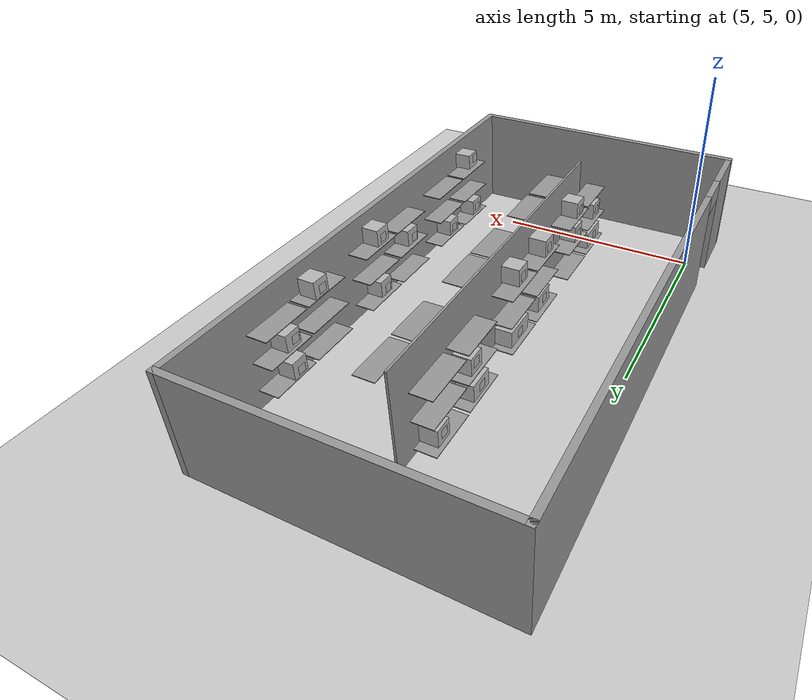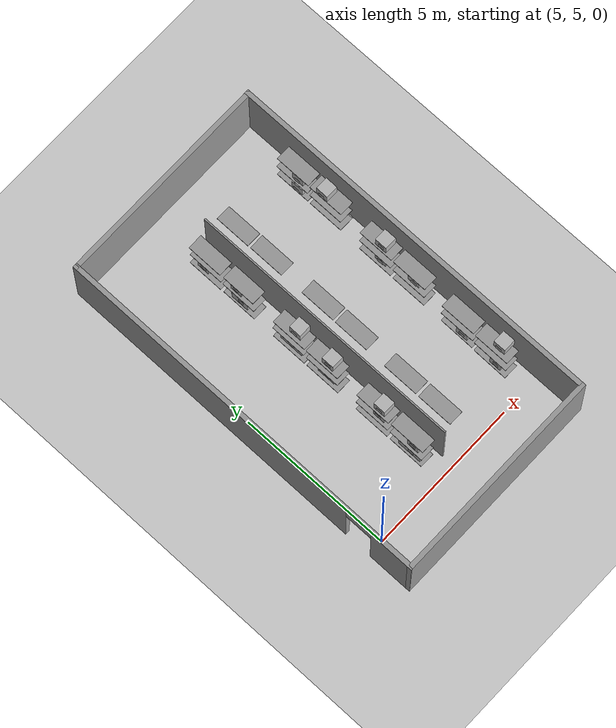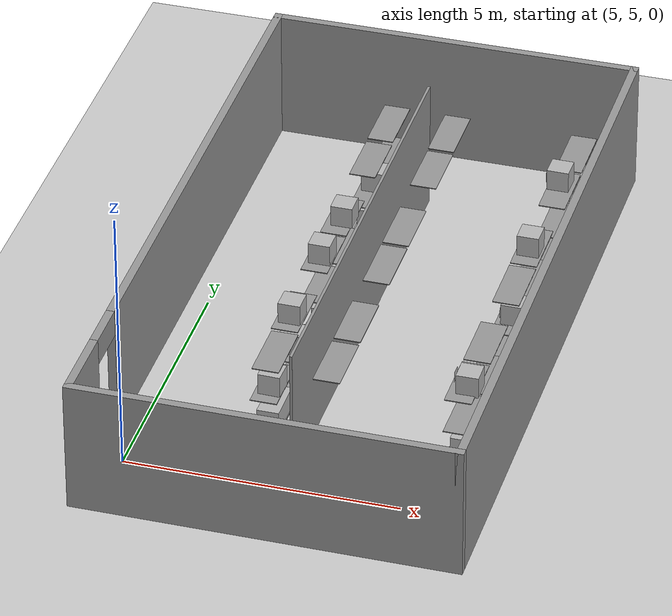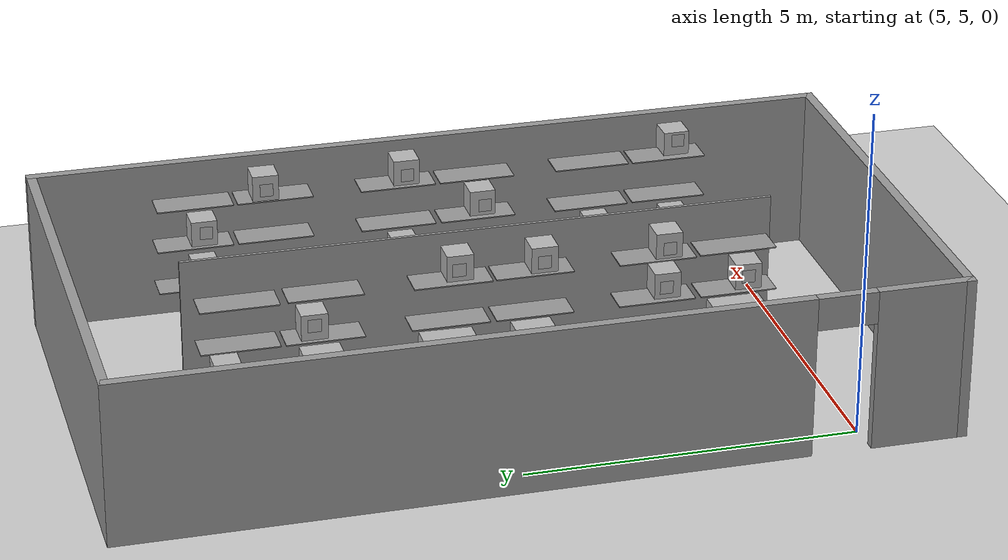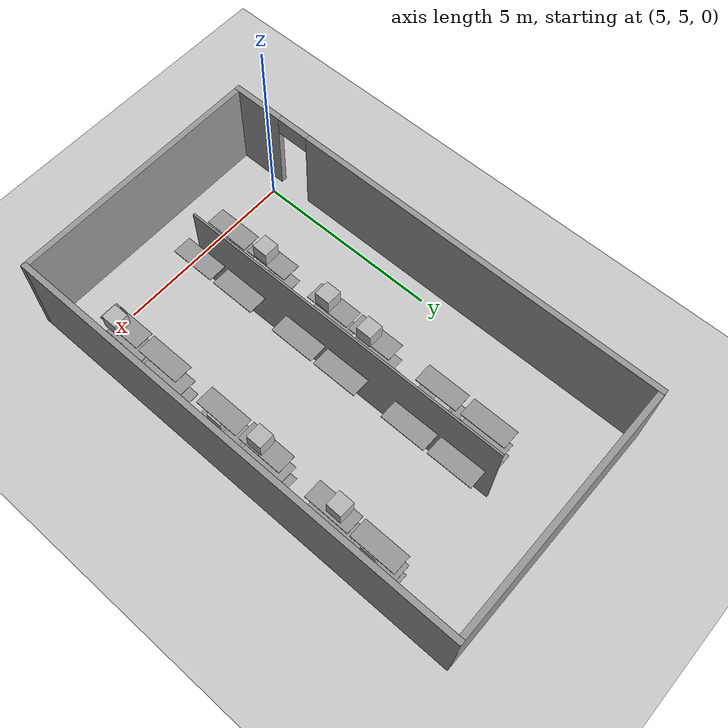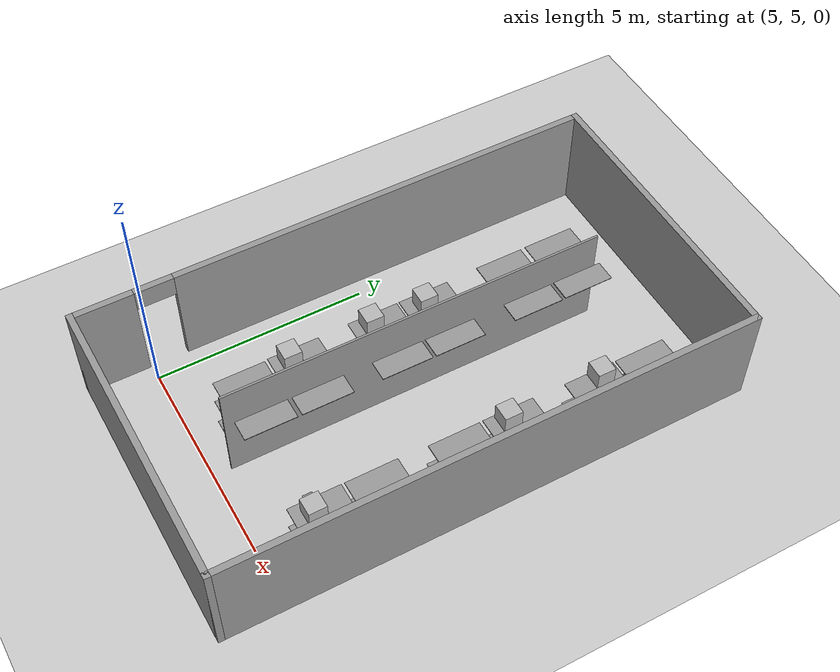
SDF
<sdf version="1.6">
 <world name="default">
  <plugin name="ros_interface_plugin" filename="librotors_gazebo_ros_interface_plugin.so"/>
  <light name="sun" type="directional">
   <pose>10 10 10 0 -0 0</pose>
   <diffuse>0.8 0.8 0.8 1</diffuse>
   <specular>0.2 0.2 0.2 1</specular>
   <attenuation>
    <range>1000</range>
    <constant>0.9</constant>
    <linear>0.01</linear>
    <quadratic>0.001</quadratic>
   </attenuation>
   <direction>-0.5 0.1 -0.9</direction>
  </light>
  <model name="ground_plane">
   <static>1</static>
   <link name="link">
    <collision name="collision">
     <geometry><plane><normal>0 0 1</normal><size>300 300</size></plane></geometry>
     <surface>
      <contact><collide_bitmask>65535</collide_bitmask></contact>
      <friction><ode><mu>100</mu><mu2>50</mu2></ode></friction>
     </surface>
    </collision>
    <visual name="visual">
     <geometry><plane><normal>0 0 1</normal><size>100 100</size></plane></geometry>
     <material>
      <script><uri>file://media/materials/scripts/gazebo.material</uri><name>Gazebo/Grey</name></script>
     </material>
    </visual>
   </link>
  </model>
  <gravity>0 0 -9.8</gravity>
  <magnetic_field>6e-06 2.3e-05 -4.2e-05</magnetic_field>
  <atmosphere type="adiabatic"/>
  <physics name="default_physics" default="0" type="ode">
   <max_step_size>0.001</max_step_size>
   <real_time_factor>1</real_time_factor>
   <real_time_update_rate>1000</real_time_update_rate>
  </physics>
  <scene><ambient>0.4 0.4 0.4 1</ambient><background>0.7 0.7 0.7 1</background><shadows>1</shadows></scene>
  <spherical_coordinates>
   <surface_model>EARTH_WGS84</surface_model>
   <latitude_deg>0</latitude_deg>
   <longitude_deg>0</longitude_deg>
   <elevation>0</elevation>
   <heading_deg>0</heading_deg>
  </spherical_coordinates>
  <audio><device>default</device></audio>
  <model name="Plano">
   <link name="link">
    <gravity>0</gravity>
    <pose>-0.103478 0.986463 0.8108 0 -0 0</pose>
    <inertial>
     <mass>1e-06</mass>
     <inertia><ixx>0.00058</ixx><ixy>0</ixy><ixz>0</ixz><iyy>0.00058</iyy><iyz>0</iyz><izz>0.00019</izz></inertia>
    </inertial>
    <visual name="visual">
     <geometry><box><size>0.2 1e-06 0.2</size></box></geometry>
     <material>
      <script>
       <uri>model://Plano/materials/scripts</uri>
       <uri>model://Plano/materials/textures</uri>
       <name>Plano/Diffuse</name>
      </script>
      <shader type="pixel"/>
     </material>
     <cast_shadows>0</cast_shadows>
    </visual>
    <collision name="collision">
     <geometry><box><size>0.2 1e-06 0.2</size></box></geometry>
     <surface>
      <friction>
       <ode><mu>1</mu><mu2>1</mu2><fdir1>0 0 0</fdir1><slip1>0</slip1><slip2>0</slip2></ode>
       <torsional>
        <coefficient>1</coefficient>
        <patch_radius>0</patch_radius>
        <surface_radius>0</surface_radius>
        <use_patch_radius>1</use_patch_radius>
        <ode><slip>0</slip></ode>
       </torsional>
      </friction>
      <bounce><restitution_coefficient>0</restitution_coefficient><threshold>1e+06</threshold></bounce>
      <contact>
       <collide_without_contact>0</collide_without_contact>
       <collide_without_contact_bitmask>1</collide_without_contact_bitmask>
       <collide_bitmask>1</collide_bitmask>
       <ode>
        <soft_cfm>0</soft_cfm>
        <soft_erp>0.2</soft_erp>
        <kp>1e+13</kp>
        <kd>1</kd>
        <max_vel>0.01</max_vel>
        <min_depth>0</min_depth>
       </ode>
       <bullet>
        <split_impulse>1</split_impulse>
        <split_impulse_penetration_threshold>-0.01</split_impulse_penetration_threshold>
        <soft_cfm>0</soft_cfm>
        <soft_erp>0.2</soft_erp>
        <kp>1e+13</kp>
        <kd>1</kd>
       </bullet>
      </contact>
     </surface>
    </collision>
   </link>
   <static>0</static>
   <pose>6.24495 5.89293 0.053748 0 0 -1.57043</pose>
  </model>
  <model name="Plano2">
   <link name="link">
    <gravity>0</gravity>
    <pose>0.45527 1.12131 0.660976 0 -0 0</pose>
    <inertial>
     <mass>1e-06</mass>
     <inertia><ixx>0.00058</ixx><ixy>0</ixy><ixz>0</ixz><iyy>0.00058</iyy><iyz>0</iyz><izz>0.00019</izz></inertia>
    </inertial>
    <visual name="visual">
     <geometry><box><size>0.2 1e-06 0.2</size></box></geometry>
     <material>
      <script>
       <uri>model://Plano2/materials/scripts</uri>
       <uri>model://Plano2/materials/textures</uri>
       <name>Plano2/Diffuse</name>
      </script>
      <shader type="pixel"/>
     </material>
     <cast_shadows>0</cast_shadows>
    </visual>
    <collision name="collision">
     <geometry><box><size>0.2 1e-06 0.2</size></box></geometry>
     <surface>
      <friction>
       <ode><mu>1</mu><mu2>1</mu2><fdir1>0 0 0</fdir1><slip1>0</slip1><slip2>0</slip2></ode>
       <torsional>
        <coefficient>1</coefficient>
        <patch_radius>0</patch_radius>
        <surface_radius>0</surface_radius>
        <use_patch_radius>1</use_patch_radius>
        <ode><slip>0</slip></ode>
       </torsional>
      </friction>
      <bounce><restitution_coefficient>0</restitution_coefficient><threshold>1e+06</threshold></bounce>
      <contact>
       <collide_without_contact>0</collide_without_contact>
       <collide_without_contact_bitmask>1</collide_without_contact_bitmask>
       <collide_bitmask>1</collide_bitmask>
       <ode>
        <soft_cfm>0</soft_cfm>
        <soft_erp>0.2</soft_erp>
        <kp>1e+13</kp>
        <kd>1</kd>
        <max_vel>0.01</max_vel>
        <min_depth>0</min_depth>
       </ode>
       <bullet>
        <split_impulse>1</split_impulse>
        <split_impulse_penetration_threshold>-0.01</split_impulse_penetration_threshold>
        <soft_cfm>0</soft_cfm>
        <soft_erp>0.2</soft_erp>
        <kp>1e+13</kp>
        <kd>1</kd>
       </bullet>
      </contact>
     </surface>
    </collision>
   </link>
   <static>0</static>
   <pose>6.11634 6.41923 0.907634 0 0 -1.5813</pose>
  </model>
  <model name="Plano3">
   <link name="link">
    <gravity>0</gravity>
    <pose>-0.321438 0.622252 1.59842 0 -0 0</pose>
    <inertial>
     <mass>1e-06</mass>
     <inertia><ixx>0.00058</ixx><ixy>0</ixy><ixz>0</ixz><iyy>0.00058</iyy><iyz>0</iyz><izz>0.00019</izz></inertia>
    </inertial>
    <visual name="visual">
     <geometry><box><size>0.2 1e-06 0.2</size></box></geometry>
     <material>
      <script>
       <uri>model://Plano3/materials/scripts</uri>
       <uri>model://Plano3/materials/textures</uri>
       <name>Plano3/Diffuse</name>
      </script>
      <shader type="pixel"/>
     </material>
     <cast_shadows>0</cast_shadows>
    </visual>
    <collision name="collision">
     <geometry><box><size>0.2 1e-06 0.2</size></box></geometry>
     <surface>
      <friction>
       <ode><mu>1</mu><mu2>1</mu2><fdir1>0 0 0</fdir1><slip1>0</slip1><slip2>0</slip2></ode>
       <torsional>
        <coefficient>1</coefficient>
        <patch_radius>0</patch_radius>
        <surface_radius>0</surface_radius>
        <use_patch_radius>1</use_patch_radius>
        <ode><slip>0</slip></ode>
       </torsional>
      </friction>
      <bounce><restitution_coefficient>0</restitution_coefficient><threshold>1e+06</threshold></bounce>
      <contact>
       <collide_without_contact>0</collide_without_contact>
       <collide_without_contact_bitmask>1</collide_without_contact_bitmask>
       <collide_bitmask>1</collide_bitmask>
       <ode>
        <soft_cfm>0</soft_cfm>
        <soft_erp>0.2</soft_erp>
        <kp>1e+13</kp>
        <kd>1</kd>
        <max_vel>0.01</max_vel>
        <min_depth>0</min_depth>
       </ode>
       <bullet>
        <split_impulse>1</split_impulse>
        <split_impulse_penetration_threshold>-0.01</split_impulse_penetration_threshold>
        <soft_cfm>0</soft_cfm>
        <soft_erp>0.2</soft_erp>
        <kp>1e+13</kp>
        <kd>1</kd>
       </bullet>
      </contact>
     </surface>
    </collision>
   </link>
   <static>0</static>
   <pose>6.60144 6.90216 -0.05097 0 0 -1.57531</pose>
  </model>
  <model name="Plano4">
   <link name="link">
    <gravity>0</gravity>
    <pose>0.342529 1.36427 1.91258 0 -0 0.032722</pose>
    <inertial>
     <mass>1e-06</mass>
     <inertia><ixx>0.00058</ixx><ixy>0</ixy><ixz>0</ixz><iyy>0.00058</iyy><iyz>0</iyz><izz>0.00019</izz></inertia>
    </inertial>
    <visual name="visual">
     <geometry><box><size>0.2 1e-06 0.2</size></box></geometry>
     <material>
      <script>
       <uri>model://Plano4/materials/scripts</uri>
       <uri>model://Plano4/materials/textures</uri>
       <name>Plano4/Diffuse</name>
      </script>
      <shader type="pixel"/>
     </material>
     <cast_shadows>0</cast_shadows>
    </visual>
    <collision name="collision">
     <geometry><box><size>0.2 1e-06 0.2</size></box></geometry>
     <surface>
      <friction>
       <ode><mu>1</mu><mu2>1</mu2><fdir1>0 0 0</fdir1><slip1>0</slip1><slip2>0</slip2></ode>
       <torsional>
        <coefficient>1</coefficient>
        <patch_radius>0</patch_radius>
        <surface_radius>0</surface_radius>
        <use_patch_radius>1</use_patch_radius>
        <ode><slip>0</slip></ode>
       </torsional>
      </friction>
      <bounce><restitution_coefficient>0</restitution_coefficient><threshold>1e+06</threshold></bounce>
      <contact>
       <collide_without_contact>0</collide_without_contact>
       <collide_without_contact_bitmask>1</collide_without_contact_bitmask>
       <collide_bitmask>1</collide_bitmask>
       <ode>
        <soft_cfm>0</soft_cfm>
        <soft_erp>0.2</soft_erp>
        <kp>1e+13</kp>
        <kd>1</kd>
        <max_vel>0.01</max_vel>
        <min_depth>0</min_depth>
       </ode>
       <bullet>
        <split_impulse>1</split_impulse>
        <split_impulse_penetration_threshold>-0.01</split_impulse_penetration_threshold>
        <soft_cfm>0</soft_cfm>
        <soft_erp>0.2</soft_erp>
        <kp>1e+13</kp>
        <kd>1</kd>
       </bullet>
      </contact>
     </surface>
    </collision>
   </link>
   <static>0</static>
   <pose>5.86012 7.53798 0.26346 0 0 -1.5802</pose>
  </model>
  <model name="Plano9">
   <link name="link">
    <gravity>0</gravity>
    <pose>0.117106 1.00481 0.58462 0 -0 0</pose>
    <inertial>
     <mass>1e-06</mass>
     <inertia><ixx>0.00058</ixx><ixy>0</ixy><ixz>0</ixz><iyy>0.00058</iyy><iyz>0</iyz><izz>0.00019</izz></inertia>
    </inertial>
    <visual name="visual">
     <geometry><box><size>0.2 1e-06 0.2</size></box></geometry>
     <material>
      <script>
       <uri>model://Plano9/materials/scripts</uri>
       <uri>model://Plano9/materials/textures</uri>
       <name>Plano9/Diffuse</name>
      </script>
      <shader type="pixel"/>
     </material>
     <cast_shadows>0</cast_shadows>
    </visual>
    <collision name="collision">
     <geometry><box><size>0.2 1e-06 0.2</size></box></geometry>
     <surface>
      <friction>
       <ode><mu>1</mu><mu2>1</mu2><fdir1>0 0 0</fdir1><slip1>0</slip1><slip2>0</slip2></ode>
       <torsional>
        <coefficient>1</coefficient>
        <patch_radius>0</patch_radius>
        <surface_radius>0</surface_radius>
        <use_patch_radius>1</use_patch_radius>
        <ode><slip>0</slip></ode>
       </torsional>
      </friction>
      <bounce><restitution_coefficient>0</restitution_coefficient><threshold>1e+06</threshold></bounce>
      <contact>
       <collide_without_contact>0</collide_without_contact>
       <collide_without_contact_bitmask>1</collide_without_contact_bitmask>
       <collide_bitmask>1</collide_bitmask>
       <ode>
        <soft_cfm>0</soft_cfm>
        <soft_erp>0.2</soft_erp>
        <kp>1e+13</kp>
        <kd>1</kd>
        <max_vel>0.01</max_vel>
        <min_depth>0</min_depth>
       </ode>
       <bullet>
        <split_impulse>1</split_impulse>
        <split_impulse_penetration_threshold>-0.01</split_impulse_penetration_threshold>
        <soft_cfm>0</soft_cfm>
        <soft_erp>0.2</soft_erp>
        <kp>1e+13</kp>
        <kd>1</kd>
       </bullet>
      </contact>
     </surface>
    </collision>
   </link>
   <static>0</static>
   <pose>6.2464 10.5924 0.261153 0 0 -1.57778</pose>
  </model>
  <model name="Plano10">
   <link name="link">
    <gravity>0</gravity>
    <pose>1.70124 1.53194 0.640341 0 -0 0</pose>
    <inertial>
     <mass>1e-06</mass>
     <inertia><ixx>0.00058</ixx><ixy>0</ixy><ixz>0</ixz><iyy>0.00058</iyy><iyz>0</iyz><izz>0.00019</izz></inertia>
    </inertial>
    <visual name="visual">
     <geometry><box><size>0.2 1e-06 0.2</size></box></geometry>
     <material>
      <script>
       <uri>model://Plano10/materials/scripts</uri>
       <uri>model://Plano10/materials/textures</uri>
       <name>Plano10/Diffuse</name>
      </script>
      <shader type="pixel"/>
     </material>
     <cast_shadows>0</cast_shadows>
    </visual>
    <collision name="collision">
     <geometry><box><size>0.2 1e-06 0.2</size></box></geometry>
     <surface>
      <friction>
       <ode><mu>1</mu><mu2>1</mu2><fdir1>0 0 0</fdir1><slip1>0</slip1><slip2>0</slip2></ode>
       <torsional>
        <coefficient>1</coefficient>
        <patch_radius>0</patch_radius>
        <surface_radius>0</surface_radius>
        <use_patch_radius>1</use_patch_radius>
        <ode><slip>0</slip></ode>
       </torsional>
      </friction>
      <bounce><restitution_coefficient>0</restitution_coefficient><threshold>1e+06</threshold></bounce>
      <contact>
       <collide_without_contact>0</collide_without_contact>
       <collide_without_contact_bitmask>1</collide_without_contact_bitmask>
       <collide_bitmask>1</collide_bitmask>
       <ode>
        <soft_cfm>0</soft_cfm>
        <soft_erp>0.2</soft_erp>
        <kp>1e+13</kp>
        <kd>1</kd>
        <max_vel>0.01</max_vel>
        <min_depth>0</min_depth>
       </ode>
       <bullet>
        <split_impulse>1</split_impulse>
        <split_impulse_penetration_threshold>-0.01</split_impulse_penetration_threshold>
        <soft_cfm>0</soft_cfm>
        <soft_erp>0.2</soft_erp>
        <kp>1e+13</kp>
        <kd>1</kd>
       </bullet>
      </contact>
     </surface>
    </collision>
   </link>
   <static>0</static>
   <pose>5.69431 10.7913 1.54976 0 0 -1.57552</pose>
  </model>
  <model name="Plano8">
   <link name="link">
    <gravity>0</gravity>
    <pose>-0.330727 1.61593 0.643893 0 -0 0</pose>
    <inertial>
     <mass>1e-06</mass>
     <inertia><ixx>0.00058</ixx><ixy>0</ixy><ixz>0</ixz><iyy>0.00058</iyy><iyz>0</iyz><izz>0.00019</izz></inertia>
    </inertial>
    <visual name="visual">
     <geometry><box><size>0.2 1e-06 0.2</size></box></geometry>
     <material>
      <script>
       <uri>model://Plano8/materials/scripts</uri>
       <uri>model://Plano8/materials/textures</uri>
       <name>Plano8/Diffuse</name>
      </script>
      <shader type="pixel"/>
     </material>
     <cast_shadows>0</cast_shadows>
    </visual>
    <collision name="collision">
     <geometry><box><size>0.2 1e-06 0.2</size></box></geometry>
     <surface>
      <friction>
       <ode><mu>1</mu><mu2>1</mu2><fdir1>0 0 0</fdir1><slip1>0</slip1><slip2>0</slip2></ode>
       <torsional>
        <coefficient>1</coefficient>
        <patch_radius>0</patch_radius>
        <surface_radius>0</surface_radius>
        <use_patch_radius>1</use_patch_radius>
        <ode><slip>0</slip></ode>
       </torsional>
      </friction>
      <bounce><restitution_coefficient>0</restitution_coefficient><threshold>1e+06</threshold></bounce>
      <contact>
       <collide_without_contact>0</collide_without_contact>
       <collide_without_contact_bitmask>1</collide_without_contact_bitmask>
       <collide_bitmask>1</collide_bitmask>
       <ode>
        <soft_cfm>0</soft_cfm>
        <soft_erp>0.2</soft_erp>
        <kp>1e+13</kp>
        <kd>1</kd>
        <max_vel>0.01</max_vel>
        <min_depth>0</min_depth>
       </ode>
       <bullet>
        <split_impulse>1</split_impulse>
        <split_impulse_penetration_threshold>-0.01</split_impulse_penetration_threshold>
        <soft_cfm>0</soft_cfm>
        <soft_erp>0.2</soft_erp>
        <kp>1e+13</kp>
        <kd>1</kd>
       </bullet>
      </contact>
     </surface>
    </collision>
   </link>
   <static>0</static>
   <pose>5.63572 10.0239 1.55665 0 0 -1.57219</pose>
  </model>
  <model name="Plano6">
   <link name="link">
    <gravity>0</gravity>
    <pose>0 -0.005358 -0.029165 0 -0 0</pose>
    <inertial>
     <mass>1e-06</mass>
     <inertia><ixx>0.00058</ixx><ixy>0</ixy><ixz>0</ixz><iyy>0.00058</iyy><iyz>0</iyz><izz>0.00019</izz></inertia>
    </inertial>
    <visual name="visual">
     <geometry><box><size>0.2 1e-06 0.2</size></box></geometry>
     <material>
      <script>
       <uri>model://Plano6/materials/scripts</uri>
       <uri>model://Plano6/materials/textures</uri>
       <name>Plano6/Diffuse</name>
      </script>
      <shader type="pixel"/>
     </material>
     <cast_shadows>0</cast_shadows>
    </visual>
    <collision name="collision">
     <geometry><box><size>0.2 1e-06 0.2</size></box></geometry>
     <surface>
      <friction>
       <ode><mu>1</mu><mu2>1</mu2><fdir1>0 0 0</fdir1><slip1>0</slip1><slip2>0</slip2></ode>
       <torsional>
        <coefficient>1</coefficient>
        <patch_radius>0</patch_radius>
        <surface_radius>0</surface_radius>
        <use_patch_radius>1</use_patch_radius>
        <ode><slip>0</slip></ode>
       </torsional>
      </friction>
      <bounce><restitution_coefficient>0</restitution_coefficient><threshold>1e+06</threshold></bounce>
      <contact>
       <collide_without_contact>0</collide_without_contact>
       <collide_without_contact_bitmask>1</collide_without_contact_bitmask>
       <collide_bitmask>1</collide_bitmask>
       <ode>
        <soft_cfm>0</soft_cfm>
        <soft_erp>0.2</soft_erp>
        <kp>1e+13</kp>
        <kd>1</kd>
        <max_vel>0.01</max_vel>
        <min_depth>0</min_depth>
       </ode>
       <bullet>
        <split_impulse>1</split_impulse>
        <split_impulse_penetration_threshold>-0.01</split_impulse_penetration_threshold>
        <soft_cfm>0</soft_cfm>
        <soft_erp>0.2</soft_erp>
        <kp>1e+13</kp>
        <kd>1</kd>
       </bullet>
      </contact>
     </surface>
    </collision>
   </link>
   <static>0</static>
   <pose>7.20489 12.3294 0.90104 0 0 -1.57278</pose>
  </model>
  <model name="Plano15">
   <link name="link">
    <gravity>0</gravity>
    <pose>0.092941 -0.00902 1.95167 0 -0 0</pose>
    <inertial>
     <mass>1e-06</mass>
     <inertia><ixx>0.00058</ixx><ixy>0</ixy><ixz>0</ixz><iyy>0.00058</iyy><iyz>0</iyz><izz>0.00019</izz></inertia>
    </inertial>
    <visual name="visual">
     <geometry><box><size>0.2 1e-06 0.2</size></box></geometry>
     <material>
      <script>
       <uri>model://Plano15/materials/scripts</uri>
       <uri>model://Plano15/materials/textures</uri>
       <name>Plano15/Diffuse</name>
      </script>
      <shader type="pixel"/>
     </material>
     <cast_shadows>0</cast_shadows>
    </visual>
    <collision name="collision">
     <geometry><box><size>0.2 1e-06 0.2</size></box></geometry>
     <surface>
      <friction>
       <ode><mu>1</mu><mu2>1</mu2><fdir1>0 0 0</fdir1><slip1>0</slip1><slip2>0</slip2></ode>
       <torsional>
        <coefficient>1</coefficient>
        <patch_radius>0</patch_radius>
        <surface_radius>0</surface_radius>
        <use_patch_radius>1</use_patch_radius>
        <ode><slip>0</slip></ode>
       </torsional>
      </friction>
      <bounce><restitution_coefficient>0</restitution_coefficient><threshold>1e+06</threshold></bounce>
      <contact>
       <collide_without_contact>0</collide_without_contact>
       <collide_without_contact_bitmask>1</collide_without_contact_bitmask>
       <collide_bitmask>1</collide_bitmask>
       <ode>
        <soft_cfm>0</soft_cfm>
        <soft_erp>0.2</soft_erp>
        <kp>1e+13</kp>
        <kd>1</kd>
        <max_vel>0.01</max_vel>
        <min_depth>0</min_depth>
       </ode>
       <bullet>
        <split_impulse>1</split_impulse>
        <split_impulse_penetration_threshold>-0.01</split_impulse_penetration_threshold>
        <soft_cfm>0</soft_cfm>
        <soft_erp>0.2</soft_erp>
        <kp>1e+13</kp>
        <kd>1</kd>
       </bullet>
      </contact>
     </surface>
    </collision>
   </link>
   <static>0</static>
   <pose>10.6606 12.5838 0.25794 0 0 -1.60068</pose>
  </model>
  <model name="Plano17">
   <link name="link">
    <gravity>0</gravity>
    <pose>0.529394 0.033885 0.692928 -0 0.041367 0.025601</pose>
    <inertial>
     <mass>1e-06</mass>
     <inertia><ixx>0.00058</ixx><ixy>0</ixy><ixz>0</ixz><iyy>0.00058</iyy><iyz>0</iyz><izz>0.00019</izz></inertia>
    </inertial>
    <visual name="visual">
     <geometry><box><size>0.2 1e-06 0.2</size></box></geometry>
     <material>
      <script>
       <uri>model://Plano17/materials/scripts</uri>
       <uri>model://Plano17/materials/textures</uri>
       <name>Plano17/Diffuse</name>
      </script>
      <shader type="pixel"/>
     </material>
     <cast_shadows>0</cast_shadows>
    </visual>
    <collision name="collision">
     <geometry><box><size>0.2 1e-06 0.2</size></box></geometry>
     <surface>
      <friction>
       <ode><mu>1</mu><mu2>1</mu2><fdir1>0 0 0</fdir1><slip1>0</slip1><slip2>0</slip2></ode>
       <torsional>
        <coefficient>1</coefficient>
        <patch_radius>0</patch_radius>
        <surface_radius>0</surface_radius>
        <use_patch_radius>1</use_patch_radius>
        <ode><slip>0</slip></ode>
       </torsional>
      </friction>
      <bounce><restitution_coefficient>0</restitution_coefficient><threshold>1e+06</threshold></bounce>
      <contact>
       <collide_without_contact>0</collide_without_contact>
       <collide_without_contact_bitmask>1</collide_without_contact_bitmask>
       <collide_bitmask>1</collide_bitmask>
       <ode>
        <soft_cfm>0</soft_cfm>
        <soft_erp>0.2</soft_erp>
        <kp>1e+13</kp>
        <kd>1</kd>
        <max_vel>0.01</max_vel>
        <min_depth>0</min_depth>
       </ode>
       <bullet>
        <split_impulse>1</split_impulse>
        <split_impulse_penetration_threshold>-0.01</split_impulse_penetration_threshold>
        <soft_cfm>0</soft_cfm>
        <soft_erp>0.2</soft_erp>
        <kp>1e+13</kp>
        <kd>1</kd>
       </bullet>
      </contact>
     </surface>
    </collision>
   </link>
   <static>0</static>
   <pose>10.6508 13.9613 0.903512 0 0 -1.5876</pose>
  </model>
  <model name="Plano14">
   <link name="link">
    <gravity>0</gravity>
    <pose>-0.817096 -0.102693 -0.058439 0.003356 0.001825 0.044055</pose>
    <inertial>
     <mass>1e-06</mass>
     <inertia><ixx>0.00058</ixx><ixy>0</ixy><ixz>0</ixz><iyy>0.00058</iyy><iyz>0</iyz><izz>0.00019</izz></inertia>
    </inertial>
    <visual name="visual">
     <geometry><box><size>0.2 1e-06 0.2</size></box></geometry>
     <material>
      <script>
       <uri>model://Plano14/materials/scripts</uri>
       <uri>model://Plano14/materials/textures</uri>
       <name>Plano14/Diffuse</name>
      </script>
      <shader type="pixel"/>
     </material>
     <cast_shadows>0</cast_shadows>
    </visual>
    <collision name="collision">
     <geometry><box><size>0.2 1e-06 0.2</size></box></geometry>
     <surface>
      <friction>
       <ode><mu>1</mu><mu2>1</mu2><fdir1>0 0 0</fdir1><slip1>0</slip1><slip2>0</slip2></ode>
       <torsional>
        <coefficient>1</coefficient>
        <patch_radius>0</patch_radius>
        <surface_radius>0</surface_radius>
        <use_patch_radius>1</use_patch_radius>
        <ode><slip>0</slip></ode>
       </torsional>
      </friction>
      <bounce><restitution_coefficient>0</restitution_coefficient><threshold>1e+06</threshold></bounce>
      <contact>
       <collide_without_contact>0</collide_without_contact>
       <collide_without_contact_bitmask>1</collide_without_contact_bitmask>
       <collide_bitmask>1</collide_bitmask>
       <ode>
        <soft_cfm>0</soft_cfm>
        <soft_erp>0.2</soft_erp>
        <kp>1e+13</kp>
        <kd>1</kd>
        <max_vel>0.01</max_vel>
        <min_depth>0</min_depth>
       </ode>
       <bullet>
        <split_impulse>1</split_impulse>
        <split_impulse_penetration_threshold>-0.01</split_impulse_penetration_threshold>
        <soft_cfm>0</soft_cfm>
        <soft_erp>0.2</soft_erp>
        <kp>1e+13</kp>
        <kd>1</kd>
       </bullet>
      </contact>
     </surface>
    </collision>
   </link>
   <static>0</static>
   <pose>10.7078 12.6284 0.90675 0 0 -1.62851</pose>
  </model>
  <model name="Plano12">
   <link name="link">
    <gravity>0</gravity>
    <pose>-0.824351 -0.041274 1.91889 0 -0 0.02962</pose>
    <inertial>
     <mass>1e-06</mass>
     <inertia><ixx>0.00058</ixx><ixy>0</ixy><ixz>0</ixz><iyy>0.00058</iyy><iyz>0</iyz><izz>0.00019</izz></inertia>
    </inertial>
    <visual name="visual">
     <geometry><box><size>0.2 1e-06 0.2</size></box></geometry>
     <material>
      <script>
       <uri>model://Plano12/materials/scripts</uri>
       <uri>model://Plano12/materials/textures</uri>
       <name>Plano12/Diffuse</name>
      </script>
      <shader type="pixel"/>
     </material>
     <cast_shadows>0</cast_shadows>
    </visual>
    <collision name="collision">
     <geometry><box><size>0.2 1e-06 0.2</size></box></geometry>
     <surface>
      <friction>
       <ode><mu>1</mu><mu2>1</mu2><fdir1>0 0 0</fdir1><slip1>0</slip1><slip2>0</slip2></ode>
       <torsional>
        <coefficient>1</coefficient>
        <patch_radius>0</patch_radius>
        <surface_radius>0</surface_radius>
        <use_patch_radius>1</use_patch_radius>
        <ode><slip>0</slip></ode>
       </torsional>
      </friction>
      <bounce><restitution_coefficient>0</restitution_coefficient><threshold>1e+06</threshold></bounce>
      <contact>
       <collide_without_contact>0</collide_without_contact>
       <collide_without_contact_bitmask>1</collide_without_contact_bitmask>
       <collide_bitmask>1</collide_bitmask>
       <ode>
        <soft_cfm>0</soft_cfm>
        <soft_erp>0.2</soft_erp>
        <kp>1e+13</kp>
        <kd>1</kd>
        <max_vel>0.01</max_vel>
        <min_depth>0</min_depth>
       </ode>
       <bullet>
        <split_impulse>1</split_impulse>
        <split_impulse_penetration_threshold>-0.01</split_impulse_penetration_threshold>
        <soft_cfm>0</soft_cfm>
        <soft_erp>0.2</soft_erp>
        <kp>1e+13</kp>
        <kd>1</kd>
       </bullet>
      </contact>
     </surface>
    </collision>
   </link>
   <static>0</static>
   <pose>10.7037 9.47205 0.27256 0 0 -1.59709</pose>
  </model>
  <model name="Plano29">
   <link name="link">
    <gravity>0</gravity>
    <pose>1.04341 -0.05608 -0.017058 0 -0 0</pose>
    <inertial>
     <mass>1e-06</mass>
     <inertia><ixx>0.00058</ixx><ixy>0</ixy><ixz>0</ixz><iyy>0.00058</iyy><iyz>0</iyz><izz>0.00019</izz></inertia>
    </inertial>
    <visual name="visual">
     <geometry><box><size>0.2 1e-06 0.2</size></box></geometry>
     <material>
      <script>
       <uri>model://Plano29/materials/scripts</uri>
       <uri>model://Plano29/materials/textures</uri>
       <name>Plano29/Diffuse</name>
      </script>
      <shader type="pixel"/>
     </material>
     <cast_shadows>0</cast_shadows>
    </visual>
    <collision name="collision">
     <geometry><box><size>0.2 1e-06 0.2</size></box></geometry>
     <surface>
      <friction>
       <ode><mu>1</mu><mu2>1</mu2><fdir1>0 0 0</fdir1><slip1>0</slip1><slip2>0</slip2></ode>
       <torsional>
        <coefficient>1</coefficient>
        <patch_radius>0</patch_radius>
        <surface_radius>0</surface_radius>
        <use_patch_radius>1</use_patch_radius>
        <ode><slip>0</slip></ode>
       </torsional>
      </friction>
      <bounce><restitution_coefficient>0</restitution_coefficient><threshold>1e+06</threshold></bounce>
      <contact>
       <collide_without_contact>0</collide_without_contact>
       <collide_without_contact_bitmask>1</collide_without_contact_bitmask>
       <collide_bitmask>1</collide_bitmask>
       <ode>
        <soft_cfm>0</soft_cfm>
        <soft_erp>0.2</soft_erp>
        <kp>1e+13</kp>
        <kd>1</kd>
        <max_vel>0.01</max_vel>
        <min_depth>0</min_depth>
       </ode>
       <bullet>
        <split_impulse>1</split_impulse>
        <split_impulse_penetration_threshold>-0.01</split_impulse_penetration_threshold>
        <soft_cfm>0</soft_cfm>
        <soft_erp>0.2</soft_erp>
        <kp>1e+13</kp>
        <kd>1</kd>
       </bullet>
      </contact>
     </surface>
    </collision>
   </link>
   <static>0</static>
   <pose>10.7522 10.1107 1.5598 0 0 -1.57894</pose>
  </model>
  <model name="Plano27">
   <link name="link">
    <gravity>0</gravity>
    <pose>0.469171 -0.023188 -0.057385 0 -0 0.032924</pose>
    <inertial>
     <mass>1e-06</mass>
     <inertia><ixx>0.00058</ixx><ixy>0</ixy><ixz>0</ixz><iyy>0.00058</iyy><iyz>0</iyz><izz>0.00019</izz></inertia>
    </inertial>
    <visual name="visual">
     <geometry><box><size>0.2 1e-06 0.2</size></box></geometry>
     <material>
      <script>
       <uri>model://Plano27/materials/scripts</uri>
       <uri>model://Plano27/materials/textures</uri>
       <name>Plano27/Diffuse</name>
      </script>
      <shader type="pixel"/>
     </material>
     <cast_shadows>0</cast_shadows>
    </visual>
    <collision name="collision">
     <geometry><box><size>0.2 1e-06 0.2</size></box></geometry>
     <surface>
      <friction>
       <ode><mu>1</mu><mu2>1</mu2><fdir1>0 0 0</fdir1><slip1>0</slip1><slip2>0</slip2></ode>
       <torsional>
        <coefficient>1</coefficient>
        <patch_radius>0</patch_radius>
        <surface_radius>0</surface_radius>
        <use_patch_radius>1</use_patch_radius>
        <ode><slip>0</slip></ode>
       </torsional>
      </friction>
      <bounce><restitution_coefficient>0</restitution_coefficient><threshold>1e+06</threshold></bounce>
      <contact>
       <collide_without_contact>0</collide_without_contact>
       <collide_without_contact_bitmask>1</collide_without_contact_bitmask>
       <collide_bitmask>1</collide_bitmask>
       <ode>
        <soft_cfm>0</soft_cfm>
        <soft_erp>0.2</soft_erp>
        <kp>1e+13</kp>
        <kd>1</kd>
        <max_vel>0.01</max_vel>
        <min_depth>0</min_depth>
       </ode>
       <bullet>
        <split_impulse>1</split_impulse>
        <split_impulse_penetration_threshold>-0.01</split_impulse_penetration_threshold>
        <soft_cfm>0</soft_cfm>
        <soft_erp>0.2</soft_erp>
        <kp>1e+13</kp>
        <kd>1</kd>
       </bullet>
      </contact>
     </surface>
    </collision>
   </link>
   <static>0</static>
   <pose>10.7156 10.7789 0.90002 0 0 -1.57306</pose>
  </model>
  <model name="Plano26_0">
   <link name="link">
    <gravity>0</gravity>
    <pose>-0.169184 -0.069468 -0.055235 0 -0 0.01407</pose>
    <inertial>
     <mass>1e-06</mass>
     <inertia><ixx>0.00058</ixx><ixy>0</ixy><ixz>0</ixz><iyy>0.00058</iyy><iyz>0</iyz><izz>0.00019</izz></inertia>
    </inertial>
    <visual name="visual">
     <geometry><box><size>0.2 1e-06 0.2</size></box></geometry>
     <material>
      <script>
       <uri>model://Plano26/materials/scripts</uri>
       <uri>model://Plano26/materials/textures</uri>
       <name>Plano26/Diffuse</name>
      </script>
      <shader type="pixel"/>
     </material>
     <cast_shadows>0</cast_shadows>
    </visual>
    <collision name="collision">
     <geometry><box><size>0.2 1e-06 0.2</size></box></geometry>
     <surface>
      <friction>
       <ode><mu>1</mu><mu2>1</mu2><fdir1>0 0 0</fdir1><slip1>0</slip1><slip2>0</slip2></ode>
       <torsional>
        <coefficient>1</coefficient>
        <patch_radius>0</patch_radius>
        <surface_radius>0</surface_radius>
        <use_patch_radius>1</use_patch_radius>
        <ode><slip>0</slip></ode>
       </torsional>
      </friction>
      <bounce><restitution_coefficient>0</restitution_coefficient><threshold>1e+06</threshold></bounce>
      <contact>
       <collide_without_contact>0</collide_without_contact>
       <collide_without_contact_bitmask>1</collide_without_contact_bitmask>
       <collide_bitmask>1</collide_bitmask>
       <ode>
        <soft_cfm>0</soft_cfm>
        <soft_erp>0.2</soft_erp>
        <kp>1e+13</kp>
        <kd>1</kd>
        <max_vel>0.01</max_vel>
        <min_depth>0</min_depth>
       </ode>
       <bullet>
        <split_impulse>1</split_impulse>
        <split_impulse_penetration_threshold>-0.01</split_impulse_penetration_threshold>
        <soft_cfm>0</soft_cfm>
        <soft_erp>0.2</soft_erp>
        <kp>1e+13</kp>
        <kd>1</kd>
       </bullet>
      </contact>
     </surface>
    </collision>
   </link>
   <static>0</static>
   <pose>10.7205 7.06672 0.90647 0 0 -1.58759</pose>
  </model>
  <model name="Plano26">
   <link name="link">
    <gravity>0</gravity>
    <pose>0.070412 -0.023465 0.724825 0 -0 0</pose>
    <inertial>
     <mass>1e-06</mass>
     <inertia><ixx>0.00058</ixx><ixy>0</ixy><ixz>0</ixz><iyy>0.00058</iyy><iyz>0</iyz><izz>0.00019</izz></inertia>
    </inertial>
    <visual name="visual">
     <geometry><box><size>0.2 1e-06 0.2</size></box></geometry>
     <material>
      <script>
       <uri>model://Plano26/materials/scripts</uri>
       <uri>model://Plano26/materials/textures</uri>
       <name>Plano26/Diffuse</name>
      </script>
      <shader type="pixel"/>
     </material>
     <cast_shadows>0</cast_shadows>
    </visual>
    <collision name="collision">
     <geometry><box><size>0.2 1e-06 0.2</size></box></geometry>
     <surface>
      <friction>
       <ode><mu>1</mu><mu2>1</mu2><fdir1>0 0 0</fdir1><slip1>0</slip1><slip2>0</slip2></ode>
       <torsional>
        <coefficient>1</coefficient>
        <patch_radius>0</patch_radius>
        <surface_radius>0</surface_radius>
        <use_patch_radius>1</use_patch_radius>
        <ode><slip>0</slip></ode>
       </torsional>
      </friction>
      <bounce><restitution_coefficient>0</restitution_coefficient><threshold>1e+06</threshold></bounce>
      <contact>
       <collide_without_contact>0</collide_without_contact>
       <collide_without_contact_bitmask>1</collide_without_contact_bitmask>
       <collide_bitmask>1</collide_bitmask>
       <ode>
        <soft_cfm>0</soft_cfm>
        <soft_erp>0.2</soft_erp>
        <kp>1e+13</kp>
        <kd>1</kd>
        <max_vel>0.01</max_vel>
        <min_depth>0</min_depth>
       </ode>
       <bullet>
        <split_impulse>1</split_impulse>
        <split_impulse_penetration_threshold>-0.01</split_impulse_penetration_threshold>
        <soft_cfm>0</soft_cfm>
        <soft_erp>0.2</soft_erp>
        <kp>1e+13</kp>
        <kd>1</kd>
       </bullet>
      </contact>
     </surface>
    </collision>
   </link>
   <static>0</static>
   <pose>10.7123 6.04698 1.56042 0 0 -1.57945</pose>
  </model>
  <model name="Plano20">
   <link name="link">
    <gravity>0</gravity>
    <pose>0.632324 -0.065211 0.597871 0 -0 0</pose>
    <inertial>
     <mass>1e-06</mass>
     <inertia><ixx>0.00058</ixx><ixy>0</ixy><ixz>0</ixz><iyy>0.00058</iyy><iyz>0</iyz><izz>0.00019</izz></inertia>
    </inertial>
    <visual name="visual">
     <geometry><box><size>0.2 1e-06 0.2</size></box></geometry>
     <material>
      <script>
       <uri>model://Plano20/materials/scripts</uri>
       <uri>model://Plano20/materials/textures</uri>
       <name>Plano20/Diffuse</name>
      </script>
      <shader type="pixel"/>
     </material>
     <cast_shadows>0</cast_shadows>
    </visual>
    <collision name="collision">
     <geometry><box><size>0.2 1e-06 0.2</size></box></geometry>
     <surface>
      <friction>
       <ode><mu>1</mu><mu2>1</mu2><fdir1>0 0 0</fdir1><slip1>0</slip1><slip2>0</slip2></ode>
       <torsional>
        <coefficient>1</coefficient>
        <patch_radius>0</patch_radius>
        <surface_radius>0</surface_radius>
        <use_patch_radius>1</use_patch_radius>
        <ode><slip>0</slip></ode>
       </torsional>
      </friction>
      <bounce><restitution_coefficient>0</restitution_coefficient><threshold>1e+06</threshold></bounce>
      <contact>
       <collide_without_contact>0</collide_without_contact>
       <collide_without_contact_bitmask>1</collide_without_contact_bitmask>
       <collide_bitmask>1</collide_bitmask>
       <ode>
        <soft_cfm>0</soft_cfm>
        <soft_erp>0.2</soft_erp>
        <kp>1e+13</kp>
        <kd>1</kd>
        <max_vel>0.01</max_vel>
        <min_depth>0</min_depth>
       </ode>
       <bullet>
        <split_impulse>1</split_impulse>
        <split_impulse_penetration_threshold>-0.01</split_impulse_penetration_threshold>
        <soft_cfm>0</soft_cfm>
        <soft_erp>0.2</soft_erp>
        <kp>1e+13</kp>
        <kd>1</kd>
       </bullet>
      </contact>
     </surface>
    </collision>
   </link>
   <static>0</static>
   <pose>10.7236 6.60015 0.262989 0 0 -1.59313</pose>
  </model>
  <model name="Untitled_0">
   <link name="Wall_2">
    <pose>-3.33081 4.20959 0 0 0 -1.5708</pose>
    <visual name="Wall_2_Visual">
     <pose>0 0 1.25 0 -0 0</pose>
     <geometry><box><size>8.89987 0.05 2.5</size></box></geometry>
     <material>
      <script><uri>file://media/materials/scripts/gazebo.material</uri><name>Gazebo/Grey</name></script>
      <ambient>1 1 1 1</ambient>
      <shader type="pixel"/>
     </material>
     <meta><layer>0</layer></meta>
    </visual>
    <collision name="Wall_2_Collision">
     <pose>0 0 1.25 0 -0 0</pose>
     <geometry><box><size>8.89987 0.05 2.5</size></box></geometry>
     <surface>
      <friction>
       <ode><mu>1</mu><mu2>1</mu2><fdir1>0 0 0</fdir1><slip1>0</slip1><slip2>0</slip2></ode>
       <torsional>
        <coefficient>1</coefficient>
        <patch_radius>0</patch_radius>
        <surface_radius>0</surface_radius>
        <use_patch_radius>1</use_patch_radius>
        <ode><slip>0</slip></ode>
       </torsional>
      </friction>
      <bounce><restitution_coefficient>0</restitution_coefficient><threshold>1e+06</threshold></bounce>
      <contact>
       <collide_without_contact>0</collide_without_contact>
       <collide_without_contact_bitmask>1</collide_without_contact_bitmask>
       <collide_bitmask>1</collide_bitmask>
       <ode>
        <soft_cfm>0</soft_cfm>
        <soft_erp>0.2</soft_erp>
        <kp>1e+13</kp>
        <kd>1</kd>
        <max_vel>0.01</max_vel>
        <min_depth>0</min_depth>
       </ode>
       <bullet>
        <split_impulse>1</split_impulse>
        <split_impulse_penetration_threshold>-0.01</split_impulse_penetration_threshold>
        <soft_cfm>0</soft_cfm>
        <soft_erp>0.2</soft_erp>
        <kp>1e+13</kp>
        <kd>1</kd>
       </bullet>
      </contact>
     </surface>
    </collision>
   </link>
   <static>1</static>
   <pose>11.266 5.654 0 0 -0 0</pose>
  </model>
  <model name="unit_box_clone_3">
   <link name="link">
    <inertial>
     <mass>0.00922354</mass>
     <inertia>
      <ixx>0.00104733</ixx>
      <ixy>0</ixy>
      <ixz>0</ixz>
      <iyy>0.000178965</iyy>
      <iyz>0</iyz>
      <izz>0.00122588</izz>
     </inertia>
    </inertial>
    <pose>1.0387 1.15619 1.50314 -0 -0 -0</pose>
    <visual name="visual">
     <geometry><box><size>0.482252 1.16718 0.016436</size></box></geometry>
     <material>
      <script><name>Gazebo/Grey</name><uri>file://media/materials/scripts/gazebo.material</uri></script>
      <shader type="pixel"/>
     </material>
    </visual>
    <collision name="collision">
     <geometry><box><size>0.482252 1.16718 0.016436</size></box></geometry>
     <surface>
      <friction>
       <ode><mu>1</mu><mu2>1</mu2><fdir1>0 0 0</fdir1><slip1>0</slip1><slip2>0</slip2></ode>
       <torsional>
        <coefficient>1</coefficient>
        <patch_radius>0</patch_radius>
        <surface_radius>0</surface_radius>
        <use_patch_radius>1</use_patch_radius>
        <ode><slip>0</slip></ode>
       </torsional>
      </friction>
      <bounce><restitution_coefficient>0</restitution_coefficient><threshold>1e+06</threshold></bounce>
      <contact>
       <collide_without_contact>0</collide_without_contact>
       <collide_without_contact_bitmask>1</collide_without_contact_bitmask>
       <collide_bitmask>1</collide_bitmask>
       <ode>
        <soft_cfm>0</soft_cfm>
        <soft_erp>0.2</soft_erp>
        <kp>1e+13</kp>
        <kd>1</kd>
        <max_vel>0.01</max_vel>
        <min_depth>0</min_depth>
       </ode>
       <bullet>
        <split_impulse>1</split_impulse>
        <split_impulse_penetration_threshold>-0.01</split_impulse_penetration_threshold>
        <soft_cfm>0</soft_cfm>
        <soft_erp>0.2</soft_erp>
        <kp>1e+13</kp>
        <kd>1</kd>
       </bullet>
      </contact>
     </surface>
    </collision>
   </link>
   <static>1</static>
   <pose>9.87058 12.426 0.509169 0 -1e-06 -0.002445</pose>
  </model>
  <model name="unit_box_clone_4">
   <link name="link">
    <inertial>
     <mass>0.00922354</mass>
     <inertia>
      <ixx>0.00104733</ixx>
      <ixy>0</ixy>
      <ixz>0</ixz>
      <iyy>0.000178965</iyy>
      <iyz>0</iyz>
      <izz>0.00122588</izz>
     </inertia>
    </inertial>
    <pose>1.0387 1.15619 1.50314 -0 -0 -0</pose>
    <visual name="visual">
     <geometry><box><size>0.482252 1.16718 0.016436</size></box></geometry>
     <material>
      <script><name>Gazebo/Grey</name><uri>file://media/materials/scripts/gazebo.material</uri></script>
      <shader type="pixel"/>
     </material>
    </visual>
    <collision name="collision">
     <geometry><box><size>0.482252 1.16718 0.016436</size></box></geometry>
     <surface>
      <friction>
       <ode><mu>1</mu><mu2>1</mu2><fdir1>0 0 0</fdir1><slip1>0</slip1><slip2>0</slip2></ode>
       <torsional>
        <coefficient>1</coefficient>
        <patch_radius>0</patch_radius>
        <surface_radius>0</surface_radius>
        <use_patch_radius>1</use_patch_radius>
        <ode><slip>0</slip></ode>
       </torsional>
      </friction>
      <bounce><restitution_coefficient>0</restitution_coefficient><threshold>1e+06</threshold></bounce>
      <contact>
       <collide_without_contact>0</collide_without_contact>
       <collide_without_contact_bitmask>1</collide_without_contact_bitmask>
       <collide_bitmask>1</collide_bitmask>
       <ode>
        <soft_cfm>0</soft_cfm>
        <soft_erp>0.2</soft_erp>
        <kp>1e+13</kp>
        <kd>1</kd>
        <max_vel>0.01</max_vel>
        <min_depth>0</min_depth>
       </ode>
       <bullet>
        <split_impulse>1</split_impulse>
        <split_impulse_penetration_threshold>-0.01</split_impulse_penetration_threshold>
        <soft_cfm>0</soft_cfm>
        <soft_erp>0.2</soft_erp>
        <kp>1e+13</kp>
        <kd>1</kd>
       </bullet>
      </contact>
     </surface>
    </collision>
   </link>
   <static>1</static>
   <pose>7.48204 11.2062 0.509169 0 -1e-06 -0.002445</pose>
  </model>
  <model name="unit_box_clone_5">
   <link name="link">
    <inertial>
     <mass>0.00922354</mass>
     <inertia>
      <ixx>0.00104733</ixx>
      <ixy>0</ixy>
      <ixz>0</ixz>
      <iyy>0.000178965</iyy>
      <iyz>0</iyz>
      <izz>0.00122588</izz>
     </inertia>
    </inertial>
    <pose>1.0387 1.15619 1.50314 -0 -0 -0</pose>
    <visual name="visual">
     <geometry><box><size>0.482252 1.16718 0.016436</size></box></geometry>
     <material>
      <script><name>Gazebo/Grey</name><uri>file://media/materials/scripts/gazebo.material</uri></script>
      <shader type="pixel"/>
     </material>
    </visual>
    <collision name="collision">
     <geometry><box><size>0.482252 1.16718 0.016436</size></box></geometry>
     <surface>
      <friction>
       <ode><mu>1</mu><mu2>1</mu2><fdir1>0 0 0</fdir1><slip1>0</slip1><slip2>0</slip2></ode>
       <torsional>
        <coefficient>1</coefficient>
        <patch_radius>0</patch_radius>
        <surface_radius>0</surface_radius>
        <use_patch_radius>1</use_patch_radius>
        <ode><slip>0</slip></ode>
       </torsional>
      </friction>
      <bounce><restitution_coefficient>0</restitution_coefficient><threshold>1e+06</threshold></bounce>
      <contact>
       <collide_without_contact>0</collide_without_contact>
       <collide_without_contact_bitmask>1</collide_without_contact_bitmask>
       <collide_bitmask>1</collide_bitmask>
       <ode>
        <soft_cfm>0</soft_cfm>
        <soft_erp>0.2</soft_erp>
        <kp>1e+13</kp>
        <kd>1</kd>
        <max_vel>0.01</max_vel>
        <min_depth>0</min_depth>
       </ode>
       <bullet>
        <split_impulse>1</split_impulse>
        <split_impulse_penetration_threshold>-0.01</split_impulse_penetration_threshold>
        <soft_cfm>0</soft_cfm>
        <soft_erp>0.2</soft_erp>
        <kp>1e+13</kp>
        <kd>1</kd>
       </bullet>
      </contact>
     </surface>
    </collision>
   </link>
   <static>1</static>
   <pose>7.47422 12.4533 0.509169 0 -1e-06 -0.002445</pose>
  </model>
  <model name="unit_box_clone_8">
   <link name="link">
    <inertial>
     <mass>0.00922354</mass>
     <inertia>
      <ixx>0.00104733</ixx>
      <ixy>0</ixy>
      <ixz>0</ixz>
      <iyy>0.000178965</iyy>
      <iyz>0</iyz>
      <izz>0.00122588</izz>
     </inertia>
    </inertial>
    <pose>1.0387 1.15619 1.50314 -0 -0 -0</pose>
    <visual name="visual">
     <geometry><box><size>0.482252 1.16718 0.016436</size></box></geometry>
     <material>
      <script><name>Gazebo/Grey</name><uri>file://media/materials/scripts/gazebo.material</uri></script>
      <shader type="pixel"/>
     </material>
    </visual>
    <collision name="collision">
     <geometry><box><size>0.482252 1.16718 0.016436</size></box></geometry>
     <surface>
      <friction>
       <ode><mu>1</mu><mu2>1</mu2><fdir1>0 0 0</fdir1><slip1>0</slip1><slip2>0</slip2></ode>
       <torsional>
        <coefficient>1</coefficient>
        <patch_radius>0</patch_radius>
        <surface_radius>0</surface_radius>
        <use_patch_radius>1</use_patch_radius>
        <ode><slip>0</slip></ode>
       </torsional>
      </friction>
      <bounce><restitution_coefficient>0</restitution_coefficient><threshold>1e+06</threshold></bounce>
      <contact>
       <collide_without_contact>0</collide_without_contact>
       <collide_without_contact_bitmask>1</collide_without_contact_bitmask>
       <collide_bitmask>1</collide_bitmask>
       <ode>
        <soft_cfm>0</soft_cfm>
        <soft_erp>0.2</soft_erp>
        <kp>1e+13</kp>
        <kd>1</kd>
        <max_vel>0.01</max_vel>
        <min_depth>0</min_depth>
       </ode>
       <bullet>
        <split_impulse>1</split_impulse>
        <split_impulse_penetration_threshold>-0.01</split_impulse_penetration_threshold>
        <soft_cfm>0</soft_cfm>
        <soft_erp>0.2</soft_erp>
        <kp>1e+13</kp>
        <kd>1</kd>
       </bullet>
      </contact>
     </surface>
    </collision>
   </link>
   <static>1</static>
   <pose>7.48945 6.23288 0.509169 0 -1e-06 -0.002445</pose>
  </model>
  <model name="unit_box_clone_9">
   <link name="link">
    <inertial>
     <mass>0.00922354</mass>
     <inertia>
      <ixx>0.00104733</ixx>
      <ixy>0</ixy>
      <ixz>0</ixz>
      <iyy>0.000178965</iyy>
      <iyz>0</iyz>
      <izz>0.00122588</izz>
     </inertia>
    </inertial>
    <pose>1.0387 1.15619 1.50314 -0 -0 -0</pose>
    <visual name="visual">
     <geometry><box><size>0.482252 1.16718 0.016436</size></box></geometry>
     <material>
      <script><name>Gazebo/Grey</name><uri>file://media/materials/scripts/gazebo.material</uri></script>
      <shader type="pixel"/>
     </material>
    </visual>
    <collision name="collision">
     <geometry><box><size>0.482252 1.16718 0.016436</size></box></geometry>
     <surface>
      <friction>
       <ode><mu>1</mu><mu2>1</mu2><fdir1>0 0 0</fdir1><slip1>0</slip1><slip2>0</slip2></ode>
       <torsional>
        <coefficient>1</coefficient>
        <patch_radius>0</patch_radius>
        <surface_radius>0</surface_radius>
        <use_patch_radius>1</use_patch_radius>
        <ode><slip>0</slip></ode>
       </torsional>
      </friction>
      <bounce><restitution_coefficient>0</restitution_coefficient><threshold>1e+06</threshold></bounce>
      <contact>
       <collide_without_contact>0</collide_without_contact>
       <collide_without_contact_bitmask>1</collide_without_contact_bitmask>
       <collide_bitmask>1</collide_bitmask>
       <ode>
        <soft_cfm>0</soft_cfm>
        <soft_erp>0.2</soft_erp>
        <kp>1e+13</kp>
        <kd>1</kd>
        <max_vel>0.01</max_vel>
        <min_depth>0</min_depth>
       </ode>
       <bullet>
        <split_impulse>1</split_impulse>
        <split_impulse_penetration_threshold>-0.01</split_impulse_penetration_threshold>
        <soft_cfm>0</soft_cfm>
        <soft_erp>0.2</soft_erp>
        <kp>1e+13</kp>
        <kd>1</kd>
       </bullet>
      </contact>
     </surface>
    </collision>
   </link>
   <static>1</static>
   <pose>7.48456 4.97044 0.509169 0 -1e-06 -0.002445</pose>
  </model>
  <model name="unit_box_clone_10_clone_0">
   <link name="link">
    <inertial>
     <mass>0.00922354</mass>
     <inertia>
      <ixx>0.00104733</ixx>
      <ixy>0</ixy>
      <ixz>0</ixz>
      <iyy>0.000178965</iyy>
      <iyz>0</iyz>
      <izz>0.00122588</izz>
     </inertia>
    </inertial>
    <pose>2.16821 0.157655 0.848426 -0 -0 -0</pose>
    <visual name="visual">
     <geometry><box><size>0.482252 1.16718 0.016436</size></box></geometry>
     <material>
      <script><name>Gazebo/Grey</name><uri>file://media/materials/scripts/gazebo.material</uri></script>
      <shader type="pixel"/>
     </material>
    </visual>
    <collision name="collision">
     <geometry><box><size>0.482252 1.16718 0.016436</size></box></geometry>
     <surface>
      <friction>
       <ode><mu>1</mu><mu2>1</mu2><fdir1>0 0 0</fdir1><slip1>0</slip1><slip2>0</slip2></ode>
       <torsional>
        <coefficient>1</coefficient>
        <patch_radius>0</patch_radius>
        <surface_radius>0</surface_radius>
        <use_patch_radius>1</use_patch_radius>
        <ode><slip>0</slip></ode>
       </torsional>
      </friction>
      <bounce><restitution_coefficient>0</restitution_coefficient><threshold>1e+06</threshold></bounce>
      <contact>
       <collide_without_contact>0</collide_without_contact>
       <collide_without_contact_bitmask>1</collide_without_contact_bitmask>
       <collide_bitmask>1</collide_bitmask>
       <ode>
        <soft_cfm>0</soft_cfm>
        <soft_erp>0.2</soft_erp>
        <kp>1e+13</kp>
        <kd>1</kd>
        <max_vel>0.01</max_vel>
        <min_depth>0</min_depth>
       </ode>
       <bullet>
        <split_impulse>1</split_impulse>
        <split_impulse_penetration_threshold>-0.01</split_impulse_penetration_threshold>
        <soft_cfm>0</soft_cfm>
        <soft_erp>0.2</soft_erp>
        <kp>1e+13</kp>
        <kd>1</kd>
       </bullet>
      </contact>
     </surface>
    </collision>
   </link>
   <static>1</static>
   <pose>5.22878 9.08121 0.509172 0 -1e-06 -0.002445</pose>
  </model>
  <model name="unit_box_clone_10_clone_1">
   <link name="link">
    <inertial>
     <mass>0.00922354</mass>
     <inertia>
      <ixx>0.00104733</ixx>
      <ixy>0</ixy>
      <ixz>0</ixz>
      <iyy>0.000178965</iyy>
      <iyz>0</iyz>
      <izz>0.00122588</izz>
     </inertia>
    </inertial>
    <pose>2.16821 0.157655 0.848426 -0 -0 -0</pose>
    <visual name="visual">
     <geometry><box><size>0.482252 1.16718 0.016436</size></box></geometry>
     <material>
      <script><name>Gazebo/Grey</name><uri>file://media/materials/scripts/gazebo.material</uri></script>
      <shader type="pixel"/>
     </material>
    </visual>
    <collision name="collision">
     <geometry><box><size>0.482252 1.16718 0.016436</size></box></geometry>
     <surface>
      <friction>
       <ode><mu>1</mu><mu2>1</mu2><fdir1>0 0 0</fdir1><slip1>0</slip1><slip2>0</slip2></ode>
       <torsional>
        <coefficient>1</coefficient>
        <patch_radius>0</patch_radius>
        <surface_radius>0</surface_radius>
        <use_patch_radius>1</use_patch_radius>
        <ode><slip>0</slip></ode>
       </torsional>
      </friction>
      <bounce><restitution_coefficient>0</restitution_coefficient><threshold>1e+06</threshold></bounce>
      <contact>
       <collide_without_contact>0</collide_without_contact>
       <collide_without_contact_bitmask>1</collide_without_contact_bitmask>
       <collide_bitmask>1</collide_bitmask>
       <ode>
        <soft_cfm>0</soft_cfm>
        <soft_erp>0.2</soft_erp>
        <kp>1e+13</kp>
        <kd>1</kd>
        <max_vel>0.01</max_vel>
        <min_depth>0</min_depth>
       </ode>
       <bullet>
        <split_impulse>1</split_impulse>
        <split_impulse_penetration_threshold>-0.01</split_impulse_penetration_threshold>
        <soft_cfm>0</soft_cfm>
        <soft_erp>0.2</soft_erp>
        <kp>1e+13</kp>
        <kd>1</kd>
       </bullet>
      </contact>
     </surface>
    </collision>
   </link>
   <static>1</static>
   <pose>8.69361 10.2933 0.509172 0 -1e-06 -0.002445</pose>
  </model>
  <model name="unit_box_clone_10_clone_2">
   <link name="link">
    <inertial>
     <mass>0.00922354</mass>
     <inertia>
      <ixx>0.00104733</ixx>
      <ixy>0</ixy>
      <ixz>0</ixz>
      <iyy>0.000178965</iyy>
      <iyz>0</iyz>
      <izz>0.00122588</izz>
     </inertia>
    </inertial>
    <pose>2.16821 0.157655 0.848426 -0 -0 -0</pose>
    <visual name="visual">
     <geometry><box><size>0.482252 1.16718 0.016436</size></box></geometry>
     <material>
      <script><name>Gazebo/Grey</name><uri>file://media/materials/scripts/gazebo.material</uri></script>
      <shader type="pixel"/>
     </material>
    </visual>
    <collision name="collision">
     <geometry><box><size>0.482252 1.16718 0.016436</size></box></geometry>
     <surface>
      <friction>
       <ode><mu>1</mu><mu2>1</mu2><fdir1>0 0 0</fdir1><slip1>0</slip1><slip2>0</slip2></ode>
       <torsional>
        <coefficient>1</coefficient>
        <patch_radius>0</patch_radius>
        <surface_radius>0</surface_radius>
        <use_patch_radius>1</use_patch_radius>
        <ode><slip>0</slip></ode>
       </torsional>
      </friction>
      <bounce><restitution_coefficient>0</restitution_coefficient><threshold>1e+06</threshold></bounce>
      <contact>
       <collide_without_contact>0</collide_without_contact>
       <collide_without_contact_bitmask>1</collide_without_contact_bitmask>
       <collide_bitmask>1</collide_bitmask>
       <ode>
        <soft_cfm>0</soft_cfm>
        <soft_erp>0.2</soft_erp>
        <kp>1e+13</kp>
        <kd>1</kd>
        <max_vel>0.01</max_vel>
        <min_depth>0</min_depth>
       </ode>
       <bullet>
        <split_impulse>1</split_impulse>
        <split_impulse_penetration_threshold>-0.01</split_impulse_penetration_threshold>
        <soft_cfm>0</soft_cfm>
        <soft_erp>0.2</soft_erp>
        <kp>1e+13</kp>
        <kd>1</kd>
       </bullet>
      </contact>
     </surface>
    </collision>
   </link>
   <static>1</static>
   <pose>8.73071 12.2024 0.509172 0 -1e-06 -0.002445</pose>
  </model>
  <model name="CuboQR6">
   <link name="link">
    <pose>0.57577 -1.62645 -1.15271 0 -0 0.78008</pose>
    <inertial>
     <mass>0.39</mass>
     <inertia><ixx>0.00058</ixx><ixy>0</ixy><ixz>0</ixz><iyy>0.00058</iyy><iyz>0</iyz><izz>0.00019</izz></inertia>
    </inertial>
    <visual name="visual">
     <geometry><box><size>0.4 0.4 0.4</size></box></geometry>
     <material>
      <script>
       <uri>model://Caja/materials/scripts</uri>
       <uri>model://Caja/materials/textures</uri>
       <name>Caja/Diffuse</name>
      </script>
      <shader type="pixel"/>
     </material>
    </visual>
    <collision name="collision">
     <geometry><box><size>0.4 0.4 0.4</size></box></geometry>
     <surface>
      <friction>
       <ode><mu>1</mu><mu2>1</mu2><fdir1>0 0 0</fdir1><slip1>0</slip1><slip2>0</slip2></ode>
       <torsional>
        <coefficient>1</coefficient>
        <patch_radius>0</patch_radius>
        <surface_radius>0</surface_radius>
        <use_patch_radius>1</use_patch_radius>
        <ode><slip>0</slip></ode>
       </torsional>
      </friction>
      <bounce><restitution_coefficient>0</restitution_coefficient><threshold>1e+06</threshold></bounce>
      <contact>
       <collide_without_contact>0</collide_without_contact>
       <collide_without_contact_bitmask>1</collide_without_contact_bitmask>
       <collide_bitmask>1</collide_bitmask>
       <ode>
        <soft_cfm>0</soft_cfm>
        <soft_erp>0.2</soft_erp>
        <kp>1e+13</kp>
        <kd>1</kd>
        <max_vel>0.01</max_vel>
        <min_depth>0</min_depth>
       </ode>
       <bullet>
        <split_impulse>1</split_impulse>
        <split_impulse_penetration_threshold>-0.01</split_impulse_penetration_threshold>
        <soft_cfm>0</soft_cfm>
        <soft_erp>0.2</soft_erp>
        <kp>1e+13</kp>
        <kd>1</kd>
       </bullet>
      </contact>
     </surface>
    </collision>
   </link>
   <static>0</static>
   <pose>5.85203 11.7738 0.420952 -3.14159 3e-06 -0.795935</pose>
  </model>
  <model name="unit_box_clone_10_clone_6_clone">
   <link name="link">
    <inertial>
     <mass>0.00922354</mass>
     <inertia>
      <ixx>0.00104733</ixx>
      <ixy>0</ixy>
      <ixz>0</ixz>
      <iyy>0.000178965</iyy>
      <iyz>0</iyz>
      <izz>0.00122588</izz>
     </inertia>
    </inertial>
    <pose>1.30004 -1.35824 0.177157 -0 -0 -0</pose>
    <visual name="visual">
     <geometry><box><size>0.482252 1.16718 0.016436</size></box></geometry>
     <material>
      <script><name>Gazebo/Grey</name><uri>file://media/materials/scripts/gazebo.material</uri></script>
      <shader type="pixel"/>
     </material>
    </visual>
    <collision name="collision">
     <geometry><box><size>0.482252 1.16718 0.016436</size></box></geometry>
     <surface>
      <friction>
       <ode><mu>1</mu><mu2>1</mu2><fdir1>0 0 0</fdir1><slip1>0</slip1><slip2>0</slip2></ode>
       <torsional>
        <coefficient>1</coefficient>
        <patch_radius>0</patch_radius>
        <surface_radius>0</surface_radius>
        <use_patch_radius>1</use_patch_radius>
        <ode><slip>0</slip></ode>
       </torsional>
      </friction>
      <bounce><restitution_coefficient>0</restitution_coefficient><threshold>1e+06</threshold></bounce>
      <contact>
       <collide_without_contact>0</collide_without_contact>
       <collide_without_contact_bitmask>1</collide_without_contact_bitmask>
       <collide_bitmask>1</collide_bitmask>
       <ode>
        <soft_cfm>0</soft_cfm>
        <soft_erp>0.2</soft_erp>
        <kp>1e+13</kp>
        <kd>1</kd>
        <max_vel>0.01</max_vel>
        <min_depth>0</min_depth>
       </ode>
       <bullet>
        <split_impulse>1</split_impulse>
        <split_impulse_penetration_threshold>-0.01</split_impulse_penetration_threshold>
        <soft_cfm>0</soft_cfm>
        <soft_erp>0.2</soft_erp>
        <kp>1e+13</kp>
        <kd>1</kd>
       </bullet>
      </contact>
     </surface>
    </collision>
   </link>
   <static>1</static>
   <pose>6.08652 13.7018 0.509169 0 -1e-06 -0.002445</pose>
  </model>
  <model name="unit_box_clone_10_clone_6">
   <link name="link">
    <inertial>
     <mass>0.00922354</mass>
     <inertia>
      <ixx>0.00104733</ixx>
      <ixy>0</ixy>
      <ixz>0</ixz>
      <iyy>0.000178965</iyy>
      <iyz>0</iyz>
      <izz>0.00122588</izz>
     </inertia>
    </inertial>
    <pose>1.28673 -1.35824 0.193217 -0 -0 -0</pose>
    <visual name="visual">
     <geometry><box><size>0.482252 1.16718 0.016436</size></box></geometry>
     <material>
      <script><name>Gazebo/Grey</name><uri>file://media/materials/scripts/gazebo.material</uri></script>
      <shader type="pixel"/>
     </material>
    </visual>
    <collision name="collision">
     <geometry><box><size>0.482252 1.16718 0.016436</size></box></geometry>
     <surface>
      <friction>
       <ode><mu>1</mu><mu2>1</mu2><fdir1>0 0 0</fdir1><slip1>0</slip1><slip2>0</slip2></ode>
       <torsional>
        <coefficient>1</coefficient>
        <patch_radius>0</patch_radius>
        <surface_radius>0</surface_radius>
        <use_patch_radius>1</use_patch_radius>
        <ode><slip>0</slip></ode>
       </torsional>
      </friction>
      <bounce><restitution_coefficient>0</restitution_coefficient><threshold>1e+06</threshold></bounce>
      <contact>
       <collide_without_contact>0</collide_without_contact>
       <collide_without_contact_bitmask>1</collide_without_contact_bitmask>
       <collide_bitmask>1</collide_bitmask>
       <ode>
        <soft_cfm>0</soft_cfm>
        <soft_erp>0.2</soft_erp>
        <kp>1e+13</kp>
        <kd>1</kd>
        <max_vel>0.01</max_vel>
        <min_depth>0</min_depth>
       </ode>
       <bullet>
        <split_impulse>1</split_impulse>
        <split_impulse_penetration_threshold>-0.01</split_impulse_penetration_threshold>
        <soft_cfm>0</soft_cfm>
        <soft_erp>0.2</soft_erp>
        <kp>1e+13</kp>
        <kd>1</kd>
       </bullet>
      </contact>
     </surface>
    </collision>
   </link>
   <static>1</static>
   <pose>6.08613 14.9623 0.509169 0 -1e-06 -0.002445</pose>
  </model>
  <model name="unit_box_clone_10_clone">
   <link name="link">
    <inertial>
     <mass>0.00922354</mass>
     <inertia>
      <ixx>0.00104733</ixx>
      <ixy>0</ixy>
      <ixz>0</ixz>
      <iyy>0.000178965</iyy>
      <iyz>0</iyz>
      <izz>0.00122588</izz>
     </inertia>
    </inertial>
    <pose>2.16821 0.157655 0.848426 -0 -0 -0</pose>
    <visual name="visual">
     <geometry><box><size>0.482252 1.16718 0.016436</size></box></geometry>
     <material>
      <script><name>Gazebo/Grey</name><uri>file://media/materials/scripts/gazebo.material</uri></script>
      <shader type="pixel"/>
     </material>
    </visual>
    <collision name="collision">
     <geometry><box><size>0.482252 1.16718 0.016436</size></box></geometry>
     <surface>
      <friction>
       <ode><mu>1</mu><mu2>1</mu2><fdir1>0 0 0</fdir1><slip1>0</slip1><slip2>0</slip2></ode>
       <torsional>
        <coefficient>1</coefficient>
        <patch_radius>0</patch_radius>
        <surface_radius>0</surface_radius>
        <use_patch_radius>1</use_patch_radius>
        <ode><slip>0</slip></ode>
       </torsional>
      </friction>
      <bounce><restitution_coefficient>0</restitution_coefficient><threshold>1e+06</threshold></bounce>
      <contact>
       <collide_without_contact>0</collide_without_contact>
       <collide_without_contact_bitmask>1</collide_without_contact_bitmask>
       <collide_bitmask>1</collide_bitmask>
       <ode>
        <soft_cfm>0</soft_cfm>
        <soft_erp>0.2</soft_erp>
        <kp>1e+13</kp>
        <kd>1</kd>
        <max_vel>0.01</max_vel>
        <min_depth>0</min_depth>
       </ode>
       <bullet>
        <split_impulse>1</split_impulse>
        <split_impulse_penetration_threshold>-0.01</split_impulse_penetration_threshold>
        <soft_cfm>0</soft_cfm>
        <soft_erp>0.2</soft_erp>
        <kp>1e+13</kp>
        <kd>1</kd>
       </bullet>
      </contact>
     </surface>
    </collision>
   </link>
   <static>1</static>
   <pose>5.2316 10.3415 0.509172 0 -1e-06 -0.002445</pose>
  </model>
  <model name="unit_box_clone_10_clone_clone_0">
   <link name="link">
    <inertial>
     <mass>0.00922354</mass>
     <inertia>
      <ixx>0.00104733</ixx>
      <ixy>0</ixy>
      <ixz>0</ixz>
      <iyy>0.000178965</iyy>
      <iyz>0</iyz>
      <izz>0.00122588</izz>
     </inertia>
    </inertial>
    <pose>2.72717 0.102037 1.5059 -0 -0 -0</pose>
    <visual name="visual">
     <geometry><box><size>0.482252 1.16718 0.016436</size></box></geometry>
     <material>
      <script><name>Gazebo/Grey</name><uri>file://media/materials/scripts/gazebo.material</uri></script>
      <shader type="pixel"/>
     </material>
    </visual>
    <collision name="collision">
     <geometry><box><size>0.482252 1.16718 0.016436</size></box></geometry>
     <surface>
      <friction>
       <ode><mu>1</mu><mu2>1</mu2><fdir1>0 0 0</fdir1><slip1>0</slip1><slip2>0</slip2></ode>
       <torsional>
        <coefficient>1</coefficient>
        <patch_radius>0</patch_radius>
        <surface_radius>0</surface_radius>
        <use_patch_radius>1</use_patch_radius>
        <ode><slip>0</slip></ode>
       </torsional>
      </friction>
      <bounce><restitution_coefficient>0</restitution_coefficient><threshold>1e+06</threshold></bounce>
      <contact>
       <collide_without_contact>0</collide_without_contact>
       <collide_without_contact_bitmask>1</collide_without_contact_bitmask>
       <collide_bitmask>1</collide_bitmask>
       <ode>
        <soft_cfm>0</soft_cfm>
        <soft_erp>0.2</soft_erp>
        <kp>1e+13</kp>
        <kd>1</kd>
        <max_vel>0.01</max_vel>
        <min_depth>0</min_depth>
       </ode>
       <bullet>
        <split_impulse>1</split_impulse>
        <split_impulse_penetration_threshold>-0.01</split_impulse_penetration_threshold>
        <soft_cfm>0</soft_cfm>
        <soft_erp>0.2</soft_erp>
        <kp>1e+13</kp>
        <kd>1</kd>
       </bullet>
      </contact>
     </surface>
    </collision>
   </link>
   <static>1</static>
   <pose>4.66579 10.3616 0.509167 0 -1e-06 -0.002445</pose>
  </model>
  <model name="unit_box_clone_10_clone_clone">
   <link name="link">
    <inertial>
     <mass>0.00922354</mass>
     <inertia>
      <ixx>0.00104733</ixx>
      <ixy>0</ixy>
      <ixz>0</ixz>
      <iyy>0.000178965</iyy>
      <iyz>0</iyz>
      <izz>0.00122588</izz>
     </inertia>
    </inertial>
    <pose>0.820816 -0.395541 0.158528 -0 -0 -0</pose>
    <visual name="visual">
     <geometry><box><size>0.482252 1.16718 0.016436</size></box></geometry>
     <material>
      <script><name>Gazebo/Grey</name><uri>file://media/materials/scripts/gazebo.material</uri></script>
      <shader type="pixel"/>
     </material>
    </visual>
    <collision name="collision">
     <geometry><box><size>0.482252 1.16718 0.016436</size></box></geometry>
     <surface>
      <friction>
       <ode><mu>1</mu><mu2>1</mu2><fdir1>0 0 0</fdir1><slip1>0</slip1><slip2>0</slip2></ode>
       <torsional>
        <coefficient>1</coefficient>
        <patch_radius>0</patch_radius>
        <surface_radius>0</surface_radius>
        <use_patch_radius>1</use_patch_radius>
        <ode><slip>0</slip></ode>
       </torsional>
      </friction>
      <bounce><restitution_coefficient>0</restitution_coefficient><threshold>1e+06</threshold></bounce>
      <contact>
       <collide_without_contact>0</collide_without_contact>
       <collide_without_contact_bitmask>1</collide_without_contact_bitmask>
       <collide_bitmask>1</collide_bitmask>
       <ode>
        <soft_cfm>0</soft_cfm>
        <soft_erp>0.2</soft_erp>
        <kp>1e+13</kp>
        <kd>1</kd>
        <max_vel>0.01</max_vel>
        <min_depth>0</min_depth>
       </ode>
       <bullet>
        <split_impulse>1</split_impulse>
        <split_impulse_penetration_threshold>-0.01</split_impulse_penetration_threshold>
        <soft_cfm>0</soft_cfm>
        <soft_erp>0.2</soft_erp>
        <kp>1e+13</kp>
        <kd>1</kd>
       </bullet>
      </contact>
     </surface>
    </collision>
   </link>
   <static>1</static>
   <pose>6.57071 10.8643 0.509169 0 -1e-06 -0.002445</pose>
  </model>
  <model name="CuboQR30">
   <link name="link">
    <pose>1.4917 0.506437 0.924914 0 0 -0.022438</pose>
    <inertial>
     <mass>0.39</mass>
     <inertia><ixx>0.00058</ixx><ixy>0</ixy><ixz>0</ixz><iyy>0.00058</iyy><iyz>0</iyz><izz>0.00019</izz></inertia>
    </inertial>
    <visual name="visual">
     <geometry><box><size>0.4 0.6 0.4</size></box></geometry>
     <material>
      <script>
       <uri>model://Caja/materials/scripts</uri>
       <uri>model://Caja/materials/textures</uri>
       <name>Caja/Diffuse</name>
      </script>
      <shader type="pixel"/>
     </material>
    </visual>
    <collision name="collision">
     <geometry><box><size>0.4 0.6 0.4</size></box></geometry>
     <surface>
      <friction>
       <ode><mu>1</mu><mu2>1</mu2><fdir1>0 0 0</fdir1><slip1>0</slip1><slip2>0</slip2></ode>
       <torsional>
        <coefficient>1</coefficient>
        <patch_radius>0</patch_radius>
        <surface_radius>0</surface_radius>
        <use_patch_radius>1</use_patch_radius>
        <ode><slip>0</slip></ode>
       </torsional>
      </friction>
      <bounce><restitution_coefficient>0</restitution_coefficient><threshold>1e+06</threshold></bounce>
      <contact>
       <collide_without_contact>0</collide_without_contact>
       <collide_without_contact_bitmask>1</collide_without_contact_bitmask>
       <collide_bitmask>1</collide_bitmask>
       <ode>
        <soft_cfm>0</soft_cfm>
        <soft_erp>0.2</soft_erp>
        <kp>1e+13</kp>
        <kd>1</kd>
        <max_vel>0.01</max_vel>
        <min_depth>0</min_depth>
       </ode>
       <bullet>
        <split_impulse>1</split_impulse>
        <split_impulse_penetration_threshold>-0.01</split_impulse_penetration_threshold>
        <soft_cfm>0</soft_cfm>
        <soft_erp>0.2</soft_erp>
        <kp>1e+13</kp>
        <kd>1</kd>
       </bullet>
      </contact>
     </surface>
    </collision>
   </link>
   <static>1</static>
   <pose>5.98841 8.63396 -0.058054 -0.003047 6.7e-05 0.022438</pose>
  </model>
  <model name="CuboQR10">
   <link name="link">
    <pose>1.13918 1.07848 -1.77123 0 0 -0.643647</pose>
    <inertial>
     <mass>0.39</mass>
     <inertia><ixx>0.00058</ixx><ixy>0</ixy><ixz>0</ixz><iyy>0.00058</iyy><iyz>0</iyz><izz>0.00019</izz></inertia>
    </inertial>
    <visual name="visual">
     <geometry><box><size>0.4 0.4 0.4</size></box></geometry>
     <material>
      <script>
       <uri>model://Caja/materials/scripts</uri>
       <uri>model://Caja/materials/textures</uri>
       <name>Caja/Diffuse</name>
      </script>
      <shader type="pixel"/>
     </material>
    </visual>
    <collision name="collision">
     <geometry><box><size>0.4 0.4 0.4</size></box></geometry>
     <surface>
      <friction>
       <ode><mu>1</mu><mu2>1</mu2><fdir1>0 0 0</fdir1><slip1>0</slip1><slip2>0</slip2></ode>
       <torsional>
        <coefficient>1</coefficient>
        <patch_radius>0</patch_radius>
        <surface_radius>0</surface_radius>
        <use_patch_radius>1</use_patch_radius>
        <ode><slip>0</slip></ode>
       </torsional>
      </friction>
      <bounce><restitution_coefficient>0</restitution_coefficient><threshold>1e+06</threshold></bounce>
      <contact>
       <collide_without_contact>0</collide_without_contact>
       <collide_without_contact_bitmask>1</collide_without_contact_bitmask>
       <collide_bitmask>1</collide_bitmask>
       <ode>
        <soft_cfm>0</soft_cfm>
        <soft_erp>0.2</soft_erp>
        <kp>1e+13</kp>
        <kd>1</kd>
        <max_vel>0.01</max_vel>
        <min_depth>0</min_depth>
       </ode>
       <bullet>
        <split_impulse>1</split_impulse>
        <split_impulse_penetration_threshold>-0.01</split_impulse_penetration_threshold>
        <soft_cfm>0</soft_cfm>
        <soft_erp>0.2</soft_erp>
        <kp>1e+13</kp>
        <kd>1</kd>
       </bullet>
      </contact>
     </surface>
    </collision>
   </link>
   <static>1</static>
   <pose>5.91923 10.0701 0.452054 -3.14159 -7e-06 0.924553</pose>
  </model>
  <model name="unit_box_clone_0_clone">
   <link name="link">
    <inertial>
     <mass>0.00922354</mass>
     <inertia>
      <ixx>0.00104733</ixx>
      <ixy>0</ixy>
      <ixz>0</ixz>
      <iyy>0.000178965</iyy>
      <iyz>0</iyz>
      <izz>0.00122588</izz>
     </inertia>
    </inertial>
    <pose>1.0387 1.15619 1.50314 -0 -0 -0</pose>
    <visual name="visual">
     <geometry><box><size>0.482252 1.16718 0.016436</size></box></geometry>
     <material>
      <script><name>Gazebo/Grey</name><uri>file://media/materials/scripts/gazebo.material</uri></script>
      <shader type="pixel"/>
     </material>
    </visual>
    <collision name="collision">
     <geometry><box><size>0.482252 1.16718 0.016436</size></box></geometry>
     <surface>
      <friction>
       <ode><mu>1</mu><mu2>1</mu2><fdir1>0 0 0</fdir1><slip1>0</slip1><slip2>0</slip2></ode>
       <torsional>
        <coefficient>1</coefficient>
        <patch_radius>0</patch_radius>
        <surface_radius>0</surface_radius>
        <use_patch_radius>1</use_patch_radius>
        <ode><slip>0</slip></ode>
       </torsional>
      </friction>
      <bounce><restitution_coefficient>0</restitution_coefficient><threshold>1e+06</threshold></bounce>
      <contact>
       <collide_without_contact>0</collide_without_contact>
       <collide_without_contact_bitmask>1</collide_without_contact_bitmask>
       <collide_bitmask>1</collide_bitmask>
       <ode>
        <soft_cfm>0</soft_cfm>
        <soft_erp>0.2</soft_erp>
        <kp>1e+13</kp>
        <kd>1</kd>
        <max_vel>0.01</max_vel>
        <min_depth>0</min_depth>
       </ode>
       <bullet>
        <split_impulse>1</split_impulse>
        <split_impulse_penetration_threshold>-0.01</split_impulse_penetration_threshold>
        <soft_cfm>0</soft_cfm>
        <soft_erp>0.2</soft_erp>
        <kp>1e+13</kp>
        <kd>1</kd>
       </bullet>
      </contact>
     </surface>
    </collision>
   </link>
   <static>1</static>
   <pose>6.36925 6.2205 0.509169 0 -1e-06 -0.002445</pose>
  </model>
  <model name="CuboQR3">
   <link name="link">
    <pose>1.72852 -0.054688 2.2694 0 -0 0.030523</pose>
    <inertial>
     <mass>0.39</mass>
     <inertia><ixx>0.00058</ixx><ixy>0</ixy><ixz>0</ixz><iyy>0.00058</iyy><iyz>0</iyz><izz>0.00019</izz></inertia>
    </inertial>
    <visual name="visual">
     <geometry><box><size>0.4 0.4 0.4</size></box></geometry>
     <material>
      <script>
       <uri>model://Caja/materials/scripts</uri>
       <uri>model://Caja/materials/textures</uri>
       <name>Caja/Diffuse</name>
      </script>
      <shader type="pixel"/>
     </material>
    </visual>
    <collision name="collision">
     <geometry><box><size>0.4 0.4 0.4</size></box></geometry>
     <surface>
      <friction>
       <ode><mu>1</mu><mu2>1</mu2><fdir1>0 0 0</fdir1><slip1>0</slip1><slip2>0</slip2></ode>
       <torsional>
        <coefficient>1</coefficient>
        <patch_radius>0</patch_radius>
        <surface_radius>0</surface_radius>
        <use_patch_radius>1</use_patch_radius>
        <ode><slip>0</slip></ode>
       </torsional>
      </friction>
      <bounce><restitution_coefficient>0</restitution_coefficient><threshold>1e+06</threshold></bounce>
      <contact>
       <collide_without_contact>0</collide_without_contact>
       <collide_without_contact_bitmask>1</collide_without_contact_bitmask>
       <collide_bitmask>1</collide_bitmask>
       <ode>
        <soft_cfm>0</soft_cfm>
        <soft_erp>0.2</soft_erp>
        <kp>1e+13</kp>
        <kd>1</kd>
        <max_vel>0.01</max_vel>
        <min_depth>0</min_depth>
       </ode>
       <bullet>
        <split_impulse>1</split_impulse>
        <split_impulse_penetration_threshold>-0.01</split_impulse_penetration_threshold>
        <soft_cfm>0</soft_cfm>
        <soft_erp>0.2</soft_erp>
        <kp>1e+13</kp>
        <kd>1</kd>
       </bullet>
      </contact>
     </surface>
    </collision>
   </link>
   <static>1</static>
   <pose>5.70679 7.31501 -0.05484 9.2e-05 3e-06 -0.040261</pose>
  </model>
  <model name="Caja">
   <link name="link">
    <pose>1.53855 1.37774 -1.37116 0.031423 0.044064 -0.000927</pose>
    <inertial>
     <mass>0.39</mass>
     <inertia><ixx>0.00058</ixx><ixy>0</ixy><ixz>0</ixz><iyy>0.00058</iyy><iyz>0</iyz><izz>0.00019</izz></inertia>
    </inertial>
    <visual name="visual">
     <geometry><box><size>0.4 0.4 0.4</size></box></geometry>
     <material>
      <script>
       <uri>model://Caja/materials/scripts</uri>
       <uri>model://Caja/materials/textures</uri>
       <name>Caja/Diffuse</name>
      </script>
      <shader type="pixel"/>
     </material>
    </visual>
    <collision name="collision">
     <geometry><box><size>0.4 0.4 0.4</size></box></geometry>
     <surface>
      <friction>
       <ode><mu>1</mu><mu2>1</mu2><fdir1>0 0 0</fdir1><slip1>0</slip1><slip2>0</slip2></ode>
       <torsional>
        <coefficient>1</coefficient>
        <patch_radius>0</patch_radius>
        <surface_radius>0</surface_radius>
        <use_patch_radius>1</use_patch_radius>
        <ode><slip>0</slip></ode>
       </torsional>
      </friction>
      <bounce><restitution_coefficient>0</restitution_coefficient><threshold>1e+06</threshold></bounce>
      <contact>
       <collide_without_contact>0</collide_without_contact>
       <collide_without_contact_bitmask>1</collide_without_contact_bitmask>
       <collide_bitmask>1</collide_bitmask>
       <ode>
        <soft_cfm>0</soft_cfm>
        <soft_erp>0.2</soft_erp>
        <kp>1e+13</kp>
        <kd>1</kd>
        <max_vel>0.01</max_vel>
        <min_depth>0</min_depth>
       </ode>
       <bullet>
        <split_impulse>1</split_impulse>
        <split_impulse_penetration_threshold>-0.01</split_impulse_penetration_threshold>
        <soft_cfm>0</soft_cfm>
        <soft_erp>0.2</soft_erp>
        <kp>1e+13</kp>
        <kd>1</kd>
       </bullet>
      </contact>
     </surface>
    </collision>
   </link>
   <static>1</static>
   <pose>5.82242 5.8779 0.229089 1.5394 -0.002295 -0.059688</pose>
  </model>
  <model name="unit_box_clone_0_clone_clone">
   <link name="link">
    <inertial>
     <mass>0.00922354</mass>
     <inertia>
      <ixx>0.00104733</ixx>
      <ixy>0</ixy>
      <ixz>0</ixz>
      <iyy>0.000178965</iyy>
      <iyz>0</iyz>
      <izz>0.00122588</izz>
     </inertia>
    </inertial>
    <pose>2.44129 1.43392 0.842363 -0 -0 -0</pose>
    <visual name="visual">
     <geometry><box><size>0.482252 1.16718 0.016436</size></box></geometry>
     <material>
      <script><name>Gazebo/Grey</name><uri>file://media/materials/scripts/gazebo.material</uri></script>
      <shader type="pixel"/>
     </material>
    </visual>
    <collision name="collision">
     <geometry><box><size>0.482252 1.16718 0.016436</size></box></geometry>
     <surface>
      <friction>
       <ode><mu>1</mu><mu2>1</mu2><fdir1>0 0 0</fdir1><slip1>0</slip1><slip2>0</slip2></ode>
       <torsional>
        <coefficient>1</coefficient>
        <patch_radius>0</patch_radius>
        <surface_radius>0</surface_radius>
        <use_patch_radius>1</use_patch_radius>
        <ode><slip>0</slip></ode>
       </torsional>
      </friction>
      <bounce><restitution_coefficient>0</restitution_coefficient><threshold>1e+06</threshold></bounce>
      <contact>
       <collide_without_contact>0</collide_without_contact>
       <collide_without_contact_bitmask>1</collide_without_contact_bitmask>
       <collide_bitmask>1</collide_bitmask>
       <ode>
        <soft_cfm>0</soft_cfm>
        <soft_erp>0.2</soft_erp>
        <kp>1e+13</kp>
        <kd>1</kd>
        <max_vel>0.01</max_vel>
        <min_depth>0</min_depth>
       </ode>
       <bullet>
        <split_impulse>1</split_impulse>
        <split_impulse_penetration_threshold>-0.01</split_impulse_penetration_threshold>
        <soft_cfm>0</soft_cfm>
        <soft_erp>0.2</soft_erp>
        <kp>1e+13</kp>
        <kd>1</kd>
       </bullet>
      </contact>
     </surface>
    </collision>
   </link>
   <static>1</static>
   <pose>4.9484 5.94952 0.509165 0 -1e-06 -0.002445</pose>
  </model>
  <model name="unit_box_clone_0_clone_clone_clone">
   <link name="link">
    <inertial>
     <mass>0.00922354</mass>
     <inertia>
      <ixx>0.00104733</ixx>
      <ixy>0</ixy>
      <ixz>0</ixz>
      <iyy>0.000178965</iyy>
      <iyz>0</iyz>
      <izz>0.00122588</izz>
     </inertia>
    </inertial>
    <pose>2.03529 -0.824545 0.842363 -0 -0 -0</pose>
    <visual name="visual">
     <geometry><box><size>0.482252 1.16718 0.016436</size></box></geometry>
     <material>
      <script><name>Gazebo/Grey</name><uri>file://media/materials/scripts/gazebo.material</uri></script>
      <shader type="pixel"/>
     </material>
    </visual>
    <collision name="collision">
     <geometry><box><size>0.482252 1.16718 0.016436</size></box></geometry>
     <surface>
      <friction>
       <ode><mu>1</mu><mu2>1</mu2><fdir1>0 0 0</fdir1><slip1>0</slip1><slip2>0</slip2></ode>
       <torsional>
        <coefficient>1</coefficient>
        <patch_radius>0</patch_radius>
        <surface_radius>0</surface_radius>
        <use_patch_radius>1</use_patch_radius>
        <ode><slip>0</slip></ode>
       </torsional>
      </friction>
      <bounce><restitution_coefficient>0</restitution_coefficient><threshold>1e+06</threshold></bounce>
      <contact>
       <collide_without_contact>0</collide_without_contact>
       <collide_without_contact_bitmask>1</collide_without_contact_bitmask>
       <collide_bitmask>1</collide_bitmask>
       <ode>
        <soft_cfm>0</soft_cfm>
        <soft_erp>0.2</soft_erp>
        <kp>1e+13</kp>
        <kd>1</kd>
        <max_vel>0.01</max_vel>
        <min_depth>0</min_depth>
       </ode>
       <bullet>
        <split_impulse>1</split_impulse>
        <split_impulse_penetration_threshold>-0.01</split_impulse_penetration_threshold>
        <soft_cfm>0</soft_cfm>
        <soft_erp>0.2</soft_erp>
        <kp>1e+13</kp>
        <kd>1</kd>
       </bullet>
      </contact>
     </surface>
    </collision>
   </link>
   <static>1</static>
   <pose>5.36496 6.95336 0.509165 0 -1e-06 -0.002445</pose>
  </model>
  <model name="unit_box_clone_10_clone_clone_clone">
   <link name="link">
    <inertial>
     <mass>0.00922354</mass>
     <inertia>
      <ixx>0.00104733</ixx>
      <ixy>0</ixy>
      <ixz>0</ixz>
      <iyy>0.000178965</iyy>
      <iyz>0</iyz>
      <izz>0.00122588</izz>
     </inertia>
    </inertial>
    <pose>0.820816 -0.395541 0.148735 -0 -0 -0</pose>
    <visual name="visual">
     <geometry><box><size>0.482252 1.16718 0.016436</size></box></geometry>
     <material>
      <script><name>Gazebo/Grey</name><uri>file://media/materials/scripts/gazebo.material</uri></script>
      <shader type="pixel"/>
     </material>
    </visual>
    <collision name="collision">
     <geometry><box><size>0.482252 1.16718 0.016436</size></box></geometry>
     <surface>
      <friction>
       <ode><mu>1</mu><mu2>1</mu2><fdir1>0 0 0</fdir1><slip1>0</slip1><slip2>0</slip2></ode>
       <torsional>
        <coefficient>1</coefficient>
        <patch_radius>0</patch_radius>
        <surface_radius>0</surface_radius>
        <use_patch_radius>1</use_patch_radius>
        <ode><slip>0</slip></ode>
       </torsional>
      </friction>
      <bounce><restitution_coefficient>0</restitution_coefficient><threshold>1e+06</threshold></bounce>
      <contact>
       <collide_without_contact>0</collide_without_contact>
       <collide_without_contact_bitmask>1</collide_without_contact_bitmask>
       <collide_bitmask>1</collide_bitmask>
       <ode>
        <soft_cfm>0</soft_cfm>
        <soft_erp>0.2</soft_erp>
        <kp>1e+13</kp>
        <kd>1</kd>
        <max_vel>0.01</max_vel>
        <min_depth>0</min_depth>
       </ode>
       <bullet>
        <split_impulse>1</split_impulse>
        <split_impulse_penetration_threshold>-0.01</split_impulse_penetration_threshold>
        <soft_cfm>0</soft_cfm>
        <soft_erp>0.2</soft_erp>
        <kp>1e+13</kp>
        <kd>1</kd>
       </bullet>
      </contact>
     </surface>
    </collision>
   </link>
   <static>1</static>
   <pose>6.57754 9.6134 0.509169 0 -1e-06 -0.002445</pose>
  </model>
  <model name="unit_box_clone_10_clone_clone_clone_clone_clone">
   <link name="link">
    <inertial>
     <mass>0.00922354</mass>
     <inertia>
      <ixx>0.00104733</ixx>
      <ixy>0</ixy>
      <ixz>0</ixz>
      <iyy>0.000178965</iyy>
      <iyz>0</iyz>
      <izz>0.00122588</izz>
     </inertia>
    </inertial>
    <pose>0.807225 -0.395541 0.148735 -0 -0 -0</pose>
    <visual name="visual">
     <geometry><box><size>0.482252 1.16718 0.016436</size></box></geometry>
     <material>
      <script><name>Gazebo/Grey</name><uri>file://media/materials/scripts/gazebo.material</uri></script>
      <shader type="pixel"/>
     </material>
    </visual>
    <collision name="collision">
     <geometry><box><size>0.482252 1.16718 0.016436</size></box></geometry>
     <surface>
      <friction>
       <ode><mu>1</mu><mu2>1</mu2><fdir1>0 0 0</fdir1><slip1>0</slip1><slip2>0</slip2></ode>
       <torsional>
        <coefficient>1</coefficient>
        <patch_radius>0</patch_radius>
        <surface_radius>0</surface_radius>
        <use_patch_radius>1</use_patch_radius>
        <ode><slip>0</slip></ode>
       </torsional>
      </friction>
      <bounce><restitution_coefficient>0</restitution_coefficient><threshold>1e+06</threshold></bounce>
      <contact>
       <collide_without_contact>0</collide_without_contact>
       <collide_without_contact_bitmask>1</collide_without_contact_bitmask>
       <collide_bitmask>1</collide_bitmask>
       <ode>
        <soft_cfm>0</soft_cfm>
        <soft_erp>0.2</soft_erp>
        <kp>1e+13</kp>
        <kd>1</kd>
        <max_vel>0.01</max_vel>
        <min_depth>0</min_depth>
       </ode>
       <bullet>
        <split_impulse>1</split_impulse>
        <split_impulse_penetration_threshold>-0.01</split_impulse_penetration_threshold>
        <soft_cfm>0</soft_cfm>
        <soft_erp>0.2</soft_erp>
        <kp>1e+13</kp>
        <kd>1</kd>
       </bullet>
      </contact>
     </surface>
    </collision>
   </link>
   <static>1</static>
   <pose>6.6006 6.51777 0.509169 0 -1e-06 -0.002445</pose>
  </model>
  <model name="CuboQR4">
   <link name="link">
    <pose>1.46041 1.77783 0.96423 0 0 -0.090206</pose>
    <inertial>
     <mass>0.39</mass>
     <inertia><ixx>0.00058</ixx><ixy>0</ixy><ixz>0</ixz><iyy>0.00058</iyy><iyz>0</iyz><izz>0.00019</izz></inertia>
    </inertial>
    <visual name="visual">
     <geometry><box><size>0.4 0.8 0.4</size></box></geometry>
     <material>
      <script>
       <uri>model://Caja/materials/scripts</uri>
       <uri>model://Caja/materials/textures</uri>
       <name>Caja/Diffuse</name>
      </script>
      <shader type="pixel"/>
     </material>
    </visual>
    <collision name="collision">
     <geometry><box><size>0.4 0.8 0.4</size></box></geometry>
     <surface>
      <friction>
       <ode><mu>1</mu><mu2>1</mu2><fdir1>0 0 0</fdir1><slip1>0</slip1><slip2>0</slip2></ode>
       <torsional>
        <coefficient>1</coefficient>
        <patch_radius>0</patch_radius>
        <surface_radius>0</surface_radius>
        <use_patch_radius>1</use_patch_radius>
        <ode><slip>0</slip></ode>
       </torsional>
      </friction>
      <bounce><restitution_coefficient>0</restitution_coefficient><threshold>1e+06</threshold></bounce>
      <contact>
       <collide_without_contact>0</collide_without_contact>
       <collide_without_contact_bitmask>1</collide_without_contact_bitmask>
       <collide_bitmask>1</collide_bitmask>
       <ode>
        <soft_cfm>0</soft_cfm>
        <soft_erp>0.2</soft_erp>
        <kp>1e+13</kp>
        <kd>1</kd>
        <max_vel>0.01</max_vel>
        <min_depth>0</min_depth>
       </ode>
       <bullet>
        <split_impulse>1</split_impulse>
        <split_impulse_penetration_threshold>-0.01</split_impulse_penetration_threshold>
        <soft_cfm>0</soft_cfm>
        <soft_erp>0.2</soft_erp>
        <kp>1e+13</kp>
        <kd>1</kd>
       </bullet>
      </contact>
     </surface>
    </collision>
   </link>
   <static>1</static>
   <pose>6.13676 4.16202 -0.089688 4.5e-05 -1.1e-05 0.087488</pose>
  </model>
  <model name="CuboQR2">
   <link name="link">
    <pose>1.59419 -0.501465 1.61214 0 0 -0.004218</pose>
    <inertial>
     <mass>0.39</mass>
     <inertia><ixx>0.00058</ixx><ixy>0</ixy><ixz>0</ixz><iyy>0.00058</iyy><iyz>0</iyz><izz>0.00019</izz></inertia>
    </inertial>
    <visual name="visual">
     <geometry><box><size>0.4 0.4 0.4</size></box></geometry>
     <material>
      <script>
       <uri>model://Caja/materials/scripts</uri>
       <uri>model://Caja/materials/textures</uri>
       <name>Caja/Diffuse</name>
      </script>
      <shader type="pixel"/>
     </material>
    </visual>
    <collision name="collision">
     <geometry><box><size>0.4 0.4 0.4</size></box></geometry>
     <surface>
      <friction>
       <ode><mu>1</mu><mu2>1</mu2><fdir1>0 0 0</fdir1><slip1>0</slip1><slip2>0</slip2></ode>
       <torsional>
        <coefficient>1</coefficient>
        <patch_radius>0</patch_radius>
        <surface_radius>0</surface_radius>
        <use_patch_radius>1</use_patch_radius>
        <ode><slip>0</slip></ode>
       </torsional>
      </friction>
      <bounce><restitution_coefficient>0</restitution_coefficient><threshold>1e+06</threshold></bounce>
      <contact>
       <collide_without_contact>0</collide_without_contact>
       <collide_without_contact_bitmask>1</collide_without_contact_bitmask>
       <collide_bitmask>1</collide_bitmask>
       <ode>
        <soft_cfm>0</soft_cfm>
        <soft_erp>0.2</soft_erp>
        <kp>1e+13</kp>
        <kd>1</kd>
        <max_vel>0.01</max_vel>
        <min_depth>0</min_depth>
       </ode>
       <bullet>
        <split_impulse>1</split_impulse>
        <split_impulse_penetration_threshold>-0.01</split_impulse_penetration_threshold>
        <soft_cfm>0</soft_cfm>
        <soft_erp>0.2</soft_erp>
        <kp>1e+13</kp>
        <kd>1</kd>
       </bullet>
      </contact>
     </surface>
    </collision>
   </link>
   <static>1</static>
   <pose>5.8586 6.48757 -0.048214 -1e-06 -1.5e-05 -0.025277</pose>
  </model>
  <model name="unit_box_clone_0">
   <link name="link">
    <inertial>
     <mass>0.00922354</mass>
     <inertia>
      <ixx>0.00104733</ixx>
      <ixy>0</ixy>
      <ixz>0</ixz>
      <iyy>0.000178965</iyy>
      <iyz>0</iyz>
      <izz>0.00122588</izz>
     </inertia>
    </inertial>
    <pose>1.06495 1.15619 1.50314 -0 -0 -0</pose>
    <visual name="visual">
     <geometry><box><size>0.482252 1.16718 0.016436</size></box></geometry>
     <material>
      <script><name>Gazebo/Grey</name><uri>file://media/materials/scripts/gazebo.material</uri></script>
      <shader type="pixel"/>
     </material>
    </visual>
    <collision name="collision">
     <geometry><box><size>0.482252 1.16718 0.016436</size></box></geometry>
     <surface>
      <friction>
       <ode><mu>1</mu><mu2>1</mu2><fdir1>0 0 0</fdir1><slip1>0</slip1><slip2>0</slip2></ode>
       <torsional>
        <coefficient>1</coefficient>
        <patch_radius>0</patch_radius>
        <surface_radius>0</surface_radius>
        <use_patch_radius>1</use_patch_radius>
        <ode><slip>0</slip></ode>
       </torsional>
      </friction>
      <bounce><restitution_coefficient>0</restitution_coefficient><threshold>1e+06</threshold></bounce>
      <contact>
       <collide_without_contact>0</collide_without_contact>
       <collide_without_contact_bitmask>1</collide_without_contact_bitmask>
       <collide_bitmask>1</collide_bitmask>
       <ode>
        <soft_cfm>0</soft_cfm>
        <soft_erp>0.2</soft_erp>
        <kp>1e+13</kp>
        <kd>1</kd>
        <max_vel>0.01</max_vel>
        <min_depth>0</min_depth>
       </ode>
       <bullet>
        <split_impulse>1</split_impulse>
        <split_impulse_penetration_threshold>-0.01</split_impulse_penetration_threshold>
        <soft_cfm>0</soft_cfm>
        <soft_erp>0.2</soft_erp>
        <kp>1e+13</kp>
        <kd>1</kd>
       </bullet>
      </contact>
     </surface>
    </collision>
   </link>
   <static>1</static>
   <pose>6.36831 4.98482 0.509169 0 -1e-06 -0.002445</pose>
  </model>
  <model name="unit_box_clone_10_clone_clone_clone_clone">
   <link name="link">
    <inertial>
     <mass>0.00922354</mass>
     <inertia>
      <ixx>0.00104733</ixx>
      <ixy>0</ixy>
      <ixz>0</ixz>
      <iyy>0.000178965</iyy>
      <iyz>0</iyz>
      <izz>0.00122588</izz>
     </inertia>
    </inertial>
    <pose>0.807225 -0.395541 0.148735 -0 -0 -0</pose>
    <visual name="visual">
     <geometry><box><size>0.482252 1.16718 0.016436</size></box></geometry>
     <material>
      <script><name>Gazebo/Grey</name><uri>file://media/materials/scripts/gazebo.material</uri></script>
      <shader type="pixel"/>
     </material>
    </visual>
    <collision name="collision">
     <geometry><box><size>0.482252 1.16718 0.016436</size></box></geometry>
     <surface>
      <friction>
       <ode><mu>1</mu><mu2>1</mu2><fdir1>0 0 0</fdir1><slip1>0</slip1><slip2>0</slip2></ode>
       <torsional>
        <coefficient>1</coefficient>
        <patch_radius>0</patch_radius>
        <surface_radius>0</surface_radius>
        <use_patch_radius>1</use_patch_radius>
        <ode><slip>0</slip></ode>
       </torsional>
      </friction>
      <bounce><restitution_coefficient>0</restitution_coefficient><threshold>1e+06</threshold></bounce>
      <contact>
       <collide_without_contact>0</collide_without_contact>
       <collide_without_contact_bitmask>1</collide_without_contact_bitmask>
       <collide_bitmask>1</collide_bitmask>
       <ode>
        <soft_cfm>0</soft_cfm>
        <soft_erp>0.2</soft_erp>
        <kp>1e+13</kp>
        <kd>1</kd>
        <max_vel>0.01</max_vel>
        <min_depth>0</min_depth>
       </ode>
       <bullet>
        <split_impulse>1</split_impulse>
        <split_impulse_penetration_threshold>-0.01</split_impulse_penetration_threshold>
        <soft_cfm>0</soft_cfm>
        <soft_erp>0.2</soft_erp>
        <kp>1e+13</kp>
        <kd>1</kd>
       </bullet>
      </contact>
     </surface>
    </collision>
   </link>
   <static>1</static>
   <pose>6.59657 7.7816 0.509169 0 -1e-06 -0.002445</pose>
  </model>
  <model name="unit_box_clone_3_clone">
   <link name="link">
    <inertial>
     <mass>0.00922354</mass>
     <inertia>
      <ixx>0.00104733</ixx>
      <ixy>0</ixy>
      <ixz>0</ixz>
      <iyy>0.000178965</iyy>
      <iyz>0</iyz>
      <izz>0.00122588</izz>
     </inertia>
    </inertial>
    <pose>1.0387 1.15619 1.50314 -0 -0 -0</pose>
    <visual name="visual">
     <geometry><box><size>0.482252 1.16718 0.016436</size></box></geometry>
     <material>
      <script><name>Gazebo/Grey</name><uri>file://media/materials/scripts/gazebo.material</uri></script>
      <shader type="pixel"/>
     </material>
    </visual>
    <collision name="collision">
     <geometry><box><size>0.482252 1.16718 0.016436</size></box></geometry>
     <surface>
      <friction>
       <ode><mu>1</mu><mu2>1</mu2><fdir1>0 0 0</fdir1><slip1>0</slip1><slip2>0</slip2></ode>
       <torsional>
        <coefficient>1</coefficient>
        <patch_radius>0</patch_radius>
        <surface_radius>0</surface_radius>
        <use_patch_radius>1</use_patch_radius>
        <ode><slip>0</slip></ode>
       </torsional>
      </friction>
      <bounce><restitution_coefficient>0</restitution_coefficient><threshold>1e+06</threshold></bounce>
      <contact>
       <collide_without_contact>0</collide_without_contact>
       <collide_without_contact_bitmask>1</collide_without_contact_bitmask>
       <collide_bitmask>1</collide_bitmask>
       <ode>
        <soft_cfm>0</soft_cfm>
        <soft_erp>0.2</soft_erp>
        <kp>1e+13</kp>
        <kd>1</kd>
        <max_vel>0.01</max_vel>
        <min_depth>0</min_depth>
       </ode>
       <bullet>
        <split_impulse>1</split_impulse>
        <split_impulse_penetration_threshold>-0.01</split_impulse_penetration_threshold>
        <soft_cfm>0</soft_cfm>
        <soft_erp>0.2</soft_erp>
        <kp>1e+13</kp>
        <kd>1</kd>
       </bullet>
      </contact>
     </surface>
    </collision>
   </link>
   <static>1</static>
   <pose>9.86679 11.1965 0.509169 0 -1e-06 -0.002445</pose>
  </model>
  <model name="CuboQR17">
   <link name="link">
    <pose>1.43171 2.05866 0.02147 1e-06 0.159589 -0</pose>
    <inertial>
     <mass>0.39</mass>
     <inertia><ixx>0.00058</ixx><ixy>0</ixy><ixz>0</ixz><iyy>0.00058</iyy><iyz>0</iyz><izz>0.00019</izz></inertia>
    </inertial>
    <visual name="visual">
     <geometry><box><size>0.4 0.4 0.4</size></box></geometry>
     <material>
      <script>
       <uri>model://Caja/materials/scripts</uri>
       <uri>model://Caja/materials/textures</uri>
       <name>Caja/Diffuse</name>
      </script>
      <shader type="pixel"/>
     </material>
    </visual>
    <collision name="collision">
     <geometry><box><size>0.4 0.4 0.4</size></box></geometry>
     <surface>
      <friction>
       <ode><mu>1</mu><mu2>1</mu2><fdir1>0 0 0</fdir1><slip1>0</slip1><slip2>0</slip2></ode>
       <torsional>
        <coefficient>1</coefficient>
        <patch_radius>0</patch_radius>
        <surface_radius>0</surface_radius>
        <use_patch_radius>1</use_patch_radius>
        <ode><slip>0</slip></ode>
       </torsional>
      </friction>
      <bounce><restitution_coefficient>0</restitution_coefficient><threshold>1e+06</threshold></bounce>
      <contact>
       <collide_without_contact>0</collide_without_contact>
       <collide_without_contact_bitmask>1</collide_without_contact_bitmask>
       <collide_bitmask>1</collide_bitmask>
       <ode>
        <soft_cfm>0</soft_cfm>
        <soft_erp>0.2</soft_erp>
        <kp>1e+13</kp>
        <kd>1</kd>
        <max_vel>0.01</max_vel>
        <min_depth>0</min_depth>
       </ode>
       <bullet>
        <split_impulse>1</split_impulse>
        <split_impulse_penetration_threshold>-0.01</split_impulse_penetration_threshold>
        <soft_cfm>0</soft_cfm>
        <soft_erp>0.2</soft_erp>
        <kp>1e+13</kp>
        <kd>1</kd>
       </bullet>
      </contact>
     </surface>
    </collision>
   </link>
   <static>1</static>
   <pose>11.1525 13.9015 0.169343 1.5708 1.5e-05 -1.7472</pose>
  </model>
  <model name="unit_box_clone_10_clone_2_clone">
   <link name="link">
    <inertial>
     <mass>0.00922354</mass>
     <inertia>
      <ixx>0.00104733</ixx>
      <ixy>0</ixy>
      <ixz>0</ixz>
      <iyy>0.000178965</iyy>
      <iyz>0</iyz>
      <izz>0.00122588</izz>
     </inertia>
    </inertial>
    <pose>2.16821 0.157655 0.848426 -0 -0 -0</pose>
    <visual name="visual">
     <geometry><box><size>0.482252 1.16718 0.016436</size></box></geometry>
     <material>
      <script><name>Gazebo/Grey</name><uri>file://media/materials/scripts/gazebo.material</uri></script>
      <shader type="pixel"/>
     </material>
    </visual>
    <collision name="collision">
     <geometry><box><size>0.482252 1.16718 0.016436</size></box></geometry>
     <surface>
      <friction>
       <ode><mu>1</mu><mu2>1</mu2><fdir1>0 0 0</fdir1><slip1>0</slip1><slip2>0</slip2></ode>
       <torsional>
        <coefficient>1</coefficient>
        <patch_radius>0</patch_radius>
        <surface_radius>0</surface_radius>
        <use_patch_radius>1</use_patch_radius>
        <ode><slip>0</slip></ode>
       </torsional>
      </friction>
      <bounce><restitution_coefficient>0</restitution_coefficient><threshold>1e+06</threshold></bounce>
      <contact>
       <collide_without_contact>0</collide_without_contact>
       <collide_without_contact_bitmask>1</collide_without_contact_bitmask>
       <collide_bitmask>1</collide_bitmask>
       <ode>
        <soft_cfm>0</soft_cfm>
        <soft_erp>0.2</soft_erp>
        <kp>1e+13</kp>
        <kd>1</kd>
        <max_vel>0.01</max_vel>
        <min_depth>0</min_depth>
       </ode>
       <bullet>
        <split_impulse>1</split_impulse>
        <split_impulse_penetration_threshold>-0.01</split_impulse_penetration_threshold>
        <soft_cfm>0</soft_cfm>
        <soft_erp>0.2</soft_erp>
        <kp>1e+13</kp>
        <kd>1</kd>
       </bullet>
      </contact>
     </surface>
    </collision>
   </link>
   <static>1</static>
   <pose>8.72775 13.4487 0.509172 0 -1e-06 -0.002445</pose>
  </model>
  <model name="CuboQR14">
   <link name="link">
    <pose>0.00391 0.820437 1.62046 0.003858 -4.2e-05 0.048672</pose>
    <inertial>
     <mass>0.39</mass>
     <inertia><ixx>0.00058</ixx><ixy>0</ixy><ixz>0</ixz><iyy>0.00058</iyy><iyz>0</iyz><izz>0.00019</izz></inertia>
    </inertial>
    <visual name="visual">
     <geometry><box><size>0.4 0.4 0.4</size></box></geometry>
     <material>
      <script>
       <uri>model://Caja/materials/scripts</uri>
       <uri>model://Caja/materials/textures</uri>
       <name>Caja/Diffuse</name>
      </script>
      <shader type="pixel"/>
     </material>
    </visual>
    <collision name="collision">
     <geometry><box><size>0.4 0.4 0.4</size></box></geometry>
     <surface>
      <friction>
       <ode><mu>1</mu><mu2>1</mu2><fdir1>0 0 0</fdir1><slip1>0</slip1><slip2>0</slip2></ode>
       <torsional>
        <coefficient>1</coefficient>
        <patch_radius>0</patch_radius>
        <surface_radius>0</surface_radius>
        <use_patch_radius>1</use_patch_radius>
        <ode><slip>0</slip></ode>
       </torsional>
      </friction>
      <bounce><restitution_coefficient>0</restitution_coefficient><threshold>1e+06</threshold></bounce>
      <contact>
       <collide_without_contact>0</collide_without_contact>
       <collide_without_contact_bitmask>1</collide_without_contact_bitmask>
       <collide_bitmask>1</collide_bitmask>
       <ode>
        <soft_cfm>0</soft_cfm>
        <soft_erp>0.2</soft_erp>
        <kp>1e+13</kp>
        <kd>1</kd>
        <max_vel>0.01</max_vel>
        <min_depth>0</min_depth>
       </ode>
       <bullet>
        <split_impulse>1</split_impulse>
        <split_impulse_penetration_threshold>-0.01</split_impulse_penetration_threshold>
        <soft_cfm>0</soft_cfm>
        <soft_erp>0.2</soft_erp>
        <kp>1e+13</kp>
        <kd>1</kd>
       </bullet>
      </contact>
     </surface>
    </collision>
   </link>
   <static>1</static>
   <pose>10.8847 12.6281 -0.053188 -0.003858 -0.000151 -0.041812</pose>
  </model>
  <model name="unit_box_clone_10_clone_clone_clone_clone_clone_0">
   <link name="link">
    <inertial>
     <mass>0.00922354</mass>
     <inertia>
      <ixx>0.00104733</ixx>
      <ixy>0</ixy>
      <ixz>0</ixz>
      <iyy>0.000178965</iyy>
      <iyz>0</iyz>
      <izz>0.00122588</izz>
     </inertia>
    </inertial>
    <pose>0.807225 -0.395541 0.148735 -0 -0 -0</pose>
    <visual name="visual">
     <geometry><box><size>0.482252 1.16718 0.016436</size></box></geometry>
     <material>
      <script><name>Gazebo/Grey</name><uri>file://media/materials/scripts/gazebo.material</uri></script>
      <shader type="pixel"/>
     </material>
    </visual>
    <collision name="collision">
     <geometry><box><size>0.482252 1.16718 0.016436</size></box></geometry>
     <surface>
      <friction>
       <ode><mu>1</mu><mu2>1</mu2><fdir1>0 0 0</fdir1><slip1>0</slip1><slip2>0</slip2></ode>
       <torsional>
        <coefficient>1</coefficient>
        <patch_radius>0</patch_radius>
        <surface_radius>0</surface_radius>
        <use_patch_radius>1</use_patch_radius>
        <ode><slip>0</slip></ode>
       </torsional>
      </friction>
      <bounce><restitution_coefficient>0</restitution_coefficient><threshold>1e+06</threshold></bounce>
      <contact>
       <collide_without_contact>0</collide_without_contact>
       <collide_without_contact_bitmask>1</collide_without_contact_bitmask>
       <collide_bitmask>1</collide_bitmask>
       <ode>
        <soft_cfm>0</soft_cfm>
        <soft_erp>0.2</soft_erp>
        <kp>1e+13</kp>
        <kd>1</kd>
        <max_vel>0.01</max_vel>
        <min_depth>0</min_depth>
       </ode>
       <bullet>
        <split_impulse>1</split_impulse>
        <split_impulse_penetration_threshold>-0.01</split_impulse_penetration_threshold>
        <soft_cfm>0</soft_cfm>
        <soft_erp>0.2</soft_erp>
        <kp>1e+13</kp>
        <kd>1</kd>
       </bullet>
      </contact>
     </surface>
    </collision>
   </link>
   <static>1</static>
   <pose>10.0998 12.7434 0.509169 0 -1e-06 -0.002445</pose>
  </model>
  <model name="unit_box_clone_10_clone_clone_clone_clone_clone_0_clone">
   <link name="link">
    <inertial>
     <mass>0.00922354</mass>
     <inertia>
      <ixx>0.00104733</ixx>
      <ixy>0</ixy>
      <ixz>0</ixz>
      <iyy>0.000178965</iyy>
      <iyz>0</iyz>
      <izz>0.00122588</izz>
     </inertia>
    </inertial>
    <pose>0.807225 -0.395541 0.148735 -0 -0 -0</pose>
    <visual name="visual">
     <geometry><box><size>0.482252 1.16718 0.016436</size></box></geometry>
     <material>
      <script><name>Gazebo/Grey</name><uri>file://media/materials/scripts/gazebo.material</uri></script>
      <shader type="pixel"/>
     </material>
    </visual>
    <collision name="collision">
     <geometry><box><size>0.482252 1.16718 0.016436</size></box></geometry>
     <surface>
      <friction>
       <ode><mu>1</mu><mu2>1</mu2><fdir1>0 0 0</fdir1><slip1>0</slip1><slip2>0</slip2></ode>
       <torsional>
        <coefficient>1</coefficient>
        <patch_radius>0</patch_radius>
        <surface_radius>0</surface_radius>
        <use_patch_radius>1</use_patch_radius>
        <ode><slip>0</slip></ode>
       </torsional>
      </friction>
      <bounce><restitution_coefficient>0</restitution_coefficient><threshold>1e+06</threshold></bounce>
      <contact>
       <collide_without_contact>0</collide_without_contact>
       <collide_without_contact_bitmask>1</collide_without_contact_bitmask>
       <collide_bitmask>1</collide_bitmask>
       <ode>
        <soft_cfm>0</soft_cfm>
        <soft_erp>0.2</soft_erp>
        <kp>1e+13</kp>
        <kd>1</kd>
        <max_vel>0.01</max_vel>
        <min_depth>0</min_depth>
       </ode>
       <bullet>
        <split_impulse>1</split_impulse>
        <split_impulse_penetration_threshold>-0.01</split_impulse_penetration_threshold>
        <soft_cfm>0</soft_cfm>
        <soft_erp>0.2</soft_erp>
        <kp>1e+13</kp>
        <kd>1</kd>
       </bullet>
      </contact>
     </surface>
    </collision>
   </link>
   <static>1</static>
   <pose>10.1047 13.995 0.509169 0 -1e-06 -0.002445</pose>
  </model>
  <model name="CuboQR15">
   <link name="link">
    <pose>0.015491 0.864269 0.937836 0 -0 0.05003</pose>
    <inertial>
     <mass>0.39</mass>
     <inertia><ixx>0.00058</ixx><ixy>0</ixy><ixz>0</ixz><iyy>0.00058</iyy><iyz>0</iyz><izz>0.00019</izz></inertia>
    </inertial>
    <visual name="visual">
     <geometry><box><size>0.4 0.4 0.4</size></box></geometry>
     <material>
      <script>
       <uri>model://Caja/materials/scripts</uri>
       <uri>model://Caja/materials/textures</uri>
       <name>Caja/Diffuse</name>
      </script>
      <shader type="pixel"/>
     </material>
    </visual>
    <collision name="collision">
     <geometry><box><size>0.4 0.4 0.4</size></box></geometry>
     <surface>
      <friction>
       <ode><mu>1</mu><mu2>1</mu2><fdir1>0 0 0</fdir1><slip1>0</slip1><slip2>0</slip2></ode>
       <torsional>
        <coefficient>1</coefficient>
        <patch_radius>0</patch_radius>
        <surface_radius>0</surface_radius>
        <use_patch_radius>1</use_patch_radius>
        <ode><slip>0</slip></ode>
       </torsional>
      </friction>
      <bounce><restitution_coefficient>0</restitution_coefficient><threshold>1e+06</threshold></bounce>
      <contact>
       <collide_without_contact>0</collide_without_contact>
       <collide_without_contact_bitmask>1</collide_without_contact_bitmask>
       <collide_bitmask>1</collide_bitmask>
       <ode>
        <soft_cfm>0</soft_cfm>
        <soft_erp>0.2</soft_erp>
        <kp>1e+13</kp>
        <kd>1</kd>
        <max_vel>0.01</max_vel>
        <min_depth>0</min_depth>
       </ode>
       <bullet>
        <split_impulse>1</split_impulse>
        <split_impulse_penetration_threshold>-0.01</split_impulse_penetration_threshold>
        <soft_cfm>0</soft_cfm>
        <soft_erp>0.2</soft_erp>
        <kp>1e+13</kp>
        <kd>1</kd>
       </bullet>
      </contact>
     </surface>
    </collision>
   </link>
   <static>1</static>
   <pose>10.8433 12.5845 -0.062012 6.5e-05 1e-06 -0.039159</pose>
  </model>
  <model name="unit_box_clone_10_clone_clone_clone_clone_clone_0_clone_0">
   <link name="link">
    <inertial>
     <mass>0.00922354</mass>
     <inertia>
      <ixx>0.00104733</ixx>
      <ixy>0</ixy>
      <ixz>0</ixz>
      <iyy>0.000178965</iyy>
      <iyz>0</iyz>
      <izz>0.00122588</izz>
     </inertia>
    </inertial>
    <pose>0.795334 -0.419803 0.148735 -0 -0 -0</pose>
    <visual name="visual">
     <geometry><box><size>0.482252 1.16718 0.016436</size></box></geometry>
     <material>
      <script><name>Gazebo/Grey</name><uri>file://media/materials/scripts/gazebo.material</uri></script>
      <shader type="pixel"/>
     </material>
    </visual>
    <collision name="collision">
     <geometry><box><size>0.482252 1.16718 0.016436</size></box></geometry>
     <surface>
      <friction>
       <ode><mu>1</mu><mu2>1</mu2><fdir1>0 0 0</fdir1><slip1>0</slip1><slip2>0</slip2></ode>
       <torsional>
        <coefficient>1</coefficient>
        <patch_radius>0</patch_radius>
        <surface_radius>0</surface_radius>
        <use_patch_radius>1</use_patch_radius>
        <ode><slip>0</slip></ode>
       </torsional>
      </friction>
      <bounce><restitution_coefficient>0</restitution_coefficient><threshold>1e+06</threshold></bounce>
      <contact>
       <collide_without_contact>0</collide_without_contact>
       <collide_without_contact_bitmask>1</collide_without_contact_bitmask>
       <collide_bitmask>1</collide_bitmask>
       <ode>
        <soft_cfm>0</soft_cfm>
        <soft_erp>0.2</soft_erp>
        <kp>1e+13</kp>
        <kd>1</kd>
        <max_vel>0.01</max_vel>
        <min_depth>0</min_depth>
       </ode>
       <bullet>
        <split_impulse>1</split_impulse>
        <split_impulse_penetration_threshold>-0.01</split_impulse_penetration_threshold>
        <soft_cfm>0</soft_cfm>
        <soft_erp>0.2</soft_erp>
        <kp>1e+13</kp>
        <kd>1</kd>
       </bullet>
      </contact>
     </surface>
    </collision>
   </link>
   <static>1</static>
   <pose>10.0679 9.60061 0.509169 0 -1e-06 -0.002445</pose>
  </model>
  <model name="unit_box_clone_10_clone_clone_clone_clone_clone_0_clone_0_clone">
   <link name="link">
    <inertial>
     <mass>0.00922354</mass>
     <inertia>
      <ixx>0.00104733</ixx>
      <ixy>0</ixy>
      <ixz>0</ixz>
      <iyy>0.000178965</iyy>
      <iyz>0</iyz>
      <izz>0.00122588</izz>
     </inertia>
    </inertial>
    <pose>0.778375 -0.419803 0.148735 -0 -0 -0</pose>
    <visual name="visual">
     <geometry><box><size>0.482252 1.16718 0.016436</size></box></geometry>
     <material>
      <script><name>Gazebo/Grey</name><uri>file://media/materials/scripts/gazebo.material</uri></script>
      <shader type="pixel"/>
     </material>
    </visual>
    <collision name="collision">
     <geometry><box><size>0.482252 1.16718 0.016436</size></box></geometry>
     <surface>
      <friction>
       <ode><mu>1</mu><mu2>1</mu2><fdir1>0 0 0</fdir1><slip1>0</slip1><slip2>0</slip2></ode>
       <torsional>
        <coefficient>1</coefficient>
        <patch_radius>0</patch_radius>
        <surface_radius>0</surface_radius>
        <use_patch_radius>1</use_patch_radius>
        <ode><slip>0</slip></ode>
       </torsional>
      </friction>
      <bounce><restitution_coefficient>0</restitution_coefficient><threshold>1e+06</threshold></bounce>
      <contact>
       <collide_without_contact>0</collide_without_contact>
       <collide_without_contact_bitmask>1</collide_without_contact_bitmask>
       <collide_bitmask>1</collide_bitmask>
       <ode>
        <soft_cfm>0</soft_cfm>
        <soft_erp>0.2</soft_erp>
        <kp>1e+13</kp>
        <kd>1</kd>
        <max_vel>0.01</max_vel>
        <min_depth>0</min_depth>
       </ode>
       <bullet>
        <split_impulse>1</split_impulse>
        <split_impulse_penetration_threshold>-0.01</split_impulse_penetration_threshold>
        <soft_cfm>0</soft_cfm>
        <soft_erp>0.2</soft_erp>
        <kp>1e+13</kp>
        <kd>1</kd>
       </bullet>
      </contact>
     </surface>
    </collision>
   </link>
   <static>1</static>
   <pose>10.0905 10.8609 0.509169 0 -1e-06 -0.002445</pose>
  </model>
  <model name="CuboQR29">
   <link name="link">
    <pose>0.708363 0.614281 1.22447 0.741446 -0.083036 -0.038114</pose>
    <inertial>
     <mass>0.39</mass>
     <inertia><ixx>0.00058</ixx><ixy>0</ixy><ixz>0</ixz><iyy>0.00058</iyy><iyz>0</iyz><izz>0.00019</izz></inertia>
    </inertial>
    <visual name="visual">
     <geometry><box><size>0.4 0.4 0.4</size></box></geometry>
     <material>
      <script>
       <uri>model://Caja/materials/scripts</uri>
       <uri>model://Caja/materials/textures</uri>
       <name>Caja/Diffuse</name>
      </script>
      <shader type="pixel"/>
     </material>
    </visual>
    <collision name="collision">
     <geometry><box><size>0.4 0.4 0.4</size></box></geometry>
     <surface>
      <friction>
       <ode><mu>1</mu><mu2>1</mu2><fdir1>0 0 0</fdir1><slip1>0</slip1><slip2>0</slip2></ode>
       <torsional>
        <coefficient>1</coefficient>
        <patch_radius>0</patch_radius>
        <surface_radius>0</surface_radius>
        <use_patch_radius>1</use_patch_radius>
        <ode><slip>0</slip></ode>
       </torsional>
      </friction>
      <bounce><restitution_coefficient>0</restitution_coefficient><threshold>1e+06</threshold></bounce>
      <contact>
       <collide_without_contact>0</collide_without_contact>
       <collide_without_contact_bitmask>1</collide_without_contact_bitmask>
       <collide_bitmask>1</collide_bitmask>
       <ode>
        <soft_cfm>0</soft_cfm>
        <soft_erp>0.2</soft_erp>
        <kp>1e+13</kp>
        <kd>1</kd>
        <max_vel>0.01</max_vel>
        <min_depth>0</min_depth>
       </ode>
       <bullet>
        <split_impulse>1</split_impulse>
        <split_impulse_penetration_threshold>-0.01</split_impulse_penetration_threshold>
        <soft_cfm>0</soft_cfm>
        <soft_erp>0.2</soft_erp>
        <kp>1e+13</kp>
        <kd>1</kd>
       </bullet>
      </contact>
     </surface>
    </collision>
   </link>
   <static>1</static>
   <pose>9.66738 9.89391 0.08354 -0.430382 -1.47699 -1.874</pose>
  </model>
  <model name="unit_box_clone_10_clone_1_clone">
   <link name="link">
    <inertial>
     <mass>0.00922354</mass>
     <inertia>
      <ixx>0.00104733</ixx>
      <ixy>0</ixy>
      <ixz>0</ixz>
      <iyy>0.000178965</iyy>
      <iyz>0</iyz>
      <izz>0.00122588</izz>
     </inertia>
    </inertial>
    <pose>2.16821 0.157655 0.848426 -0 -0 -0</pose>
    <visual name="visual">
     <geometry><box><size>0.482252 1.16718 0.016436</size></box></geometry>
     <material>
      <script><name>Gazebo/Grey</name><uri>file://media/materials/scripts/gazebo.material</uri></script>
      <shader type="pixel"/>
     </material>
    </visual>
    <collision name="collision">
     <geometry><box><size>0.482252 1.16718 0.016436</size></box></geometry>
     <surface>
      <friction>
       <ode><mu>1</mu><mu2>1</mu2><fdir1>0 0 0</fdir1><slip1>0</slip1><slip2>0</slip2></ode>
       <torsional>
        <coefficient>1</coefficient>
        <patch_radius>0</patch_radius>
        <surface_radius>0</surface_radius>
        <use_patch_radius>1</use_patch_radius>
        <ode><slip>0</slip></ode>
       </torsional>
      </friction>
      <bounce><restitution_coefficient>0</restitution_coefficient><threshold>1e+06</threshold></bounce>
      <contact>
       <collide_without_contact>0</collide_without_contact>
       <collide_without_contact_bitmask>1</collide_without_contact_bitmask>
       <collide_bitmask>1</collide_bitmask>
       <ode>
        <soft_cfm>0</soft_cfm>
        <soft_erp>0.2</soft_erp>
        <kp>1e+13</kp>
        <kd>1</kd>
        <max_vel>0.01</max_vel>
        <min_depth>0</min_depth>
       </ode>
       <bullet>
        <split_impulse>1</split_impulse>
        <split_impulse_penetration_threshold>-0.01</split_impulse_penetration_threshold>
        <soft_cfm>0</soft_cfm>
        <soft_erp>0.2</soft_erp>
        <kp>1e+13</kp>
        <kd>1</kd>
       </bullet>
      </contact>
     </surface>
    </collision>
   </link>
   <static>1</static>
   <pose>8.69138 9.03843 0.509172 0 -1e-06 -0.002445</pose>
  </model>
  <model name="CuboQR12">
   <link name="link">
    <pose>-0.004168 -0.202878 1.66855 -0.695658 0.134257 0.18721</pose>
    <inertial>
     <mass>0.39</mass>
     <inertia><ixx>0.00058</ixx><ixy>0</ixy><ixz>0</ixz><iyy>0.00058</iyy><iyz>0</iyz><izz>0.00019</izz></inertia>
    </inertial>
    <visual name="visual">
     <geometry><box><size>0.4 0.4 0.4</size></box></geometry>
     <material>
      <script>
       <uri>model://Caja/materials/scripts</uri>
       <uri>model://Caja/materials/textures</uri>
       <name>Caja/Diffuse</name>
      </script>
      <shader type="pixel"/>
     </material>
    </visual>
    <collision name="collision">
     <geometry><box><size>0.4 0.4 0.4</size></box></geometry>
     <surface>
      <friction>
       <ode><mu>1</mu><mu2>1</mu2><fdir1>0 0 0</fdir1><slip1>0</slip1><slip2>0</slip2></ode>
       <torsional>
        <coefficient>1</coefficient>
        <patch_radius>0</patch_radius>
        <surface_radius>0</surface_radius>
        <use_patch_radius>1</use_patch_radius>
        <ode><slip>0</slip></ode>
       </torsional>
      </friction>
      <bounce><restitution_coefficient>0</restitution_coefficient><threshold>1e+06</threshold></bounce>
      <contact>
       <collide_without_contact>0</collide_without_contact>
       <collide_without_contact_bitmask>1</collide_without_contact_bitmask>
       <collide_bitmask>1</collide_bitmask>
       <ode>
        <soft_cfm>0</soft_cfm>
        <soft_erp>0.2</soft_erp>
        <kp>1e+13</kp>
        <kd>1</kd>
        <max_vel>0.01</max_vel>
        <min_depth>0</min_depth>
       </ode>
       <bullet>
        <split_impulse>1</split_impulse>
        <split_impulse_penetration_threshold>-0.01</split_impulse_penetration_threshold>
        <soft_cfm>0</soft_cfm>
        <soft_erp>0.2</soft_erp>
        <kp>1e+13</kp>
        <kd>1</kd>
       </bullet>
      </contact>
     </surface>
    </collision>
   </link>
   <static>1</static>
   <pose>11.1851 10.3074 0.43176 0.705991 0.017798 -0.231188</pose>
  </model>
  <model name="unit_box_clone_1_clone">
   <link name="link">
    <inertial>
     <mass>0.00922354</mass>
     <inertia>
      <ixx>0.00104733</ixx>
      <ixy>0</ixy>
      <ixz>0</ixz>
      <iyy>0.000178965</iyy>
      <iyz>0</iyz>
      <izz>0.00122588</izz>
     </inertia>
    </inertial>
    <pose>1.0387 1.15619 1.50314 -0 -0 -0</pose>
    <visual name="visual">
     <geometry><box><size>0.482252 1.16718 0.016436</size></box></geometry>
     <material>
      <script><name>Gazebo/Grey</name><uri>file://media/materials/scripts/gazebo.material</uri></script>
      <shader type="pixel"/>
     </material>
    </visual>
    <collision name="collision">
     <geometry><box><size>0.482252 1.16718 0.016436</size></box></geometry>
     <surface>
      <friction>
       <ode><mu>1</mu><mu2>1</mu2><fdir1>0 0 0</fdir1><slip1>0</slip1><slip2>0</slip2></ode>
       <torsional>
        <coefficient>1</coefficient>
        <patch_radius>0</patch_radius>
        <surface_radius>0</surface_radius>
        <use_patch_radius>1</use_patch_radius>
        <ode><slip>0</slip></ode>
       </torsional>
      </friction>
      <bounce><restitution_coefficient>0</restitution_coefficient><threshold>1e+06</threshold></bounce>
      <contact>
       <collide_without_contact>0</collide_without_contact>
       <collide_without_contact_bitmask>1</collide_without_contact_bitmask>
       <collide_bitmask>1</collide_bitmask>
       <ode>
        <soft_cfm>0</soft_cfm>
        <soft_erp>0.2</soft_erp>
        <kp>1e+13</kp>
        <kd>1</kd>
        <max_vel>0.01</max_vel>
        <min_depth>0</min_depth>
       </ode>
       <bullet>
        <split_impulse>1</split_impulse>
        <split_impulse_penetration_threshold>-0.01</split_impulse_penetration_threshold>
        <soft_cfm>0</soft_cfm>
        <soft_erp>0.2</soft_erp>
        <kp>1e+13</kp>
        <kd>1</kd>
       </bullet>
      </contact>
     </surface>
    </collision>
   </link>
   <static>1</static>
   <pose>9.83688 9.29124 0.509169 0 -1e-06 -0.002445</pose>
  </model>
  <model name="CuboQR27">
   <link name="link">
    <pose>-0.03378 -0.486021 2.29101 0.003113 -0.00014 0.045081</pose>
    <inertial>
     <mass>0.39</mass>
     <inertia><ixx>0.00058</ixx><ixy>0</ixy><ixz>0</ixz><iyy>0.00058</iyy><iyz>0</iyz><izz>0.00019</izz></inertia>
    </inertial>
    <visual name="visual">
     <geometry><box><size>0.4 0.4 0.4</size></box></geometry>
     <material>
      <script>
       <uri>model://Caja/materials/scripts</uri>
       <uri>model://Caja/materials/textures</uri>
       <name>Caja/Diffuse</name>
      </script>
      <shader type="pixel"/>
     </material>
    </visual>
    <collision name="collision">
     <geometry><box><size>0.4 0.4 0.4</size></box></geometry>
     <surface>
      <friction>
       <ode><mu>1</mu><mu2>1</mu2><fdir1>0 0 0</fdir1><slip1>0</slip1><slip2>0</slip2></ode>
       <torsional>
        <coefficient>1</coefficient>
        <patch_radius>0</patch_radius>
        <surface_radius>0</surface_radius>
        <use_patch_radius>1</use_patch_radius>
        <ode><slip>0</slip></ode>
       </torsional>
      </friction>
      <bounce><restitution_coefficient>0</restitution_coefficient><threshold>1e+06</threshold></bounce>
      <contact>
       <collide_without_contact>0</collide_without_contact>
       <collide_without_contact_bitmask>1</collide_without_contact_bitmask>
       <collide_bitmask>1</collide_bitmask>
       <ode>
        <soft_cfm>0</soft_cfm>
        <soft_erp>0.2</soft_erp>
        <kp>1e+13</kp>
        <kd>1</kd>
        <max_vel>0.01</max_vel>
        <min_depth>0</min_depth>
       </ode>
       <bullet>
        <split_impulse>1</split_impulse>
        <split_impulse_penetration_threshold>-0.01</split_impulse_penetration_threshold>
        <soft_cfm>0</soft_cfm>
        <soft_erp>0.2</soft_erp>
        <kp>1e+13</kp>
        <kd>1</kd>
       </bullet>
      </contact>
     </surface>
    </collision>
   </link>
   <static>1</static>
   <pose>10.9527 10.7763 -0.05944 -0.00606 -0.003343 -0.053158</pose>
  </model>
  <model name="unit_box_clone_1">
   <link name="link">
    <inertial>
     <mass>0.00922354</mass>
     <inertia>
      <ixx>0.00104733</ixx>
      <ixy>0</ixy>
      <ixz>0</ixz>
      <iyy>0.000178965</iyy>
      <iyz>0</iyz>
      <izz>0.00122588</izz>
     </inertia>
    </inertial>
    <pose>1.0387 1.15619 1.50314 -0 -0 -0</pose>
    <visual name="visual">
     <geometry><box><size>0.482252 1.16718 0.016436</size></box></geometry>
     <material>
      <script><name>Gazebo/Grey</name><uri>file://media/materials/scripts/gazebo.material</uri></script>
      <shader type="pixel"/>
     </material>
    </visual>
    <collision name="collision">
     <geometry><box><size>0.482252 1.16718 0.016436</size></box></geometry>
     <surface>
      <friction>
       <ode><mu>1</mu><mu2>1</mu2><fdir1>0 0 0</fdir1><slip1>0</slip1><slip2>0</slip2></ode>
       <torsional>
        <coefficient>1</coefficient>
        <patch_radius>0</patch_radius>
        <surface_radius>0</surface_radius>
        <use_patch_radius>1</use_patch_radius>
        <ode><slip>0</slip></ode>
       </torsional>
      </friction>
      <bounce><restitution_coefficient>0</restitution_coefficient><threshold>1e+06</threshold></bounce>
      <contact>
       <collide_without_contact>0</collide_without_contact>
       <collide_without_contact_bitmask>1</collide_without_contact_bitmask>
       <collide_bitmask>1</collide_bitmask>
       <ode>
        <soft_cfm>0</soft_cfm>
        <soft_erp>0.2</soft_erp>
        <kp>1e+13</kp>
        <kd>1</kd>
        <max_vel>0.01</max_vel>
        <min_depth>0</min_depth>
       </ode>
       <bullet>
        <split_impulse>1</split_impulse>
        <split_impulse_penetration_threshold>-0.01</split_impulse_penetration_threshold>
        <soft_cfm>0</soft_cfm>
        <soft_erp>0.2</soft_erp>
        <kp>1e+13</kp>
        <kd>1</kd>
       </bullet>
      </contact>
     </surface>
    </collision>
   </link>
   <static>1</static>
   <pose>9.83778 8.05158 0.509169 0 -1e-06 -0.002445</pose>
  </model>
  <model name="CuboQR19">
   <link name="link">
    <pose>-3.06365 0.40851 -2.07539 0.030877 0.017361 -0.698851</pose>
    <inertial>
     <mass>0.39</mass>
     <inertia><ixx>0.00058</ixx><ixy>0</ixy><ixz>0</ixz><iyy>0.00058</iyy><iyz>0</iyz><izz>0.00019</izz></inertia>
    </inertial>
    <visual name="visual">
     <geometry><box><size>0.4 0.4 0.4</size></box></geometry>
     <material>
      <script>
       <uri>model://Caja/materials/scripts</uri>
       <uri>model://Caja/materials/textures</uri>
       <name>Caja/Diffuse</name>
      </script>
      <shader type="pixel"/>
     </material>
    </visual>
    <collision name="collision">
     <geometry><box><size>0.4 0.4 0.4</size></box></geometry>
     <surface>
      <friction>
       <ode><mu>1</mu><mu2>1</mu2><fdir1>0 0 0</fdir1><slip1>0</slip1><slip2>0</slip2></ode>
       <torsional>
        <coefficient>1</coefficient>
        <patch_radius>0</patch_radius>
        <surface_radius>0</surface_radius>
        <use_patch_radius>1</use_patch_radius>
        <ode><slip>0</slip></ode>
       </torsional>
      </friction>
      <bounce><restitution_coefficient>0</restitution_coefficient><threshold>1e+06</threshold></bounce>
      <contact>
       <collide_without_contact>0</collide_without_contact>
       <collide_without_contact_bitmask>1</collide_without_contact_bitmask>
       <collide_bitmask>1</collide_bitmask>
       <ode>
        <soft_cfm>0</soft_cfm>
        <soft_erp>0.2</soft_erp>
        <kp>1e+13</kp>
        <kd>1</kd>
        <max_vel>0.01</max_vel>
        <min_depth>0</min_depth>
       </ode>
       <bullet>
        <split_impulse>1</split_impulse>
        <split_impulse_penetration_threshold>-0.01</split_impulse_penetration_threshold>
        <soft_cfm>0</soft_cfm>
        <soft_erp>0.2</soft_erp>
        <kp>1e+13</kp>
        <kd>1</kd>
       </bullet>
      </contact>
     </surface>
    </collision>
   </link>
   <static>1</static>
   <pose>8.35048 7.68688 0.135877 3.10681 -0.006558 2.4507</pose>
  </model>
  <model name="unit_box_clone_10_clone_3">
   <link name="link">
    <inertial>
     <mass>0.00922354</mass>
     <inertia>
      <ixx>0.00104733</ixx>
      <ixy>0</ixy>
      <ixz>0</ixz>
      <iyy>0.000178965</iyy>
      <iyz>0</iyz>
      <izz>0.00122588</izz>
     </inertia>
    </inertial>
    <pose>2.16822 0.129457 0.833602 -0 -0 -0</pose>
    <visual name="visual">
     <geometry><box><size>0.482252 1.16718 0.016436</size></box></geometry>
     <material>
      <script><name>Gazebo/Grey</name><uri>file://media/materials/scripts/gazebo.material</uri></script>
      <shader type="pixel"/>
     </material>
    </visual>
    <collision name="collision">
     <geometry><box><size>0.482252 1.16718 0.016436</size></box></geometry>
     <surface>
      <friction>
       <ode><mu>1</mu><mu2>1</mu2><fdir1>0 0 0</fdir1><slip1>0</slip1><slip2>0</slip2></ode>
       <torsional>
        <coefficient>1</coefficient>
        <patch_radius>0</patch_radius>
        <surface_radius>0</surface_radius>
        <use_patch_radius>1</use_patch_radius>
        <ode><slip>0</slip></ode>
       </torsional>
      </friction>
      <bounce><restitution_coefficient>0</restitution_coefficient><threshold>1e+06</threshold></bounce>
      <contact>
       <collide_without_contact>0</collide_without_contact>
       <collide_without_contact_bitmask>1</collide_without_contact_bitmask>
       <collide_bitmask>1</collide_bitmask>
       <ode>
        <soft_cfm>0</soft_cfm>
        <soft_erp>0.2</soft_erp>
        <kp>1e+13</kp>
        <kd>1</kd>
        <max_vel>0.01</max_vel>
        <min_depth>0</min_depth>
       </ode>
       <bullet>
        <split_impulse>1</split_impulse>
        <split_impulse_penetration_threshold>-0.01</split_impulse_penetration_threshold>
        <soft_cfm>0</soft_cfm>
        <soft_erp>0.2</soft_erp>
        <kp>1e+13</kp>
        <kd>1</kd>
       </bullet>
      </contact>
     </surface>
    </collision>
   </link>
   <static>1</static>
   <pose>8.68201 7.26153 0.509172 0 -1e-06 -0.002445</pose>
  </model>
  <model name="unit_box_clone_2">
   <link name="link">
    <inertial>
     <mass>0.00922354</mass>
     <inertia>
      <ixx>0.00104733</ixx>
      <ixy>0</ixy>
      <ixz>0</ixz>
      <iyy>0.000178965</iyy>
      <iyz>0</iyz>
      <izz>0.00122588</izz>
     </inertia>
    </inertial>
    <pose>1.01378 1.15619 1.51062 -0 -0 -0</pose>
    <visual name="visual">
     <geometry><box><size>0.482252 1.16718 0.016436</size></box></geometry>
     <material>
      <script><name>Gazebo/Grey</name><uri>file://media/materials/scripts/gazebo.material</uri></script>
      <shader type="pixel"/>
     </material>
    </visual>
    <collision name="collision">
     <geometry><box><size>0.482252 1.16718 0.016436</size></box></geometry>
     <surface>
      <friction>
       <ode><mu>1</mu><mu2>1</mu2><fdir1>0 0 0</fdir1><slip1>0</slip1><slip2>0</slip2></ode>
       <torsional>
        <coefficient>1</coefficient>
        <patch_radius>0</patch_radius>
        <surface_radius>0</surface_radius>
        <use_patch_radius>1</use_patch_radius>
        <ode><slip>0</slip></ode>
       </torsional>
      </friction>
      <bounce><restitution_coefficient>0</restitution_coefficient><threshold>1e+06</threshold></bounce>
      <contact>
       <collide_without_contact>0</collide_without_contact>
       <collide_without_contact_bitmask>1</collide_without_contact_bitmask>
       <collide_bitmask>1</collide_bitmask>
       <ode>
        <soft_cfm>0</soft_cfm>
        <soft_erp>0.2</soft_erp>
        <kp>1e+13</kp>
        <kd>1</kd>
        <max_vel>0.01</max_vel>
        <min_depth>0</min_depth>
       </ode>
       <bullet>
        <split_impulse>1</split_impulse>
        <split_impulse_penetration_threshold>-0.01</split_impulse_penetration_threshold>
        <soft_cfm>0</soft_cfm>
        <soft_erp>0.2</soft_erp>
        <kp>1e+13</kp>
        <kd>1</kd>
       </bullet>
      </contact>
     </surface>
    </collision>
   </link>
   <static>1</static>
   <pose>9.83078 6.2238 0.509169 0 -1e-06 -0.002445</pose>
  </model>
  <model name="unit_box_clone_2_clone">
   <link name="link">
    <inertial>
     <mass>0.00922354</mass>
     <inertia>
      <ixx>0.00104733</ixx>
      <ixy>0</ixy>
      <ixz>0</ixz>
      <iyy>0.000178965</iyy>
      <iyz>0</iyz>
      <izz>0.00122588</izz>
     </inertia>
    </inertial>
    <pose>1.01378 1.15619 1.51062 -0 -0 -0</pose>
    <visual name="visual">
     <geometry><box><size>0.482252 1.16718 0.016436</size></box></geometry>
     <material>
      <script><name>Gazebo/Grey</name><uri>file://media/materials/scripts/gazebo.material</uri></script>
      <shader type="pixel"/>
     </material>
    </visual>
    <collision name="collision">
     <geometry><box><size>0.482252 1.16718 0.016436</size></box></geometry>
     <surface>
      <friction>
       <ode><mu>1</mu><mu2>1</mu2><fdir1>0 0 0</fdir1><slip1>0</slip1><slip2>0</slip2></ode>
       <torsional>
        <coefficient>1</coefficient>
        <patch_radius>0</patch_radius>
        <surface_radius>0</surface_radius>
        <use_patch_radius>1</use_patch_radius>
        <ode><slip>0</slip></ode>
       </torsional>
      </friction>
      <bounce><restitution_coefficient>0</restitution_coefficient><threshold>1e+06</threshold></bounce>
      <contact>
       <collide_without_contact>0</collide_without_contact>
       <collide_without_contact_bitmask>1</collide_without_contact_bitmask>
       <collide_bitmask>1</collide_bitmask>
       <ode>
        <soft_cfm>0</soft_cfm>
        <soft_erp>0.2</soft_erp>
        <kp>1e+13</kp>
        <kd>1</kd>
        <max_vel>0.01</max_vel>
        <min_depth>0</min_depth>
       </ode>
       <bullet>
        <split_impulse>1</split_impulse>
        <split_impulse_penetration_threshold>-0.01</split_impulse_penetration_threshold>
        <soft_cfm>0</soft_cfm>
        <soft_erp>0.2</soft_erp>
        <kp>1e+13</kp>
        <kd>1</kd>
       </bullet>
      </contact>
     </surface>
    </collision>
   </link>
   <static>1</static>
   <pose>9.82315 4.99093 0.509169 0 -1e-06 -0.002445</pose>
  </model>
  <model name="unit_box_clone_10_clone_4">
   <link name="link">
    <inertial>
     <mass>0.00922354</mass>
     <inertia>
      <ixx>0.00104733</ixx>
      <ixy>0</ixy>
      <ixz>0</ixz>
      <iyy>0.000178965</iyy>
      <iyz>0</iyz>
      <izz>0.00122588</izz>
     </inertia>
    </inertial>
    <pose>2.15023 0.157655 0.848426 0 0 -0.007049</pose>
    <visual name="visual">
     <geometry><box><size>0.482252 1.16718 0.016436</size></box></geometry>
     <material>
      <script><name>Gazebo/Grey</name><uri>file://media/materials/scripts/gazebo.material</uri></script>
      <shader type="pixel"/>
     </material>
    </visual>
    <collision name="collision">
     <geometry><box><size>0.482252 1.16718 0.016436</size></box></geometry>
     <surface>
      <friction>
       <ode><mu>1</mu><mu2>1</mu2><fdir1>0 0 0</fdir1><slip1>0</slip1><slip2>0</slip2></ode>
       <torsional>
        <coefficient>1</coefficient>
        <patch_radius>0</patch_radius>
        <surface_radius>0</surface_radius>
        <use_patch_radius>1</use_patch_radius>
        <ode><slip>0</slip></ode>
       </torsional>
      </friction>
      <bounce><restitution_coefficient>0</restitution_coefficient><threshold>1e+06</threshold></bounce>
      <contact>
       <collide_without_contact>0</collide_without_contact>
       <collide_without_contact_bitmask>1</collide_without_contact_bitmask>
       <collide_bitmask>1</collide_bitmask>
       <ode>
        <soft_cfm>0</soft_cfm>
        <soft_erp>0.2</soft_erp>
        <kp>1e+13</kp>
        <kd>1</kd>
        <max_vel>0.01</max_vel>
        <min_depth>0</min_depth>
       </ode>
       <bullet>
        <split_impulse>1</split_impulse>
        <split_impulse_penetration_threshold>-0.01</split_impulse_penetration_threshold>
        <soft_cfm>0</soft_cfm>
        <soft_erp>0.2</soft_erp>
        <kp>1e+13</kp>
        <kd>1</kd>
       </bullet>
      </contact>
     </surface>
    </collision>
   </link>
   <static>1</static>
   <pose>8.67791 5.99045 0.509172 0 -1e-06 -0.002445</pose>
  </model>
  <model name="unit_box_clone_10_clone_clone_clone_clone_clone_0_clone_0_clone_1">
   <link name="link">
    <inertial>
     <mass>0.00922354</mass>
     <inertia>
      <ixx>0.00104733</ixx>
      <ixy>0</ixy>
      <ixz>0</ixz>
      <iyy>0.000178965</iyy>
      <iyz>0</iyz>
      <izz>0.00122588</izz>
     </inertia>
    </inertial>
    <pose>0.795468 -0.406723 0.148735 0 0 -0.010244</pose>
    <visual name="visual">
     <geometry><box><size>0.482252 1.16718 0.016436</size></box></geometry>
     <material>
      <script><name>Gazebo/Grey</name><uri>file://media/materials/scripts/gazebo.material</uri></script>
      <shader type="pixel"/>
     </material>
    </visual>
    <collision name="collision">
     <geometry><box><size>0.482252 1.16718 0.016436</size></box></geometry>
     <surface>
      <friction>
       <ode><mu>1</mu><mu2>1</mu2><fdir1>0 0 0</fdir1><slip1>0</slip1><slip2>0</slip2></ode>
       <torsional>
        <coefficient>1</coefficient>
        <patch_radius>0</patch_radius>
        <surface_radius>0</surface_radius>
        <use_patch_radius>1</use_patch_radius>
        <ode><slip>0</slip></ode>
       </torsional>
      </friction>
      <bounce><restitution_coefficient>0</restitution_coefficient><threshold>1e+06</threshold></bounce>
      <contact>
       <collide_without_contact>0</collide_without_contact>
       <collide_without_contact_bitmask>1</collide_without_contact_bitmask>
       <collide_bitmask>1</collide_bitmask>
       <ode>
        <soft_cfm>0</soft_cfm>
        <soft_erp>0.2</soft_erp>
        <kp>1e+13</kp>
        <kd>1</kd>
        <max_vel>0.01</max_vel>
        <min_depth>0</min_depth>
       </ode>
       <bullet>
        <split_impulse>1</split_impulse>
        <split_impulse_penetration_threshold>-0.01</split_impulse_penetration_threshold>
        <soft_cfm>0</soft_cfm>
        <soft_erp>0.2</soft_erp>
        <kp>1e+13</kp>
        <kd>1</kd>
       </bullet>
      </contact>
     </surface>
    </collision>
   </link>
   <static>1</static>
   <pose>10.0424 6.5362 0.509169 0 -1e-06 -0.002445</pose>
  </model>
  <model name="CuboQR20">
   <link name="link">
    <pose>-0.756188 -0.628783 0.186951 -0.030889 0.015574 0.01146</pose>
    <inertial>
     <mass>0.39</mass>
     <inertia><ixx>0.00058</ixx><ixy>0</ixy><ixz>0</ixz><iyy>0.00058</iyy><iyz>0</iyz><izz>0.00019</izz></inertia>
    </inertial>
    <visual name="visual">
     <geometry><box><size>0.4 0.4 0.4</size></box></geometry>
     <material>
      <script>
       <uri>model://Caja/materials/scripts</uri>
       <uri>model://Caja/materials/textures</uri>
       <name>Caja/Diffuse</name>
      </script>
      <shader type="pixel"/>
     </material>
    </visual>
    <collision name="collision">
     <geometry><box><size>0.4 0.4 0.4</size></box></geometry>
     <surface>
      <friction>
       <ode><mu>1</mu><mu2>1</mu2><fdir1>0 0 0</fdir1><slip1>0</slip1><slip2>0</slip2></ode>
       <torsional>
        <coefficient>1</coefficient>
        <patch_radius>0</patch_radius>
        <surface_radius>0</surface_radius>
        <use_patch_radius>1</use_patch_radius>
        <ode><slip>0</slip></ode>
       </torsional>
      </friction>
      <bounce><restitution_coefficient>0</restitution_coefficient><threshold>1e+06</threshold></bounce>
      <contact>
       <collide_without_contact>0</collide_without_contact>
       <collide_without_contact_bitmask>1</collide_without_contact_bitmask>
       <collide_bitmask>1</collide_bitmask>
       <ode>
        <soft_cfm>0</soft_cfm>
        <soft_erp>0.2</soft_erp>
        <kp>1e+13</kp>
        <kd>1</kd>
        <max_vel>0.01</max_vel>
        <min_depth>0</min_depth>
       </ode>
       <bullet>
        <split_impulse>1</split_impulse>
        <split_impulse_penetration_threshold>-0.01</split_impulse_penetration_threshold>
        <soft_cfm>0</soft_cfm>
        <soft_erp>0.2</soft_erp>
        <kp>1e+13</kp>
        <kd>1</kd>
       </bullet>
      </contact>
     </surface>
    </collision>
   </link>
   <static>1</static>
   <pose>10.702 6.61016 0.109433 -0.635154 1.55144 -0.676484</pose>
  </model>
  <model name="unit_box_clone_10_clone_clone_clone_clone_clone_0_clone_0_clone_0">
   <link name="link">
    <inertial>
     <mass>0.00922354</mass>
     <inertia>
      <ixx>0.00104733</ixx>
      <ixy>0</ixy>
      <ixz>0</ixz>
      <iyy>0.000178965</iyy>
      <iyz>0</iyz>
      <izz>0.00122588</izz>
     </inertia>
    </inertial>
    <pose>0.795244 -0.439465 0.148735 0 -0 -0.00766</pose>
    <visual name="visual">
     <geometry><box><size>0.482252 1.16718 0.016436</size></box></geometry>
     <material>
      <script><name>Gazebo/Grey</name><uri>file://media/materials/scripts/gazebo.material</uri></script>
      <shader type="pixel"/>
     </material>
    </visual>
    <collision name="collision">
     <geometry><box><size>0.482252 1.16718 0.016436</size></box></geometry>
     <surface>
      <friction>
       <ode><mu>1</mu><mu2>1</mu2><fdir1>0 0 0</fdir1><slip1>0</slip1><slip2>0</slip2></ode>
       <torsional>
        <coefficient>1</coefficient>
        <patch_radius>0</patch_radius>
        <surface_radius>0</surface_radius>
        <use_patch_radius>1</use_patch_radius>
        <ode><slip>0</slip></ode>
       </torsional>
      </friction>
      <bounce><restitution_coefficient>0</restitution_coefficient><threshold>1e+06</threshold></bounce>
      <contact>
       <collide_without_contact>0</collide_without_contact>
       <collide_without_contact_bitmask>1</collide_without_contact_bitmask>
       <collide_bitmask>1</collide_bitmask>
       <ode>
        <soft_cfm>0</soft_cfm>
        <soft_erp>0.2</soft_erp>
        <kp>1e+13</kp>
        <kd>1</kd>
        <max_vel>0.01</max_vel>
        <min_depth>0</min_depth>
       </ode>
       <bullet>
        <split_impulse>1</split_impulse>
        <split_impulse_penetration_threshold>-0.01</split_impulse_penetration_threshold>
        <soft_cfm>0</soft_cfm>
        <soft_erp>0.2</soft_erp>
        <kp>1e+13</kp>
        <kd>1</kd>
       </bullet>
      </contact>
     </surface>
    </collision>
   </link>
   <static>1</static>
   <pose>10.068 7.81704 0.509169 0 -1e-06 -0.002445</pose>
  </model>
  <model name="CuboQR26">
   <link name="link">
    <pose>0.696793 0.176883 0.326352 0.050369 0 0.010192</pose>
    <inertial>
     <mass>0.39</mass>
     <inertia><ixx>0.00058</ixx><ixy>0</ixy><ixz>0</ixz><iyy>0.00058</iyy><iyz>0</iyz><izz>0.00019</izz></inertia>
    </inertial>
    <visual name="visual">
     <geometry><box><size>0.4 0.4 0.4</size></box></geometry>
     <material>
      <script>
       <uri>model://Caja/materials/scripts</uri>
       <uri>model://Caja/materials/textures</uri>
       <name>Caja/Diffuse</name>
      </script>
      <shader type="pixel"/>
     </material>
    </visual>
    <collision name="collision">
     <geometry><box><size>0.4 0.4 0.4</size></box></geometry>
     <surface>
      <friction>
       <ode><mu>1</mu><mu2>1</mu2><fdir1>0 0 0</fdir1><slip1>0</slip1><slip2>0</slip2></ode>
       <torsional>
        <coefficient>1</coefficient>
        <patch_radius>0</patch_radius>
        <surface_radius>0</surface_radius>
        <use_patch_radius>1</use_patch_radius>
        <ode><slip>0</slip></ode>
       </torsional>
      </friction>
      <bounce><restitution_coefficient>0</restitution_coefficient><threshold>1e+06</threshold></bounce>
      <contact>
       <collide_without_contact>0</collide_without_contact>
       <collide_without_contact_bitmask>1</collide_without_contact_bitmask>
       <collide_bitmask>1</collide_bitmask>
       <ode>
        <soft_cfm>0</soft_cfm>
        <soft_erp>0.2</soft_erp>
        <kp>1e+13</kp>
        <kd>1</kd>
        <max_vel>0.01</max_vel>
        <min_depth>0</min_depth>
       </ode>
       <bullet>
        <split_impulse>1</split_impulse>
        <split_impulse_penetration_threshold>-0.01</split_impulse_penetration_threshold>
        <soft_cfm>0</soft_cfm>
        <soft_erp>0.2</soft_erp>
        <kp>1e+13</kp>
        <kd>1</kd>
       </bullet>
      </contact>
     </surface>
    </collision>
   </link>
   <static>1</static>
   <pose>11.1813 7.05416 0.188906 1.57161 -1.56061 -1.61579</pose>
  </model>
  <model name="qrware">
   <link name="Wall_2">
    <pose>-3.425 0 0 0 -0 1.5708</pose>
    <visual name="Wall_2_Visual_0">
     <pose>-5.51907 0 1.25 0 -0 0</pose>
     <geometry><box><size>1.46186 0.15 2.5</size></box></geometry>
     <material>
      <script><uri>file://media/materials/scripts/gazebo.material</uri><name>Gazebo/Grey</name></script>
      <ambient>1 1 1 1</ambient>
      <shader type="pixel"/>
     </material>
     <meta><layer>0</layer></meta>
    </visual>
    <visual name="Wall_2_Visual_1">
     <pose>1.18093 0 1.25 0 -0 0</pose>
     <geometry><box><size>10.1381 0.15 2.5</size></box></geometry>
     <material>
      <script><uri>file://media/materials/scripts/gazebo.material</uri><name>Gazebo/Grey</name></script>
      <ambient>1 1 1 1</ambient>
      <shader type="pixel"/>
     </material>
     <meta><layer>0</layer></meta>
    </visual>
    <visual name="Wall_2_Visual_2">
     <pose>-4.33814 0 2.25 0 -0 0</pose>
     <geometry><box><size>0.9 0.15 0.5</size></box></geometry>
     <material>
      <script><uri>file://media/materials/scripts/gazebo.material</uri><name>Gazebo/Grey</name></script>
      <ambient>1 1 1 1</ambient>
      <shader type="pixel"/>
     </material>
     <meta><layer>0</layer></meta>
    </visual>
    <collision name="Wall_2_Collision_0">
     <pose>-5.51907 0 1.25 0 -0 0</pose>
     <geometry><box><size>1.46186 0.15 2.5</size></box></geometry>
     <surface>
      <friction>
       <ode><mu>1</mu><mu2>1</mu2><fdir1>0 0 0</fdir1><slip1>0</slip1><slip2>0</slip2></ode>
       <torsional>
        <coefficient>1</coefficient>
        <patch_radius>0</patch_radius>
        <surface_radius>0</surface_radius>
        <use_patch_radius>1</use_patch_radius>
        <ode><slip>0</slip></ode>
       </torsional>
      </friction>
      <bounce><restitution_coefficient>0</restitution_coefficient><threshold>1e+06</threshold></bounce>
      <contact>
       <collide_without_contact>0</collide_without_contact>
       <collide_without_contact_bitmask>1</collide_without_contact_bitmask>
       <collide_bitmask>1</collide_bitmask>
       <ode>
        <soft_cfm>0</soft_cfm>
        <soft_erp>0.2</soft_erp>
        <kp>1e+13</kp>
        <kd>1</kd>
        <max_vel>0.01</max_vel>
        <min_depth>0</min_depth>
       </ode>
       <bullet>
        <split_impulse>1</split_impulse>
        <split_impulse_penetration_threshold>-0.01</split_impulse_penetration_threshold>
        <soft_cfm>0</soft_cfm>
        <soft_erp>0.2</soft_erp>
        <kp>1e+13</kp>
        <kd>1</kd>
       </bullet>
      </contact>
     </surface>
    </collision>
    <collision name="Wall_2_Collision_1">
     <pose>1.18093 0 1.25 0 -0 0</pose>
     <geometry><box><size>10.1381 0.15 2.5</size></box></geometry>
     <surface>
      <friction>
       <ode><mu>1</mu><mu2>1</mu2><fdir1>0 0 0</fdir1><slip1>0</slip1><slip2>0</slip2></ode>
       <torsional>
        <coefficient>1</coefficient>
        <patch_radius>0</patch_radius>
        <surface_radius>0</surface_radius>
        <use_patch_radius>1</use_patch_radius>
        <ode><slip>0</slip></ode>
       </torsional>
      </friction>
      <bounce><restitution_coefficient>0</restitution_coefficient><threshold>1e+06</threshold></bounce>
      <contact>
       <collide_without_contact>0</collide_without_contact>
       <collide_without_contact_bitmask>1</collide_without_contact_bitmask>
       <collide_bitmask>1</collide_bitmask>
       <ode>
        <soft_cfm>0</soft_cfm>
        <soft_erp>0.2</soft_erp>
        <kp>1e+13</kp>
        <kd>1</kd>
        <max_vel>0.01</max_vel>
        <min_depth>0</min_depth>
       </ode>
       <bullet>
        <split_impulse>1</split_impulse>
        <split_impulse_penetration_threshold>-0.01</split_impulse_penetration_threshold>
        <soft_cfm>0</soft_cfm>
        <soft_erp>0.2</soft_erp>
        <kp>1e+13</kp>
        <kd>1</kd>
       </bullet>
      </contact>
     </surface>
    </collision>
    <collision name="Wall_2_Collision_2">
     <pose>-4.33814 0 2.25 0 -0 0</pose>
     <geometry><box><size>0.9 0.15 0.5</size></box></geometry>
     <surface>
      <friction>
       <ode><mu>1</mu><mu2>1</mu2><fdir1>0 0 0</fdir1><slip1>0</slip1><slip2>0</slip2></ode>
       <torsional>
        <coefficient>1</coefficient>
        <patch_radius>0</patch_radius>
        <surface_radius>0</surface_radius>
        <use_patch_radius>1</use_patch_radius>
        <ode><slip>0</slip></ode>
       </torsional>
      </friction>
      <bounce><restitution_coefficient>0</restitution_coefficient><threshold>1e+06</threshold></bounce>
      <contact>
       <collide_without_contact>0</collide_without_contact>
       <collide_without_contact_bitmask>1</collide_without_contact_bitmask>
       <collide_bitmask>1</collide_bitmask>
       <ode>
        <soft_cfm>0</soft_cfm>
        <soft_erp>0.2</soft_erp>
        <kp>1e+13</kp>
        <kd>1</kd>
        <max_vel>0.01</max_vel>
        <min_depth>0</min_depth>
       </ode>
       <bullet>
        <split_impulse>1</split_impulse>
        <split_impulse_penetration_threshold>-0.01</split_impulse_penetration_threshold>
        <soft_cfm>0</soft_cfm>
        <soft_erp>0.2</soft_erp>
        <kp>1e+13</kp>
        <kd>1</kd>
       </bullet>
      </contact>
     </surface>
    </collision>
   </link>
   <link name="Wall_3">
    <pose>0 6.175 0 0 -0 0</pose>
    <visual name="Wall_3_Visual">
     <pose>0 0 1.25 0 -0 0</pose>
     <geometry><box><size>7 0.15 2.5</size></box></geometry>
     <material>
      <script><uri>file://media/materials/scripts/gazebo.material</uri><name>Gazebo/Grey</name></script>
      <ambient>1 1 1 1</ambient>
      <shader type="pixel"/>
     </material>
     <meta><layer>0</layer></meta>
    </visual>
    <collision name="Wall_3_Collision">
     <pose>0 0 1.25 0 -0 0</pose>
     <geometry><box><size>7 0.15 2.5</size></box></geometry>
     <surface>
      <friction>
       <ode><mu>1</mu><mu2>1</mu2><fdir1>0 0 0</fdir1><slip1>0</slip1><slip2>0</slip2></ode>
       <torsional>
        <coefficient>1</coefficient>
        <patch_radius>0</patch_radius>
        <surface_radius>0</surface_radius>
        <use_patch_radius>1</use_patch_radius>
        <ode><slip>0</slip></ode>
       </torsional>
      </friction>
      <bounce><restitution_coefficient>0</restitution_coefficient><threshold>1e+06</threshold></bounce>
      <contact>
       <collide_without_contact>0</collide_without_contact>
       <collide_without_contact_bitmask>1</collide_without_contact_bitmask>
       <collide_bitmask>1</collide_bitmask>
       <ode>
        <soft_cfm>0</soft_cfm>
        <soft_erp>0.2</soft_erp>
        <kp>1e+13</kp>
        <kd>1</kd>
        <max_vel>0.01</max_vel>
        <min_depth>0</min_depth>
       </ode>
       <bullet>
        <split_impulse>1</split_impulse>
        <split_impulse_penetration_threshold>-0.01</split_impulse_penetration_threshold>
        <soft_cfm>0</soft_cfm>
        <soft_erp>0.2</soft_erp>
        <kp>1e+13</kp>
        <kd>1</kd>
       </bullet>
      </contact>
     </surface>
    </collision>
   </link>
   <link name="Wall_4">
    <pose>3.425 0 0 0 0 -1.5708</pose>
    <visual name="Wall_4_Visual">
     <pose>0 0 1.25 0 -0 0</pose>
     <geometry><box><size>12.5 0.15 2.5</size></box></geometry>
     <material>
      <script><uri>file://media/materials/scripts/gazebo.material</uri><name>Gazebo/Grey</name></script>
      <ambient>1 1 1 1</ambient>
      <shader type="pixel"/>
     </material>
     <meta><layer>0</layer></meta>
    </visual>
    <collision name="Wall_4_Collision">
     <pose>0 0 1.25 0 -0 0</pose>
     <geometry><box><size>12.5 0.15 2.5</size></box></geometry>
     <surface>
      <friction>
       <ode><mu>1</mu><mu2>1</mu2><fdir1>0 0 0</fdir1><slip1>0</slip1><slip2>0</slip2></ode>
       <torsional>
        <coefficient>1</coefficient>
        <patch_radius>0</patch_radius>
        <surface_radius>0</surface_radius>
        <use_patch_radius>1</use_patch_radius>
        <ode><slip>0</slip></ode>
       </torsional>
      </friction>
      <bounce><restitution_coefficient>0</restitution_coefficient><threshold>1e+06</threshold></bounce>
      <contact>
       <collide_without_contact>0</collide_without_contact>
       <collide_without_contact_bitmask>1</collide_without_contact_bitmask>
       <collide_bitmask>1</collide_bitmask>
       <ode>
        <soft_cfm>0</soft_cfm>
        <soft_erp>0.2</soft_erp>
        <kp>1e+13</kp>
        <kd>1</kd>
        <max_vel>0.01</max_vel>
        <min_depth>0</min_depth>
       </ode>
       <bullet>
        <split_impulse>1</split_impulse>
        <split_impulse_penetration_threshold>-0.01</split_impulse_penetration_threshold>
        <soft_cfm>0</soft_cfm>
        <soft_erp>0.2</soft_erp>
        <kp>1e+13</kp>
        <kd>1</kd>
       </bullet>
      </contact>
     </surface>
    </collision>
   </link>
   <link name="Wall_6">
    <pose>0 -6.175 0 0 -0 0</pose>
    <visual name="Wall_6_Visual">
     <pose>0 0 1.25 0 -0 0</pose>
     <geometry><box><size>7 0.15 2.5</size></box></geometry>
     <material>
      <script><uri>file://media/materials/scripts/gazebo.material</uri><name>Gazebo/Grey</name></script>
      <ambient>1 1 1 1</ambient>
      <shader type="pixel"/>
     </material>
     <meta><layer>0</layer></meta>
    </visual>
    <collision name="Wall_6_Collision">
     <pose>0 0 1.25 0 -0 0</pose>
     <geometry><box><size>7 0.15 2.5</size></box></geometry>
     <surface>
      <friction>
       <ode><mu>1</mu><mu2>1</mu2><fdir1>0 0 0</fdir1><slip1>0</slip1><slip2>0</slip2></ode>
       <torsional>
        <coefficient>1</coefficient>
        <patch_radius>0</patch_radius>
        <surface_radius>0</surface_radius>
        <use_patch_radius>1</use_patch_radius>
        <ode><slip>0</slip></ode>
       </torsional>
      </friction>
      <bounce><restitution_coefficient>0</restitution_coefficient><threshold>1e+06</threshold></bounce>
      <contact>
       <collide_without_contact>0</collide_without_contact>
       <collide_without_contact_bitmask>1</collide_without_contact_bitmask>
       <collide_bitmask>1</collide_bitmask>
       <ode>
        <soft_cfm>0</soft_cfm>
        <soft_erp>0.2</soft_erp>
        <kp>1e+13</kp>
        <kd>1</kd>
        <max_vel>0.01</max_vel>
        <min_depth>0</min_depth>
       </ode>
       <bullet>
        <split_impulse>1</split_impulse>
        <split_impulse_penetration_threshold>-0.01</split_impulse_penetration_threshold>
        <soft_cfm>0</soft_cfm>
        <soft_erp>0.2</soft_erp>
        <kp>1e+13</kp>
        <kd>1</kd>
       </bullet>
      </contact>
     </surface>
    </collision>
   </link>
   <static>1</static>
   <pose>7.98806 9.76227 0 0 -0 0</pose>
  </model>
  <model name="CuboQR8">
   <link name="link">
    <pose>1.2513 0.718271 0.960028 -0 -0 -0.380155</pose>
    <inertial>
     <mass>0.39</mass>
     <inertia><ixx>0.00058</ixx><ixy>0</ixy><ixz>0</ixz><iyy>0.00058</iyy><iyz>0</iyz><izz>0.00019</izz></inertia>
    </inertial>
    <visual name="visual">
     <geometry><box><size>0.4 0.8 0.4</size></box></geometry>
     <material>
      <script>
       <uri>model://Caja/materials/scripts</uri>
       <uri>model://Caja/materials/textures</uri>
       <name>Caja/Diffuse</name>
      </script>
      <shader type="pixel"/>
     </material>
    </visual>
    <collision name="collision">
     <geometry><box><size>0.4 0.8 0.4</size></box></geometry>
     <surface>
      <friction>
       <ode><mu>1</mu><mu2>1</mu2><fdir1>0 0 0</fdir1><slip1>0</slip1><slip2>0</slip2></ode>
       <torsional>
        <coefficient>1</coefficient>
        <patch_radius>0</patch_radius>
        <surface_radius>0</surface_radius>
        <use_patch_radius>1</use_patch_radius>
        <ode><slip>0</slip></ode>
       </torsional>
      </friction>
      <bounce><restitution_coefficient>0</restitution_coefficient><threshold>1e+06</threshold></bounce>
      <contact>
       <collide_without_contact>0</collide_without_contact>
       <collide_without_contact_bitmask>1</collide_without_contact_bitmask>
       <collide_bitmask>1</collide_bitmask>
       <ode>
        <soft_cfm>0</soft_cfm>
        <soft_erp>0.2</soft_erp>
        <kp>1e+13</kp>
        <kd>1</kd>
        <max_vel>0.01</max_vel>
        <min_depth>0</min_depth>
       </ode>
       <bullet>
        <split_impulse>1</split_impulse>
        <split_impulse_penetration_threshold>-0.01</split_impulse_penetration_threshold>
        <soft_cfm>0</soft_cfm>
        <soft_erp>0.2</soft_erp>
        <kp>1e+13</kp>
        <kd>1</kd>
       </bullet>
      </contact>
     </surface>
    </collision>
   </link>
   <static>1</static>
   <pose>6.5579 9.36105 -0.109923 0.014542 -0.005757 0.376877</pose>
  </model>
  <model name="unit_box_clone_10_clone_0_clone">
   <link name="link">
    <inertial>
     <mass>0.00922354</mass>
     <inertia>
      <ixx>0.00104733</ixx>
      <ixy>0</ixy>
      <ixz>0</ixz>
      <iyy>0.000178965</iyy>
      <iyz>0</iyz>
      <izz>0.00122588</izz>
     </inertia>
    </inertial>
    <pose>-3.86344 -2.00915 1.50827 -0 -0 -0</pose>
    <visual name="visual">
     <geometry><box><size>0.482252 1.16718 0.016436</size></box></geometry>
     <material>
      <script><name>Gazebo/Grey</name><uri>file://media/materials/scripts/gazebo.material</uri></script>
      <shader type="pixel"/>
     </material>
    </visual>
    <collision name="collision">
     <geometry><box><size>0.482252 1.16718 0.016436</size></box></geometry>
     <surface>
      <friction>
       <ode><mu>1</mu><mu2>1</mu2><fdir1>0 0 0</fdir1><slip1>0</slip1><slip2>0</slip2></ode>
       <torsional>
        <coefficient>1</coefficient>
        <patch_radius>0</patch_radius>
        <surface_radius>0</surface_radius>
        <use_patch_radius>1</use_patch_radius>
        <ode><slip>0</slip></ode>
       </torsional>
      </friction>
      <bounce><restitution_coefficient>0</restitution_coefficient><threshold>1e+06</threshold></bounce>
      <contact>
       <collide_without_contact>0</collide_without_contact>
       <collide_without_contact_bitmask>1</collide_without_contact_bitmask>
       <collide_bitmask>1</collide_bitmask>
       <ode>
        <soft_cfm>0</soft_cfm>
        <soft_erp>0.2</soft_erp>
        <kp>1e+13</kp>
        <kd>1</kd>
        <max_vel>0.01</max_vel>
        <min_depth>0</min_depth>
       </ode>
       <bullet>
        <split_impulse>1</split_impulse>
        <split_impulse_penetration_threshold>-0.01</split_impulse_penetration_threshold>
        <soft_cfm>0</soft_cfm>
        <soft_erp>0.2</soft_erp>
        <kp>1e+13</kp>
        <kd>1</kd>
       </bullet>
      </contact>
     </surface>
    </collision>
   </link>
   <static>1</static>
   <pose>11.2635 11.2362 0.509164 0 -1e-06 -0.002445</pose>
  </model>
  <model name="CuboQR9">
   <link name="link">
    <pose>-2.02851 0.709334 2.01383 0.252134 0.007293 0.002021</pose>
    <inertial>
     <mass>0.39</mass>
     <inertia><ixx>0.00058</ixx><ixy>0</ixy><ixz>0</ixz><iyy>0.00058</iyy><iyz>0</iyz><izz>0.00019</izz></inertia>
    </inertial>
    <visual name="visual">
     <geometry><box><size>0.4 0.4 0.4</size></box></geometry>
     <material>
      <script>
       <uri>model://Caja/materials/scripts</uri>
       <uri>model://Caja/materials/textures</uri>
       <name>Caja/Diffuse</name>
      </script>
      <shader type="pixel"/>
     </material>
    </visual>
    <collision name="collision">
     <geometry><box><size>0.4 0.4 0.4</size></box></geometry>
     <surface>
      <friction>
       <ode><mu>1</mu><mu2>1</mu2><fdir1>0 0 0</fdir1><slip1>0</slip1><slip2>0</slip2></ode>
       <torsional>
        <coefficient>1</coefficient>
        <patch_radius>0</patch_radius>
        <surface_radius>0</surface_radius>
        <use_patch_radius>1</use_patch_radius>
        <ode><slip>0</slip></ode>
       </torsional>
      </friction>
      <bounce><restitution_coefficient>0</restitution_coefficient><threshold>1e+06</threshold></bounce>
      <contact>
       <collide_without_contact>0</collide_without_contact>
       <collide_without_contact_bitmask>1</collide_without_contact_bitmask>
       <collide_bitmask>1</collide_bitmask>
       <ode>
        <soft_cfm>0</soft_cfm>
        <soft_erp>0.2</soft_erp>
        <kp>1e+13</kp>
        <kd>1</kd>
        <max_vel>0.01</max_vel>
        <min_depth>0</min_depth>
       </ode>
       <bullet>
        <split_impulse>1</split_impulse>
        <split_impulse_penetration_threshold>-0.01</split_impulse_penetration_threshold>
        <soft_cfm>0</soft_cfm>
        <soft_erp>0.2</soft_erp>
        <kp>1e+13</kp>
        <kd>1</kd>
       </bullet>
      </contact>
     </surface>
    </collision>
   </link>
   <static>1</static>
   <pose>6.24383 10.8473 0.183923 -0.268485 1.56322 -1.59537</pose>
  </model>
  <model name="Plano30">
   <link name="link">
    <gravity>0</gravity>
    <pose>0.142949 1.63527 -0.030652 0 -0 0.019554</pose>
    <inertial>
     <mass>1e-06</mass>
     <inertia><ixx>0.00058</ixx><ixy>0</ixy><ixz>0</ixz><iyy>0.00058</iyy><iyz>0</iyz><izz>0.00019</izz></inertia>
    </inertial>
    <visual name="visual">
     <geometry><box><size>0.2 1e-06 0.2</size></box></geometry>
     <material>
      <script>
       <uri>model://Plano30/materials/scripts</uri>
       <uri>model://Plano30/materials/textures</uri>
       <name>Plano30/Diffuse</name>
      </script>
      <shader type="pixel"/>
     </material>
     <cast_shadows>0</cast_shadows>
    </visual>
    <collision name="collision">
     <geometry><box><size>0.2 1e-06 0.2</size></box></geometry>
     <surface>
      <friction>
       <ode><mu>1</mu><mu2>1</mu2><fdir1>0 0 0</fdir1><slip1>0</slip1><slip2>0</slip2></ode>
       <torsional>
        <coefficient>1</coefficient>
        <patch_radius>0</patch_radius>
        <surface_radius>0</surface_radius>
        <use_patch_radius>1</use_patch_radius>
        <ode><slip>0</slip></ode>
       </torsional>
      </friction>
      <bounce><restitution_coefficient>0</restitution_coefficient><threshold>1e+06</threshold></bounce>
      <contact>
       <collide_without_contact>0</collide_without_contact>
       <collide_without_contact_bitmask>1</collide_without_contact_bitmask>
       <collide_bitmask>1</collide_bitmask>
       <ode>
        <soft_cfm>0</soft_cfm>
        <soft_erp>0.2</soft_erp>
        <kp>1e+13</kp>
        <kd>1</kd>
        <max_vel>0.01</max_vel>
        <min_depth>0</min_depth>
       </ode>
       <bullet>
        <split_impulse>1</split_impulse>
        <split_impulse_penetration_threshold>-0.01</split_impulse_penetration_threshold>
        <soft_cfm>0</soft_cfm>
        <soft_erp>0.2</soft_erp>
        <kp>1e+13</kp>
        <kd>1</kd>
       </bullet>
      </contact>
     </surface>
    </collision>
   </link>
   <static>0</static>
   <pose>5.63172 9.35401 0.90979 0 0 -1.61066</pose>
  </model>
  <model name="unit_box_clone">
   <link name="link">
    <inertial>
     <mass>0.00878053</mass>
     <inertia>
      <ixx>0.00090356</ixx>
      <ixy>0</ixy>
      <ixz>0</ixz>
      <iyy>0.00017037</iyy>
      <iyz>0</iyz>
      <izz>0.00107353</izz>
     </inertia>
    </inertial>
    <pose>1.02938 1.15591 1.53561 -0 -0 -0</pose>
    <visual name="visual">
     <geometry><box><size>0.482252 1.11112 0.016436</size></box></geometry>
     <material>
      <script><name>Gazebo/Grey</name><uri>file://media/materials/scripts/gazebo.material</uri></script>
      <shader type="pixel"/>
     </material>
    </visual>
    <collision name="collision">
     <geometry><box><size>0.482252 1.11112 0.016436</size></box></geometry>
     <surface>
      <friction>
       <ode><mu>1</mu><mu2>1</mu2><fdir1>0 0 0</fdir1><slip1>0</slip1><slip2>0</slip2></ode>
       <torsional>
        <coefficient>1</coefficient>
        <patch_radius>0</patch_radius>
        <surface_radius>0</surface_radius>
        <use_patch_radius>1</use_patch_radius>
        <ode><slip>0</slip></ode>
       </torsional>
      </friction>
      <bounce><restitution_coefficient>0</restitution_coefficient><threshold>1e+06</threshold></bounce>
      <contact>
       <collide_without_contact>0</collide_without_contact>
       <collide_without_contact_bitmask>1</collide_without_contact_bitmask>
       <collide_bitmask>1</collide_bitmask>
       <ode>
        <soft_cfm>0</soft_cfm>
        <soft_erp>0.2</soft_erp>
        <kp>1e+13</kp>
        <kd>1</kd>
        <max_vel>0.01</max_vel>
        <min_depth>0</min_depth>
       </ode>
       <bullet>
        <split_impulse>1</split_impulse>
        <split_impulse_penetration_threshold>-0.01</split_impulse_penetration_threshold>
        <soft_cfm>0</soft_cfm>
        <soft_erp>0.2</soft_erp>
        <kp>1e+13</kp>
        <kd>1</kd>
       </bullet>
      </contact>
     </surface>
    </collision>
   </link>
   <static>1</static>
   <pose>6.35348 11.181 0.509169 0 -1e-06 -0.002445</pose>
  </model>
  <model name="unit_box">
   <link name="link">
    <inertial>
     <mass>0.00922354</mass>
     <inertia>
      <ixx>0.00104733</ixx>
      <ixy>0</ixy>
      <ixz>0</ixz>
      <iyy>0.000178965</iyy>
      <iyz>0</iyz>
      <izz>0.00122588</izz>
     </inertia>
    </inertial>
    <pose>1.02721 1.1747 1.53081 -0 -0 -0</pose>
    <visual name="visual">
     <geometry><box><size>0.482252 1.16718 0.016436</size></box></geometry>
     <material>
      <script><name>Gazebo/Grey</name><uri>file://media/materials/scripts/gazebo.material</uri></script>
      <shader type="pixel"/>
     </material>
    </visual>
    <collision name="collision">
     <geometry><box><size>0.482252 1.16718 0.016436</size></box></geometry>
     <surface>
      <friction>
       <ode><mu>1</mu><mu2>1</mu2><fdir1>0 0 0</fdir1><slip1>0</slip1><slip2>0</slip2></ode>
       <torsional>
        <coefficient>1</coefficient>
        <patch_radius>0</patch_radius>
        <surface_radius>0</surface_radius>
        <use_patch_radius>1</use_patch_radius>
        <ode><slip>0</slip></ode>
       </torsional>
      </friction>
      <bounce><restitution_coefficient>0</restitution_coefficient><threshold>1e+06</threshold></bounce>
      <contact>
       <collide_without_contact>0</collide_without_contact>
       <collide_without_contact_bitmask>1</collide_without_contact_bitmask>
       <collide_bitmask>1</collide_bitmask>
       <ode>
        <soft_cfm>0</soft_cfm>
        <soft_erp>0.2</soft_erp>
        <kp>1e+13</kp>
        <kd>1</kd>
        <max_vel>0.01</max_vel>
        <min_depth>0</min_depth>
       </ode>
       <bullet>
        <split_impulse>1</split_impulse>
        <split_impulse_penetration_threshold>-0.01</split_impulse_penetration_threshold>
        <soft_cfm>0</soft_cfm>
        <soft_erp>0.2</soft_erp>
        <kp>1e+13</kp>
        <kd>1</kd>
       </bullet>
      </contact>
     </surface>
    </collision>
   </link>
   <static>1</static>
   <pose>6.34377 12.4173 0.509169 0 -1e-06 -0.002445</pose>
  </model>
  <model name="unit_box_clone_10">
   <link name="link">
    <inertial>
     <mass>0.00922354</mass>
     <inertia>
      <ixx>0.00104733</ixx>
      <ixy>0</ixy>
      <ixz>0</ixz>
      <iyy>0.000178965</iyy>
      <iyz>0</iyz>
      <izz>0.00122588</izz>
     </inertia>
    </inertial>
    <pose>2.17693 0.157655 0.856749 -0 -0 -0</pose>
    <visual name="visual">
     <geometry><box><size>0.482252 1.16718 0.016436</size></box></geometry>
     <material>
      <script><name>Gazebo/Grey</name><uri>file://media/materials/scripts/gazebo.material</uri></script>
      <shader type="pixel"/>
     </material>
    </visual>
    <collision name="collision">
     <geometry><box><size>0.482252 1.16718 0.016436</size></box></geometry>
     <surface>
      <friction>
       <ode><mu>1</mu><mu2>1</mu2><fdir1>0 0 0</fdir1><slip1>0</slip1><slip2>0</slip2></ode>
       <torsional>
        <coefficient>1</coefficient>
        <patch_radius>0</patch_radius>
        <surface_radius>0</surface_radius>
        <use_patch_radius>1</use_patch_radius>
        <ode><slip>0</slip></ode>
       </torsional>
      </friction>
      <bounce><restitution_coefficient>0</restitution_coefficient><threshold>1e+06</threshold></bounce>
      <contact>
       <collide_without_contact>0</collide_without_contact>
       <collide_without_contact_bitmask>1</collide_without_contact_bitmask>
       <collide_bitmask>1</collide_bitmask>
       <ode>
        <soft_cfm>0</soft_cfm>
        <soft_erp>0.2</soft_erp>
        <kp>1e+13</kp>
        <kd>1</kd>
        <max_vel>0.01</max_vel>
        <min_depth>0</min_depth>
       </ode>
       <bullet>
        <split_impulse>1</split_impulse>
        <split_impulse_penetration_threshold>-0.01</split_impulse_penetration_threshold>
        <soft_cfm>0</soft_cfm>
        <soft_erp>0.2</soft_erp>
        <kp>1e+13</kp>
        <kd>1</kd>
       </bullet>
      </contact>
     </surface>
    </collision>
   </link>
   <static>1</static>
   <pose>5.21449 13.4399 0.509169 0 -1e-06 -0.002445</pose>
  </model>
  <model name="unit_box_clone_10_clone_5">
   <link name="link">
    <inertial>
     <mass>0.00922354</mass>
     <inertia>
      <ixx>0.00104733</ixx>
      <ixy>0</ixy>
      <ixz>0</ixz>
      <iyy>0.000178965</iyy>
      <iyz>0</iyz>
      <izz>0.00122588</izz>
     </inertia>
    </inertial>
    <pose>1.5633 -2.43255 0.856281 -0 -0 -0</pose>
    <visual name="visual">
     <geometry><box><size>0.482252 1.16718 0.016436</size></box></geometry>
     <material>
      <script><name>Gazebo/Grey</name><uri>file://media/materials/scripts/gazebo.material</uri></script>
      <shader type="pixel"/>
     </material>
    </visual>
    <collision name="collision">
     <geometry><box><size>0.482252 1.16718 0.016436</size></box></geometry>
     <surface>
      <friction>
       <ode><mu>1</mu><mu2>1</mu2><fdir1>0 0 0</fdir1><slip1>0</slip1><slip2>0</slip2></ode>
       <torsional>
        <coefficient>1</coefficient>
        <patch_radius>0</patch_radius>
        <surface_radius>0</surface_radius>
        <use_patch_radius>1</use_patch_radius>
        <ode><slip>0</slip></ode>
       </torsional>
      </friction>
      <bounce><restitution_coefficient>0</restitution_coefficient><threshold>1e+06</threshold></bounce>
      <contact>
       <collide_without_contact>0</collide_without_contact>
       <collide_without_contact_bitmask>1</collide_without_contact_bitmask>
       <collide_bitmask>1</collide_bitmask>
       <ode>
        <soft_cfm>0</soft_cfm>
        <soft_erp>0.2</soft_erp>
        <kp>1e+13</kp>
        <kd>1</kd>
        <max_vel>0.01</max_vel>
        <min_depth>0</min_depth>
       </ode>
       <bullet>
        <split_impulse>1</split_impulse>
        <split_impulse_penetration_threshold>-0.01</split_impulse_penetration_threshold>
        <soft_cfm>0</soft_cfm>
        <soft_erp>0.2</soft_erp>
        <kp>1e+13</kp>
        <kd>1</kd>
       </bullet>
      </contact>
     </surface>
    </collision>
   </link>
   <static>1</static>
   <pose>5.83019 14.7874 0.509167 0 -1e-06 -0.002445</pose>
  </model>
  <model name="Plano5">
   <link name="link">
    <gravity>0</gravity>
    <pose>1.48663 0.009701 0.7017 0 -0 0.003414</pose>
    <inertial>
     <mass>1e-06</mass>
     <inertia><ixx>0.00058</ixx><ixy>0</ixy><ixz>0</ixz><iyy>0.00058</iyy><iyz>0</iyz><izz>0.00019</izz></inertia>
    </inertial>
    <visual name="visual">
     <geometry><box><size>0.2 1e-06 0.2</size></box></geometry>
     <material>
      <script>
       <uri>model://Plano5/materials/scripts</uri>
       <uri>model://Plano5/materials/textures</uri>
       <name>Plano5/Diffuse</name>
      </script>
      <shader type="pixel"/>
     </material>
     <cast_shadows>0</cast_shadows>
    </visual>
    <collision name="collision">
     <geometry><box><size>0.2 1e-06 0.2</size></box></geometry>
     <surface>
      <friction>
       <ode><mu>1</mu><mu2>1</mu2><fdir1>0 0 0</fdir1><slip1>0</slip1><slip2>0</slip2></ode>
       <torsional>
        <coefficient>1</coefficient>
        <patch_radius>0</patch_radius>
        <surface_radius>0</surface_radius>
        <use_patch_radius>1</use_patch_radius>
        <ode><slip>0</slip></ode>
       </torsional>
      </friction>
      <bounce><restitution_coefficient>0</restitution_coefficient><threshold>1e+06</threshold></bounce>
      <contact>
       <collide_without_contact>0</collide_without_contact>
       <collide_without_contact_bitmask>1</collide_without_contact_bitmask>
       <collide_bitmask>1</collide_bitmask>
       <ode>
        <soft_cfm>0</soft_cfm>
        <soft_erp>0.2</soft_erp>
        <kp>1e+13</kp>
        <kd>1</kd>
        <max_vel>0.01</max_vel>
        <min_depth>0</min_depth>
       </ode>
       <bullet>
        <split_impulse>1</split_impulse>
        <split_impulse_penetration_threshold>-0.01</split_impulse_penetration_threshold>
        <soft_cfm>0</soft_cfm>
        <soft_erp>0.2</soft_erp>
        <kp>1e+13</kp>
        <kd>1</kd>
       </bullet>
      </contact>
     </surface>
    </collision>
   </link>
   <static>0</static>
   <pose>7.21227 13.9906 0.901776 0 0 -1.58032</pose>
  </model>
  <model name="CuboQR5">
   <link name="link">
    <pose>1.44332 -0.260366 0.950515 0 -0 -0.049904</pose>
    <inertial>
     <mass>0.39</mass>
     <inertia><ixx>0.00058</ixx><ixy>0</ixy><ixz>0</ixz><iyy>0.00058</iyy><iyz>0</iyz><izz>0.00019</izz></inertia>
    </inertial>
    <visual name="visual">
     <geometry><box><size>0.4 0.4 0.4</size></box></geometry>
     <material>
      <script>
       <uri>model://Caja/materials/scripts</uri>
       <uri>model://Caja/materials/textures</uri>
       <name>Caja/Diffuse</name>
      </script>
      <shader type="pixel"/>
     </material>
    </visual>
    <collision name="collision">
     <geometry><box><size>0.4 0.4 0.4</size></box></geometry>
     <surface>
      <friction>
       <ode><mu>1</mu><mu2>1</mu2><fdir1>0 0 0</fdir1><slip1>0</slip1><slip2>0</slip2></ode>
       <torsional>
        <coefficient>1</coefficient>
        <patch_radius>0</patch_radius>
        <surface_radius>0</surface_radius>
        <use_patch_radius>1</use_patch_radius>
        <ode><slip>0</slip></ode>
       </torsional>
      </friction>
      <bounce><restitution_coefficient>0</restitution_coefficient><threshold>1e+06</threshold></bounce>
      <contact>
       <collide_without_contact>0</collide_without_contact>
       <collide_without_contact_bitmask>1</collide_without_contact_bitmask>
       <collide_bitmask>1</collide_bitmask>
       <ode>
        <soft_cfm>0</soft_cfm>
        <soft_erp>0.2</soft_erp>
        <kp>1e+13</kp>
        <kd>1</kd>
        <max_vel>0.01</max_vel>
        <min_depth>0</min_depth>
       </ode>
       <bullet>
        <split_impulse>1</split_impulse>
        <split_impulse_penetration_threshold>-0.01</split_impulse_penetration_threshold>
        <soft_cfm>0</soft_cfm>
        <soft_erp>0.2</soft_erp>
        <kp>1e+13</kp>
        <kd>1</kd>
       </bullet>
      </contact>
     </surface>
    </collision>
   </link>
   <static>1</static>
   <pose>5.96762 13.9618 -0.039915 -0 -4e-06 0.048652</pose>
  </model>
  <model name="Plano32">
   <link name="link">
    <gravity>0</gravity>
    <pose>0.196321 -0.030157 -0.635286 0 -0 0</pose>
    <inertial>
     <mass>1e-06</mass>
     <inertia><ixx>0.00058</ixx><ixy>0</ixy><ixz>0</ixz><iyy>0.00058</iyy><iyz>0</iyz><izz>0.00019</izz></inertia>
    </inertial>
    <visual name="visual">
     <geometry><box><size>0.2 1e-06 0.2</size></box></geometry>
     <material>
      <script>
       <uri>model://Plano32/materials/scripts</uri>
       <uri>model://Plano32/materials/textures</uri>
       <name>Plano32/Diffuse</name>
      </script>
      <shader type="pixel"/>
     </material>
     <cast_shadows>0</cast_shadows>
    </visual>
    <collision name="collision">
     <geometry><box><size>0.2 1e-06 0.2</size></box></geometry>
     <surface>
      <friction>
       <ode><mu>1</mu><mu2>1</mu2><fdir1>0 0 0</fdir1><slip1>0</slip1><slip2>0</slip2></ode>
       <torsional>
        <coefficient>1</coefficient>
        <patch_radius>0</patch_radius>
        <surface_radius>0</surface_radius>
        <use_patch_radius>1</use_patch_radius>
        <ode><slip>0</slip></ode>
       </torsional>
      </friction>
      <bounce><restitution_coefficient>0</restitution_coefficient><threshold>1e+06</threshold></bounce>
      <contact>
       <collide_without_contact>0</collide_without_contact>
       <collide_without_contact_bitmask>1</collide_without_contact_bitmask>
       <collide_bitmask>1</collide_bitmask>
       <ode>
        <soft_cfm>0</soft_cfm>
        <soft_erp>0.2</soft_erp>
        <kp>1e+13</kp>
        <kd>1</kd>
        <max_vel>0.01</max_vel>
        <min_depth>0</min_depth>
       </ode>
       <bullet>
        <split_impulse>1</split_impulse>
        <split_impulse_penetration_threshold>-0.01</split_impulse_penetration_threshold>
        <soft_cfm>0</soft_cfm>
        <soft_erp>0.2</soft_erp>
        <kp>1e+13</kp>
        <kd>1</kd>
       </bullet>
      </contact>
     </surface>
    </collision>
   </link>
   <static>0</static>
   <pose>7.25006 13.9474 1.55071 0 0 -1.5803</pose>
  </model>
  <model name="CuboQR32">
   <link name="link">
    <pose>5.2e-05 -2.98857 0.960078 -0 -0 -0.555817</pose>
    <inertial>
     <mass>0.39</mass>
     <inertia><ixx>0.00058</ixx><ixy>0</ixy><ixz>0</ixz><iyy>0.00058</iyy><iyz>0</iyz><izz>0.00019</izz></inertia>
    </inertial>
    <visual name="visual">
     <geometry><box><size>0.4 0.6 0.4</size></box></geometry>
     <material>
      <script>
       <uri>model://Caja/materials/scripts</uri>
       <uri>model://Caja/materials/textures</uri>
       <name>Caja/Diffuse</name>
      </script>
      <shader type="pixel"/>
     </material>
    </visual>
    <collision name="collision">
     <geometry><box><size>0.4 0.6 0.4</size></box></geometry>
     <surface>
      <friction>
       <ode><mu>1</mu><mu2>1</mu2><fdir1>0 0 0</fdir1><slip1>0</slip1><slip2>0</slip2></ode>
       <torsional>
        <coefficient>1</coefficient>
        <patch_radius>0</patch_radius>
        <surface_radius>0</surface_radius>
        <use_patch_radius>1</use_patch_radius>
        <ode><slip>0</slip></ode>
       </torsional>
      </friction>
      <bounce><restitution_coefficient>0</restitution_coefficient><threshold>1e+06</threshold></bounce>
      <contact>
       <collide_without_contact>0</collide_without_contact>
       <collide_without_contact_bitmask>1</collide_without_contact_bitmask>
       <collide_bitmask>1</collide_bitmask>
       <ode>
        <soft_cfm>0</soft_cfm>
        <soft_erp>0.2</soft_erp>
        <kp>1e+13</kp>
        <kd>1</kd>
        <max_vel>0.01</max_vel>
        <min_depth>0</min_depth>
       </ode>
       <bullet>
        <split_impulse>1</split_impulse>
        <split_impulse_penetration_threshold>-0.01</split_impulse_penetration_threshold>
        <soft_cfm>0</soft_cfm>
        <soft_erp>0.2</soft_erp>
        <kp>1e+13</kp>
        <kd>1</kd>
       </bullet>
      </contact>
     </surface>
    </collision>
   </link>
   <static>1</static>
   <pose>5.84008 14.9104 -0.073585 -0.0026 0.00159 0.549244</pose>
  </model>
  <model name="unit_box_clone_4_clone">
   <link name="link">
    <inertial>
     <mass>0.00922354</mass>
     <inertia>
      <ixx>0.00104733</ixx>
      <ixy>0</ixy>
      <ixz>0</ixz>
      <iyy>0.000178965</iyy>
      <iyz>0</iyz>
      <izz>0.00122588</izz>
     </inertia>
    </inertial>
    <pose>1.0387 1.15619 1.50314 -0 -0 -0</pose>
    <visual name="visual">
     <geometry><box><size>0.482252 1.16718 0.016436</size></box></geometry>
     <material>
      <script><name>Gazebo/Grey</name><uri>file://media/materials/scripts/gazebo.material</uri></script>
      <shader type="pixel"/>
     </material>
    </visual>
    <collision name="collision">
     <geometry><box><size>0.482252 1.16718 0.016436</size></box></geometry>
     <surface>
      <friction>
       <ode><mu>1</mu><mu2>1</mu2><fdir1>0 0 0</fdir1><slip1>0</slip1><slip2>0</slip2></ode>
       <torsional>
        <coefficient>1</coefficient>
        <patch_radius>0</patch_radius>
        <surface_radius>0</surface_radius>
        <use_patch_radius>1</use_patch_radius>
        <ode><slip>0</slip></ode>
       </torsional>
      </friction>
      <bounce><restitution_coefficient>0</restitution_coefficient><threshold>1e+06</threshold></bounce>
      <contact>
       <collide_without_contact>0</collide_without_contact>
       <collide_without_contact_bitmask>1</collide_without_contact_bitmask>
       <collide_bitmask>1</collide_bitmask>
       <ode>
        <soft_cfm>0</soft_cfm>
        <soft_erp>0.2</soft_erp>
        <kp>1e+13</kp>
        <kd>1</kd>
        <max_vel>0.01</max_vel>
        <min_depth>0</min_depth>
       </ode>
       <bullet>
        <split_impulse>1</split_impulse>
        <split_impulse_penetration_threshold>-0.01</split_impulse_penetration_threshold>
        <soft_cfm>0</soft_cfm>
        <soft_erp>0.2</soft_erp>
        <kp>1e+13</kp>
        <kd>1</kd>
       </bullet>
      </contact>
     </surface>
    </collision>
   </link>
   <static>1</static>
   <pose>7.49903 9.29804 0.509169 0 -1e-06 -0.002445</pose>
  </model>
  <model name="unit_box_clone_4_clone_0">
   <link name="link">
    <inertial>
     <mass>0.00922354</mass>
     <inertia>
      <ixx>0.00104733</ixx>
      <ixy>0</ixy>
      <ixz>0</ixz>
      <iyy>0.000178965</iyy>
      <iyz>0</iyz>
      <izz>0.00122588</izz>
     </inertia>
    </inertial>
    <pose>1.0387 1.15619 1.50314 -0 -0 -0</pose>
    <visual name="visual">
     <geometry><box><size>0.482252 1.16718 0.016436</size></box></geometry>
     <material>
      <script><name>Gazebo/Grey</name><uri>file://media/materials/scripts/gazebo.material</uri></script>
      <shader type="pixel"/>
     </material>
    </visual>
    <collision name="collision">
     <geometry><box><size>0.482252 1.16718 0.016436</size></box></geometry>
     <surface>
      <friction>
       <ode><mu>1</mu><mu2>1</mu2><fdir1>0 0 0</fdir1><slip1>0</slip1><slip2>0</slip2></ode>
       <torsional>
        <coefficient>1</coefficient>
        <patch_radius>0</patch_radius>
        <surface_radius>0</surface_radius>
        <use_patch_radius>1</use_patch_radius>
        <ode><slip>0</slip></ode>
       </torsional>
      </friction>
      <bounce><restitution_coefficient>0</restitution_coefficient><threshold>1e+06</threshold></bounce>
      <contact>
       <collide_without_contact>0</collide_without_contact>
       <collide_without_contact_bitmask>1</collide_without_contact_bitmask>
       <collide_bitmask>1</collide_bitmask>
       <ode>
        <soft_cfm>0</soft_cfm>
        <soft_erp>0.2</soft_erp>
        <kp>1e+13</kp>
        <kd>1</kd>
        <max_vel>0.01</max_vel>
        <min_depth>0</min_depth>
       </ode>
       <bullet>
        <split_impulse>1</split_impulse>
        <split_impulse_penetration_threshold>-0.01</split_impulse_penetration_threshold>
        <soft_cfm>0</soft_cfm>
        <soft_erp>0.2</soft_erp>
        <kp>1e+13</kp>
        <kd>1</kd>
       </bullet>
      </contact>
     </surface>
    </collision>
   </link>
   <static>1</static>
   <pose>7.49427 8.05532 0.509169 0 -1e-06 -0.002445</pose>
  </model>
 </world>
</sdf>
